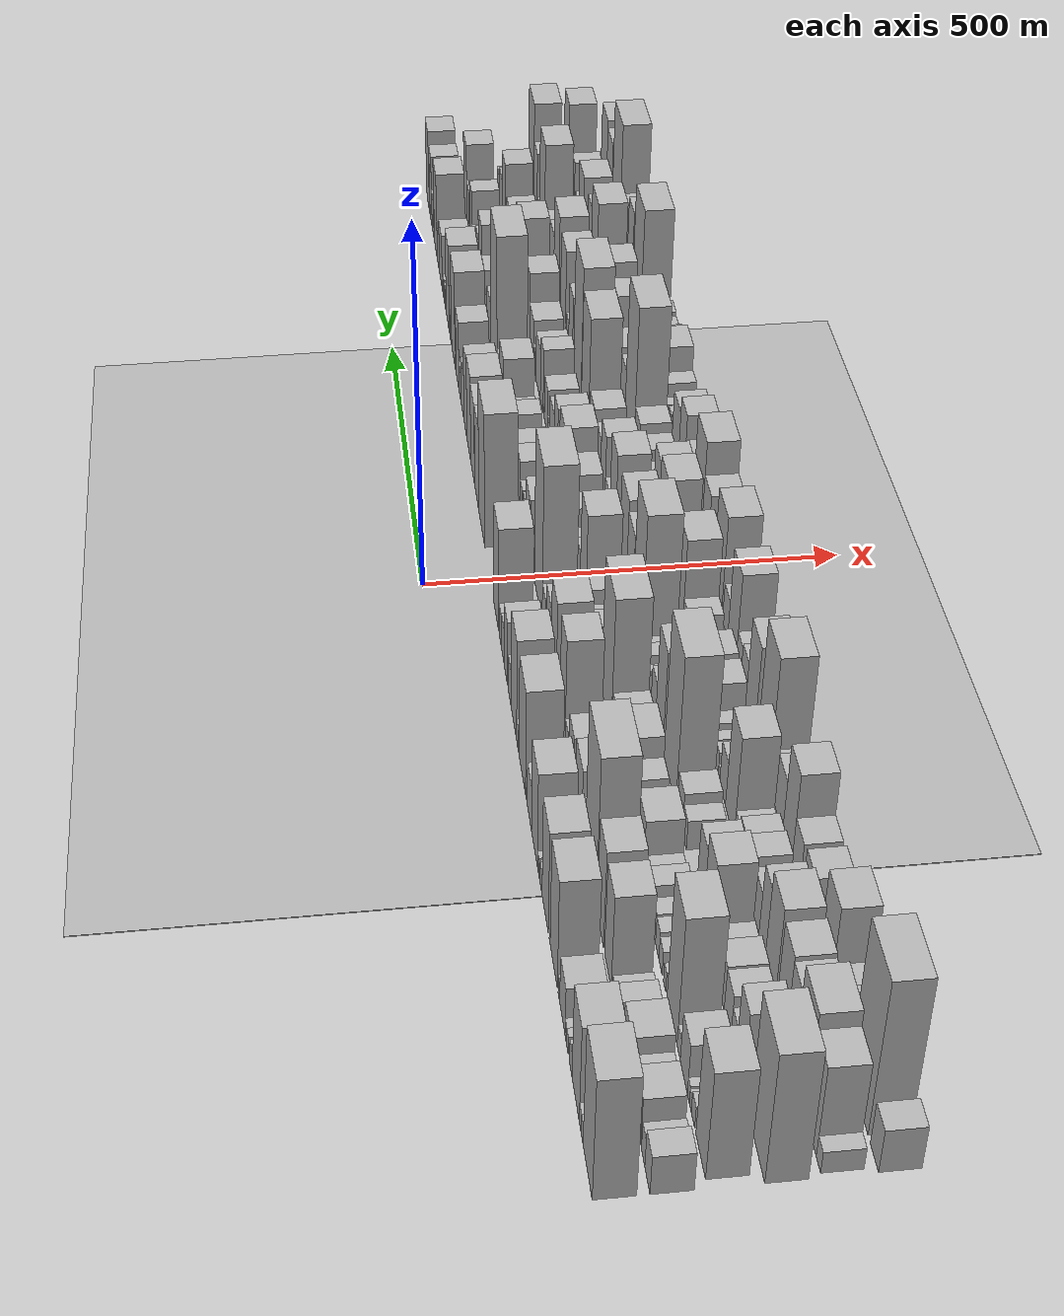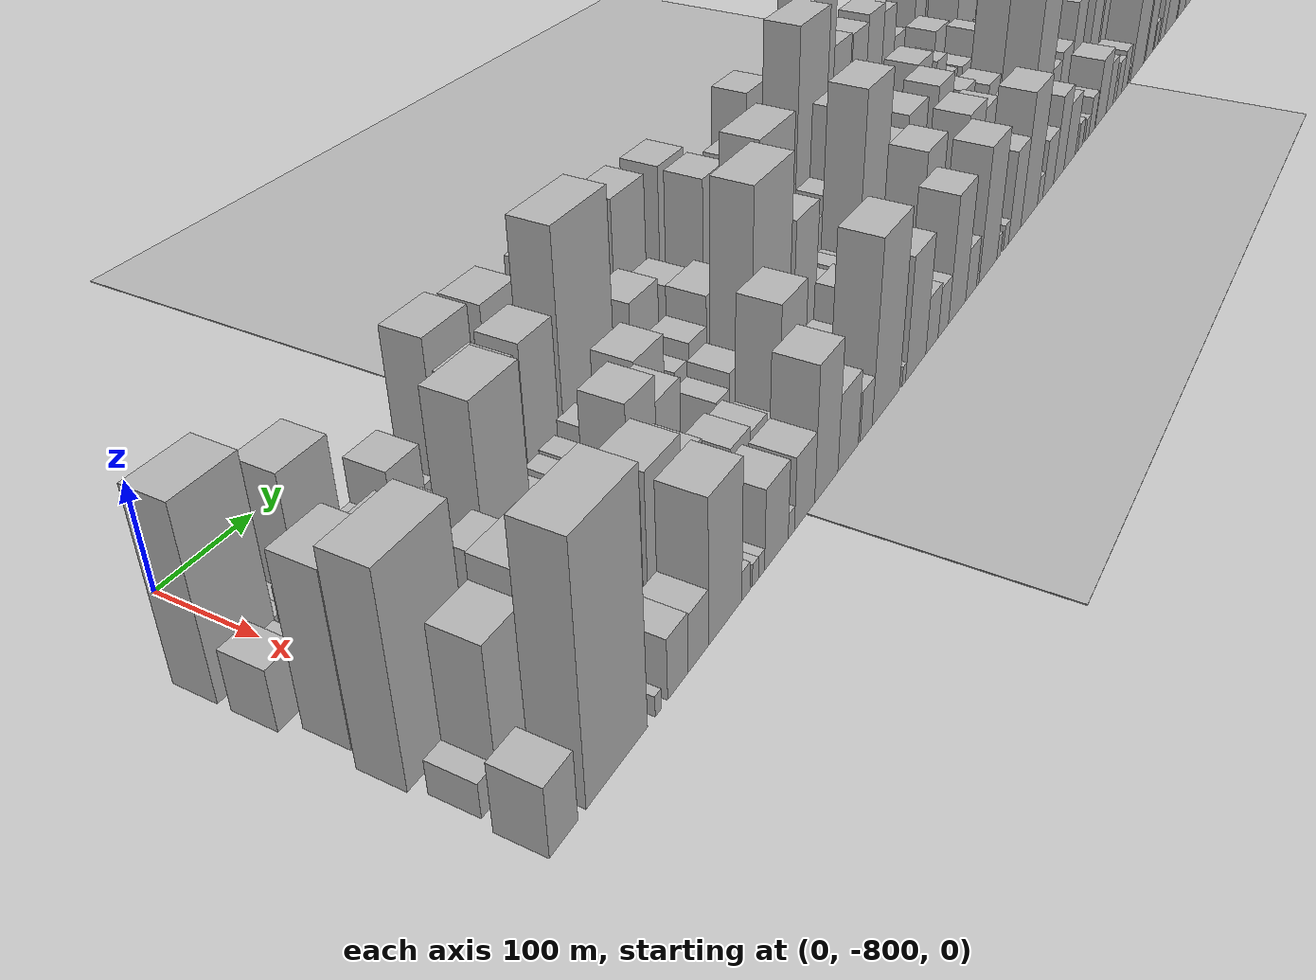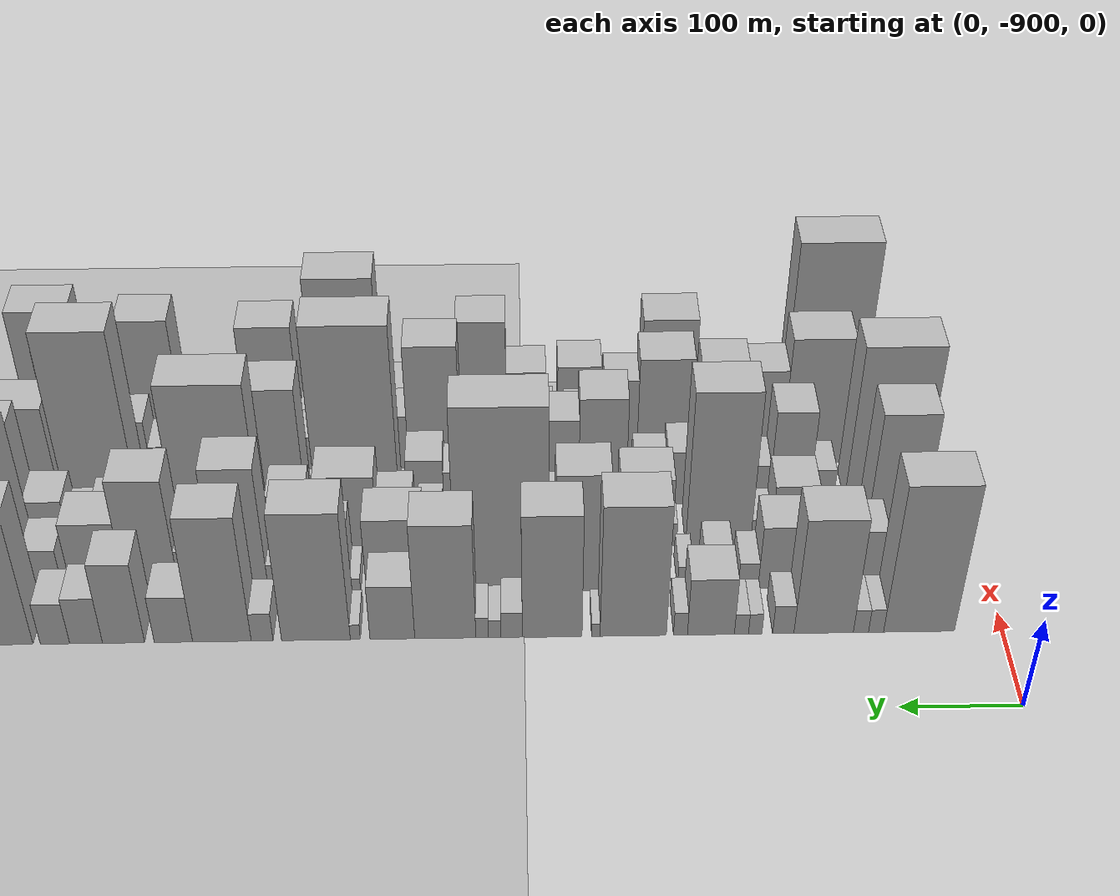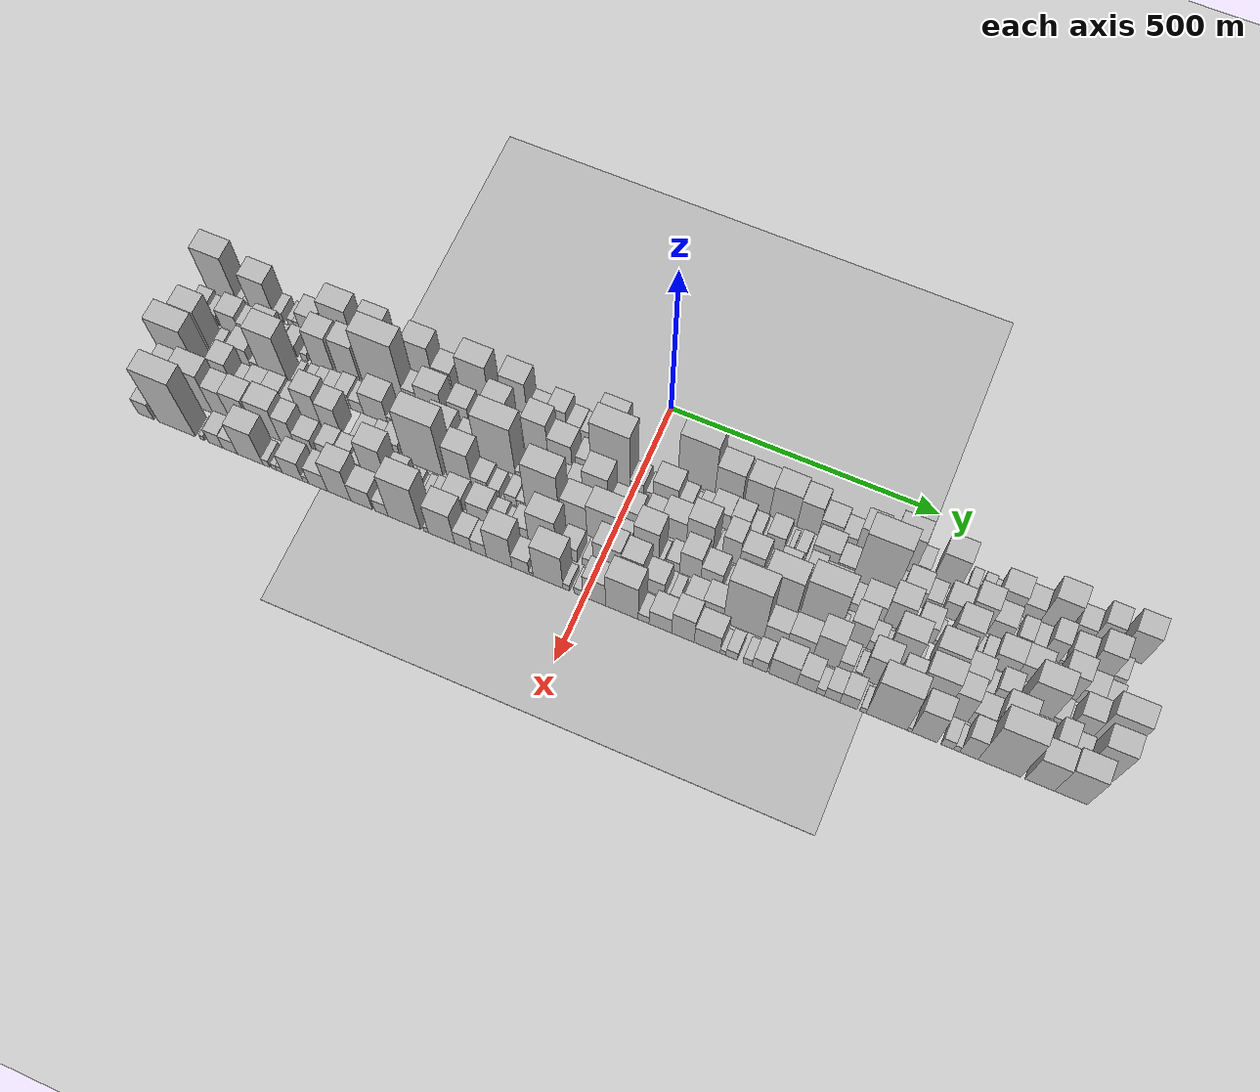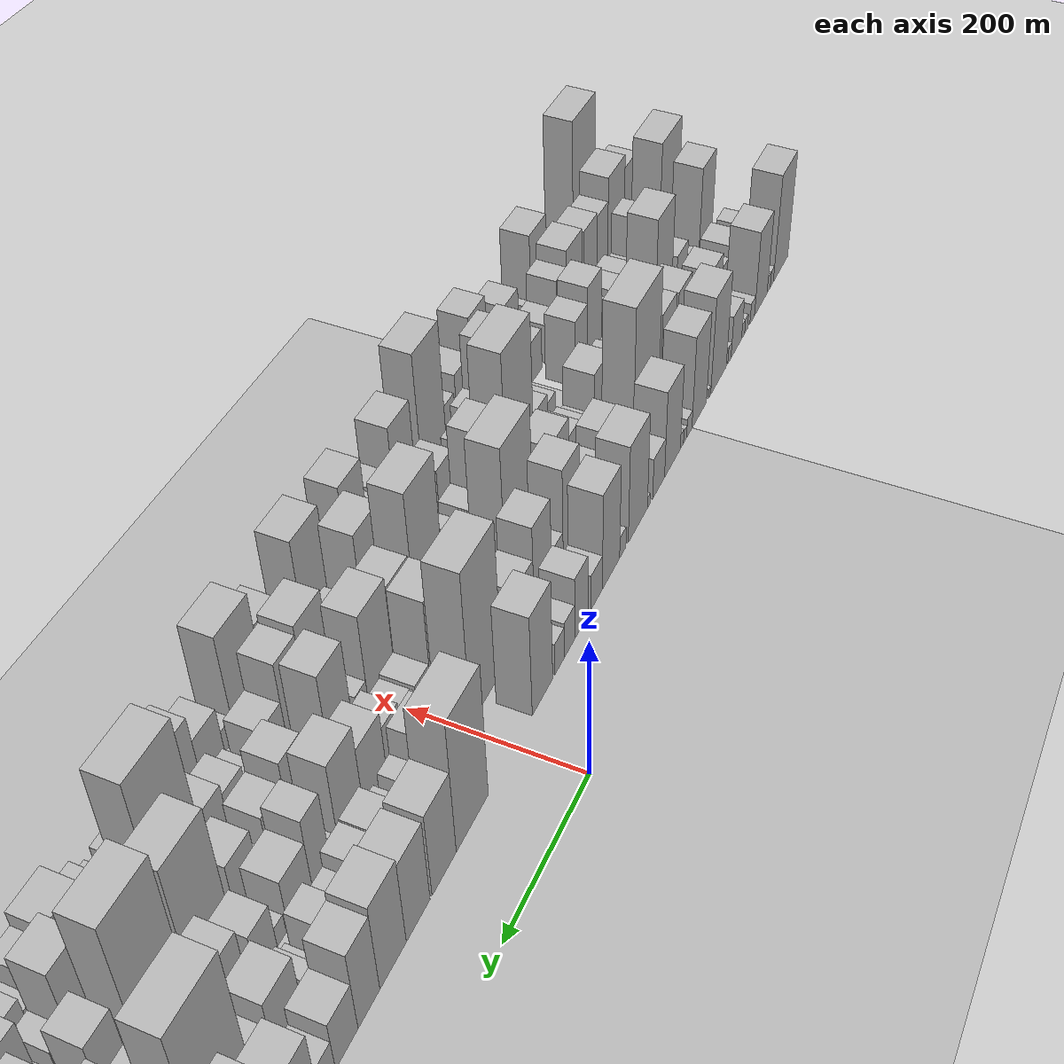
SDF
<?xml version="1.0" encoding="utf-8"?>

<sdf version="1.6">

   <world name="default">

      <gui fullscreen="0">

         <camera name="user_camera">

            <pose>-15 0 4.57585 0 0 0</pose>

            <view_controller>orbit</view_controller>

         </camera>

      </gui>

      <scene>

         <sky>

           <clouds>

             <speed>12</speed>

           </clouds>

         </sky>

         <ambient>0.4 0.4 0.4 1</ambient>

         <background>0.7 0.7 0.7 1</background>

         <shadows>1</shadows>

      </scene>

      <gravity>0 0 -9.8066</gravity>

      <magnetic_field>6e-06 2.3e-05 -4.2e-05</magnetic_field>

      <physics default="0" name="default_physics" type="ode">

         <ode>

            <solver>

               <type>quick</type>

               <iters>10</iters>

               <sor>1.0</sor>

               <use_dynamic_moi_rescaling>0</use_dynamic_moi_rescaling>

            </solver>

            <constraints>

               <cfm>0</cfm>

               <erp>0.2</erp>

               <contact_max_correcting_vel>100</contact_max_correcting_vel>

               <contact_surface_layer>0.001</contact_surface_layer>

            </constraints>

         </ode>

         <max_step_size>0.004</max_step_size>

         <real_time_factor>1</real_time_factor>

         <real_time_update_rate>250</real_time_update_rate>

      </physics>

      <light name="sun" type="directional">

         <cast_shadows>1</cast_shadows>

         <pose>0 0 10 0 0 0</pose>

         <diffuse>0.8 0.8 0.8 1</diffuse>

         <specular>0.2 0.2 0.2 1</specular>

         <attenuation>

            <range>1000</range>

            <constant>0.9</constant>

            <linear>0.01</linear>

            <quadratic>0.001</quadratic>

         </attenuation>

         <direction>-0.5 0.1 -0.9</direction>

      </light>

      <include>

         <name>ground_plane_1</name>

         <uri>model://HANNAS_ground_plane</uri>

         <pose>0 0 0  0 0 0</pose>

      </include>

      <include>

         <name>ground_plane_2</name>

         <uri>model://HANNAS_ground_plane</uri>

         <pose>100 0 0  0 0 0</pose>

      </include>

      <model name="building_1">

         <static>1</static>

         <pose frame="">100.0000 -830.2596 0 0.000000 0.000000 0.000000</pose>

         <link name="link">

            <pose frame="">0 0 84.00 0 0 0</pose>

            <collision name="collision">

               <geometry>

                  <box>

                     <size>40.0000 59.4807 168.0000</size>

                  </box>

               </geometry>

               <max_contacts>10</max_contacts>

               <surface>

                  <contact>

                     <ode/>

                  </contact>

                  <bounce/>

                  <friction>

                     <torsional>

                        <ode/>

                     </torsional>

                     <ode/>

                  </friction>

               </surface>

            </collision>

            <visual name="visual">

               <cast_shadows>0</cast_shadows>

               <geometry>

                  <box>

                     <size>40.0000 59.4807 168.0000</size>

                  </box>

               </geometry>

               <material>

                  <script>

                     <uri>model://HANNAS_wall/materials/scripts</uri>

                     <uri>model://HANNAS_wall/materials/textures</uri>

                     <name>vrc/HANNAS_wall</name>

                  </script>

               </material>

            </visual>

            <self_collide>0</self_collide>

            <enable_wind>0</enable_wind>

            <kinematic>0</kinematic>

         </link>

      </model>

      <model name="building_2">

         <static>1</static>

         <pose frame="">100.0000 -794.2033 0 0.000000 0.000000 0.000000</pose>

         <link name="link">

            <pose frame="">0 0 13.50 0 0 0</pose>

            <collision name="collision">

               <geometry>

                  <box>

                     <size>40.0000 12.6319 27.0000</size>

                  </box>

               </geometry>

               <max_contacts>10</max_contacts>

               <surface>

                  <contact>

                     <ode/>

                  </contact>

                  <bounce/>

                  <friction>

                     <torsional>

                        <ode/>

                     </torsional>

                     <ode/>

                  </friction>

               </surface>

            </collision>

            <visual name="visual">

               <cast_shadows>0</cast_shadows>

               <geometry>

                  <box>

                     <size>40.0000 12.6319 27.0000</size>

                  </box>

               </geometry>

               <material>

                  <script>

                     <uri>model://HANNAS_wall/materials/scripts</uri>

                     <uri>model://HANNAS_wall/materials/textures</uri>

                     <name>vrc/HANNAS_wall</name>

                  </script>

               </material>

            </visual>

            <self_collide>0</self_collide>

            <enable_wind>0</enable_wind>

            <kinematic>0</kinematic>

         </link>

      </model>

      <model name="building_3">

         <static>1</static>

         <pose frame="">100.0000 -781.5189 0 0.000000 0.000000 0.000000</pose>

         <link name="link">

            <pose frame="">0 0 13.50 0 0 0</pose>

            <collision name="collision">

               <geometry>

                  <box>

                     <size>40.0000 12.7370 27.0000</size>

                  </box>

               </geometry>

               <max_contacts>10</max_contacts>

               <surface>

                  <contact>

                     <ode/>

                  </contact>

                  <bounce/>

                  <friction>

                     <torsional>

                        <ode/>

                     </torsional>

                     <ode/>

                  </friction>

               </surface>

            </collision>

            <visual name="visual">

               <cast_shadows>0</cast_shadows>

               <geometry>

                  <box>

                     <size>40.0000 12.7370 27.0000</size>

                  </box>

               </geometry>

               <material>

                  <script>

                     <uri>model://HANNAS_wall/materials/scripts</uri>

                     <uri>model://HANNAS_wall/materials/textures</uri>

                     <name>vrc/HANNAS_wall</name>

                  </script>

               </material>

            </visual>

            <self_collide>0</self_collide>

            <enable_wind>0</enable_wind>

            <kinematic>0</kinematic>

         </link>

      </model>

      <model name="building_4">

         <static>1</static>

         <pose frame="">100.0000 -750.2346 0 0.000000 0.000000 0.000000</pose>

         <link name="link">

            <pose frame="">0 0 66.00 0 0 0</pose>

            <collision name="collision">

               <geometry>

                  <box>

                     <size>40.0000 49.8316 132.0000</size>

                  </box>

               </geometry>

               <max_contacts>10</max_contacts>

               <surface>

                  <contact>

                     <ode/>

                  </contact>

                  <bounce/>

                  <friction>

                     <torsional>

                        <ode/>

                     </torsional>

                     <ode/>

                  </friction>

               </surface>

            </collision>

            <visual name="visual">

               <cast_shadows>0</cast_shadows>

               <geometry>

                  <box>

                     <size>40.0000 49.8316 132.0000</size>

                  </box>

               </geometry>

               <material>

                  <script>

                     <uri>model://HANNAS_wall/materials/scripts</uri>

                     <uri>model://HANNAS_wall/materials/textures</uri>

                     <name>vrc/HANNAS_wall</name>

                  </script>

               </material>

            </visual>

            <self_collide>0</self_collide>

            <enable_wind>0</enable_wind>

            <kinematic>0</kinematic>

         </link>

      </model>

      <model name="building_5">

         <static>1</static>

         <pose frame="">100.0000 -716.4139 0 0.000000 0.000000 0.000000</pose>

         <link name="link">

            <pose frame="">0 0 16.50 0 0 0</pose>

            <collision name="collision">

               <geometry>

                  <box>

                     <size>40.0000 17.8099 33.0000</size>

                  </box>

               </geometry>

               <max_contacts>10</max_contacts>

               <surface>

                  <contact>

                     <ode/>

                  </contact>

                  <bounce/>

                  <friction>

                     <torsional>

                        <ode/>

                     </torsional>

                     <ode/>

                  </friction>

               </surface>

            </collision>

            <visual name="visual">

               <cast_shadows>0</cast_shadows>

               <geometry>

                  <box>

                     <size>40.0000 17.8099 33.0000</size>

                  </box>

               </geometry>

               <material>

                  <script>

                     <uri>model://HANNAS_wall/materials/scripts</uri>

                     <uri>model://HANNAS_wall/materials/textures</uri>

                     <name>vrc/HANNAS_wall</name>

                  </script>

               </material>

            </visual>

            <self_collide>0</self_collide>

            <enable_wind>0</enable_wind>

            <kinematic>0</kinematic>

         </link>

      </model>

      <model name="building_6">

         <static>1</static>

         <pose frame="">100.0000 -692.8799 0 0.000000 0.000000 0.000000</pose>

         <link name="link">

            <pose frame="">0 0 12.00 0 0 0</pose>

            <collision name="collision">

               <geometry>

                  <box>

                     <size>40.0000 11.2581 24.0000</size>

                  </box>

               </geometry>

               <max_contacts>10</max_contacts>

               <surface>

                  <contact>

                     <ode/>

                  </contact>

                  <bounce/>

                  <friction>

                     <torsional>

                        <ode/>

                     </torsional>

                     <ode/>

                  </friction>

               </surface>

            </collision>

            <visual name="visual">

               <cast_shadows>0</cast_shadows>

               <geometry>

                  <box>

                     <size>40.0000 11.2581 24.0000</size>

                  </box>

               </geometry>

               <material>

                  <script>

                     <uri>model://HANNAS_wall/materials/scripts</uri>

                     <uri>model://HANNAS_wall/materials/textures</uri>

                     <name>vrc/HANNAS_wall</name>

                  </script>

               </material>

            </visual>

            <self_collide>0</self_collide>

            <enable_wind>0</enable_wind>

            <kinematic>0</kinematic>

         </link>

      </model>

      <model name="building_7">

         <static>1</static>

         <pose frame="">100.0000 -681.3633 0 0.000000 0.000000 0.000000</pose>

         <link name="link">

            <pose frame="">0 0 12.00 0 0 0</pose>

            <collision name="collision">

               <geometry>

                  <box>

                     <size>40.0000 11.7751 24.0000</size>

                  </box>

               </geometry>

               <max_contacts>10</max_contacts>

               <surface>

                  <contact>

                     <ode/>

                  </contact>

                  <bounce/>

                  <friction>

                     <torsional>

                        <ode/>

                     </torsional>

                     <ode/>

                  </friction>

               </surface>

            </collision>

            <visual name="visual">

               <cast_shadows>0</cast_shadows>

               <geometry>

                  <box>

                     <size>40.0000 11.7751 24.0000</size>

                  </box>

               </geometry>

               <material>

                  <script>

                     <uri>model://HANNAS_wall/materials/scripts</uri>

                     <uri>model://HANNAS_wall/materials/textures</uri>

                     <name>vrc/HANNAS_wall</name>

                  </script>

               </material>

            </visual>

            <self_collide>0</self_collide>

            <enable_wind>0</enable_wind>

            <kinematic>0</kinematic>

         </link>

      </model>

      <model name="building_8">

         <static>1</static>

         <pose frame="">100.0000 -655.8112 0 0.000000 0.000000 0.000000</pose>

         <link name="link">

            <pose frame="">0 0 33.00 0 0 0</pose>

            <collision name="collision">

               <geometry>

                  <box>

                     <size>40.0000 39.3291 66.0000</size>

                  </box>

               </geometry>

               <max_contacts>10</max_contacts>

               <surface>

                  <contact>

                     <ode/>

                  </contact>

                  <bounce/>

                  <friction>

                     <torsional>

                        <ode/>

                     </torsional>

                     <ode/>

                  </friction>

               </surface>

            </collision>

            <visual name="visual">

               <cast_shadows>0</cast_shadows>

               <geometry>

                  <box>

                     <size>40.0000 39.3291 66.0000</size>

                  </box>

               </geometry>

               <material>

                  <script>

                     <uri>model://HANNAS_wall/materials/scripts</uri>

                     <uri>model://HANNAS_wall/materials/textures</uri>

                     <name>vrc/HANNAS_wall</name>

                  </script>

               </material>

            </visual>

            <self_collide>0</self_collide>

            <enable_wind>0</enable_wind>

            <kinematic>0</kinematic>

         </link>

      </model>

      <model name="building_9">

         <static>1</static>

         <pose frame="">100.0000 -630.3494 0 0.000000 0.000000 0.000000</pose>

         <link name="link">

            <pose frame="">0 0 13.50 0 0 0</pose>

            <collision name="collision">

               <geometry>

                  <box>

                     <size>40.0000 11.5944 27.0000</size>

                  </box>

               </geometry>

               <max_contacts>10</max_contacts>

               <surface>

                  <contact>

                     <ode/>

                  </contact>

                  <bounce/>

                  <friction>

                     <torsional>

                        <ode/>

                     </torsional>

                     <ode/>

                  </friction>

               </surface>

            </collision>

            <visual name="visual">

               <cast_shadows>0</cast_shadows>

               <geometry>

                  <box>

                     <size>40.0000 11.5944 27.0000</size>

                  </box>

               </geometry>

               <material>

                  <script>

                     <uri>model://HANNAS_wall/materials/scripts</uri>

                     <uri>model://HANNAS_wall/materials/textures</uri>

                     <name>vrc/HANNAS_wall</name>

                  </script>

               </material>

            </visual>

            <self_collide>0</self_collide>

            <enable_wind>0</enable_wind>

            <kinematic>0</kinematic>

         </link>

      </model>

      <model name="building_10">

         <static>1</static>

         <pose frame="">100.0000 -590.8755 0 0.000000 0.000000 0.000000</pose>

         <link name="link">

            <pose frame="">0 0 75.00 0 0 0</pose>

            <collision name="collision">

               <geometry>

                  <box>

                     <size>40.0000 55.3533 150.0000</size>

                  </box>

               </geometry>

               <max_contacts>10</max_contacts>

               <surface>

                  <contact>

                     <ode/>

                  </contact>

                  <bounce/>

                  <friction>

                     <torsional>

                        <ode/>

                     </torsional>

                     <ode/>

                  </friction>

               </surface>

            </collision>

            <visual name="visual">

               <cast_shadows>0</cast_shadows>

               <geometry>

                  <box>

                     <size>40.0000 55.3533 150.0000</size>

                  </box>

               </geometry>

               <material>

                  <script>

                     <uri>model://HANNAS_wall/materials/scripts</uri>

                     <uri>model://HANNAS_wall/materials/textures</uri>

                     <name>vrc/HANNAS_wall</name>

                  </script>

               </material>

            </visual>

            <self_collide>0</self_collide>

            <enable_wind>0</enable_wind>

            <kinematic>0</kinematic>

         </link>

      </model>

      <model name="building_11">

         <static>1</static>

         <pose frame="">100.0000 -559.6447 0 0.000000 0.000000 0.000000</pose>

         <link name="link">

            <pose frame="">0 0 7.50 0 0 0</pose>

            <collision name="collision">

               <geometry>

                  <box>

                     <size>40.0000 7.1084 15.0000</size>

                  </box>

               </geometry>

               <max_contacts>10</max_contacts>

               <surface>

                  <contact>

                     <ode/>

                  </contact>

                  <bounce/>

                  <friction>

                     <torsional>

                        <ode/>

                     </torsional>

                     <ode/>

                  </friction>

               </surface>

            </collision>

            <visual name="visual">

               <cast_shadows>0</cast_shadows>

               <geometry>

                  <box>

                     <size>40.0000 7.1084 15.0000</size>

                  </box>

               </geometry>

               <material>

                  <script>

                     <uri>model://HANNAS_wall/materials/scripts</uri>

                     <uri>model://HANNAS_wall/materials/textures</uri>

                     <name>vrc/HANNAS_wall</name>

                  </script>

               </material>

            </visual>

            <self_collide>0</self_collide>

            <enable_wind>0</enable_wind>

            <kinematic>0</kinematic>

         </link>

      </model>

      <model name="building_12">

         <static>1</static>

         <pose frame="">100.0000 -523.2259 0 0.000000 0.000000 0.000000</pose>

         <link name="link">

            <pose frame="">0 0 70.50 0 0 0</pose>

            <collision name="collision">

               <geometry>

                  <box>

                     <size>40.0000 49.7294 141.0000</size>

                  </box>

               </geometry>

               <max_contacts>10</max_contacts>

               <surface>

                  <contact>

                     <ode/>

                  </contact>

                  <bounce/>

                  <friction>

                     <torsional>

                        <ode/>

                     </torsional>

                     <ode/>

                  </friction>

               </surface>

            </collision>

            <visual name="visual">

               <cast_shadows>0</cast_shadows>

               <geometry>

                  <box>

                     <size>40.0000 49.7294 141.0000</size>

                  </box>

               </geometry>

               <material>

                  <script>

                     <uri>model://HANNAS_wall/materials/scripts</uri>

                     <uri>model://HANNAS_wall/materials/textures</uri>

                     <name>vrc/HANNAS_wall</name>

                  </script>

               </material>

            </visual>

            <self_collide>0</self_collide>

            <enable_wind>0</enable_wind>

            <kinematic>0</kinematic>

         </link>

      </model>

      <model name="building_13">

         <static>1</static>

         <pose frame="">100.0000 -489.3843 0 0.000000 0.000000 0.000000</pose>

         <link name="link">

            <pose frame="">0 0 15.00 0 0 0</pose>

            <collision name="collision">

               <geometry>

                  <box>

                     <size>40.0000 17.9538 30.0000</size>

                  </box>

               </geometry>

               <max_contacts>10</max_contacts>

               <surface>

                  <contact>

                     <ode/>

                  </contact>

                  <bounce/>

                  <friction>

                     <torsional>

                        <ode/>

                     </torsional>

                     <ode/>

                  </friction>

               </surface>

            </collision>

            <visual name="visual">

               <cast_shadows>0</cast_shadows>

               <geometry>

                  <box>

                     <size>40.0000 17.9538 30.0000</size>

                  </box>

               </geometry>

               <material>

                  <script>

                     <uri>model://HANNAS_wall/materials/scripts</uri>

                     <uri>model://HANNAS_wall/materials/textures</uri>

                     <name>vrc/HANNAS_wall</name>

                  </script>

               </material>

            </visual>

            <self_collide>0</self_collide>

            <enable_wind>0</enable_wind>

            <kinematic>0</kinematic>

         </link>

      </model>

      <model name="building_14">

         <static>1</static>

         <pose frame="">100.0000 -475.2543 0 0.000000 0.000000 0.000000</pose>

         <link name="link">

            <pose frame="">0 0 10.50 0 0 0</pose>

            <collision name="collision">

               <geometry>

                  <box>

                     <size>40.0000 10.3061 21.0000</size>

                  </box>

               </geometry>

               <max_contacts>10</max_contacts>

               <surface>

                  <contact>

                     <ode/>

                  </contact>

                  <bounce/>

                  <friction>

                     <torsional>

                        <ode/>

                     </torsional>

                     <ode/>

                  </friction>

               </surface>

            </collision>

            <visual name="visual">

               <cast_shadows>0</cast_shadows>

               <geometry>

                  <box>

                     <size>40.0000 10.3061 21.0000</size>

                  </box>

               </geometry>

               <material>

                  <script>

                     <uri>model://HANNAS_wall/materials/scripts</uri>

                     <uri>model://HANNAS_wall/materials/textures</uri>

                     <name>vrc/HANNAS_wall</name>

                  </script>

               </material>

            </visual>

            <self_collide>0</self_collide>

            <enable_wind>0</enable_wind>

            <kinematic>0</kinematic>

         </link>

      </model>

      <model name="building_15">

         <static>1</static>

         <pose frame="">100.0000 -464.8104 0 0.000000 0.000000 0.000000</pose>

         <link name="link">

            <pose frame="">0 0 12.00 0 0 0</pose>

            <collision name="collision">

               <geometry>

                  <box>

                     <size>40.0000 10.5816 24.0000</size>

                  </box>

               </geometry>

               <max_contacts>10</max_contacts>

               <surface>

                  <contact>

                     <ode/>

                  </contact>

                  <bounce/>

                  <friction>

                     <torsional>

                        <ode/>

                     </torsional>

                     <ode/>

                  </friction>

               </surface>

            </collision>

            <visual name="visual">

               <cast_shadows>0</cast_shadows>

               <geometry>

                  <box>

                     <size>40.0000 10.5816 24.0000</size>

                  </box>

               </geometry>

               <material>

                  <script>

                     <uri>model://HANNAS_wall/materials/scripts</uri>

                     <uri>model://HANNAS_wall/materials/textures</uri>

                     <name>vrc/HANNAS_wall</name>

                  </script>

               </material>

            </visual>

            <self_collide>0</self_collide>

            <enable_wind>0</enable_wind>

            <kinematic>0</kinematic>

         </link>

      </model>

      <model name="building_16">

         <static>1</static>

         <pose frame="">100.0000 -434.1045 0 0.000000 0.000000 0.000000</pose>

         <link name="link">

            <pose frame="">0 0 66.00 0 0 0</pose>

            <collision name="collision">

               <geometry>

                  <box>

                     <size>40.0000 50.8302 132.0000</size>

                  </box>

               </geometry>

               <max_contacts>10</max_contacts>

               <surface>

                  <contact>

                     <ode/>

                  </contact>

                  <bounce/>

                  <friction>

                     <torsional>

                        <ode/>

                     </torsional>

                     <ode/>

                  </friction>

               </surface>

            </collision>

            <visual name="visual">

               <cast_shadows>0</cast_shadows>

               <geometry>

                  <box>

                     <size>40.0000 50.8302 132.0000</size>

                  </box>

               </geometry>

               <material>

                  <script>

                     <uri>model://HANNAS_wall/materials/scripts</uri>

                     <uri>model://HANNAS_wall/materials/textures</uri>

                     <name>vrc/HANNAS_wall</name>

                  </script>

               </material>

            </visual>

            <self_collide>0</self_collide>

            <enable_wind>0</enable_wind>

            <kinematic>0</kinematic>

         </link>

      </model>

      <model name="building_17">

         <static>1</static>

         <pose frame="">100.0000 -390.0490 0 0.000000 0.000000 0.000000</pose>

         <link name="link">

            <pose frame="">0 0 31.50 0 0 0</pose>

            <collision name="collision">

               <geometry>

                  <box>

                     <size>40.0000 37.2809 63.0000</size>

                  </box>

               </geometry>

               <max_contacts>10</max_contacts>

               <surface>

                  <contact>

                     <ode/>

                  </contact>

                  <bounce/>

                  <friction>

                     <torsional>

                        <ode/>

                     </torsional>

                     <ode/>

                  </friction>

               </surface>

            </collision>

            <visual name="visual">

               <cast_shadows>0</cast_shadows>

               <geometry>

                  <box>

                     <size>40.0000 37.2809 63.0000</size>

                  </box>

               </geometry>

               <material>

                  <script>

                     <uri>model://HANNAS_wall/materials/scripts</uri>

                     <uri>model://HANNAS_wall/materials/textures</uri>

                     <name>vrc/HANNAS_wall</name>

                  </script>

               </material>

            </visual>

            <self_collide>0</self_collide>

            <enable_wind>0</enable_wind>

            <kinematic>0</kinematic>

         </link>

      </model>

      <model name="building_18">

         <static>1</static>

         <pose frame="">100.0000 -359.2565 0 0.000000 0.000000 0.000000</pose>

         <link name="link">

            <pose frame="">0 0 9.00 0 0 0</pose>

            <collision name="collision">

               <geometry>

                  <box>

                     <size>40.0000 8.3040 18.0000</size>

                  </box>

               </geometry>

               <max_contacts>10</max_contacts>

               <surface>

                  <contact>

                     <ode/>

                  </contact>

                  <bounce/>

                  <friction>

                     <torsional>

                        <ode/>

                     </torsional>

                     <ode/>

                  </friction>

               </surface>

            </collision>

            <visual name="visual">

               <cast_shadows>0</cast_shadows>

               <geometry>

                  <box>

                     <size>40.0000 8.3040 18.0000</size>

                  </box>

               </geometry>

               <material>

                  <script>

                     <uri>model://HANNAS_wall/materials/scripts</uri>

                     <uri>model://HANNAS_wall/materials/textures</uri>

                     <name>vrc/HANNAS_wall</name>

                  </script>

               </material>

            </visual>

            <self_collide>0</self_collide>

            <enable_wind>0</enable_wind>

            <kinematic>0</kinematic>

         </link>

      </model>

      <model name="building_19">

         <static>1</static>

         <pose frame="">100.0000 -326.4940 0 0.000000 0.000000 0.000000</pose>

         <link name="link">

            <pose frame="">0 0 73.50 0 0 0</pose>

            <collision name="collision">

               <geometry>

                  <box>

                     <size>40.0000 57.2211 147.0000</size>

                  </box>

               </geometry>

               <max_contacts>10</max_contacts>

               <surface>

                  <contact>

                     <ode/>

                  </contact>

                  <bounce/>

                  <friction>

                     <torsional>

                        <ode/>

                     </torsional>

                     <ode/>

                  </friction>

               </surface>

            </collision>

            <visual name="visual">

               <cast_shadows>0</cast_shadows>

               <geometry>

                  <box>

                     <size>40.0000 57.2211 147.0000</size>

                  </box>

               </geometry>

               <material>

                  <script>

                     <uri>model://HANNAS_wall/materials/scripts</uri>

                     <uri>model://HANNAS_wall/materials/textures</uri>

                     <name>vrc/HANNAS_wall</name>

                  </script>

               </material>

            </visual>

            <self_collide>0</self_collide>

            <enable_wind>0</enable_wind>

            <kinematic>0</kinematic>

         </link>

      </model>

      <model name="building_20">

         <static>1</static>

         <pose frame="">100.0000 -281.8136 0 0.000000 0.000000 0.000000</pose>

         <link name="link">

            <pose frame="">0 0 16.50 0 0 0</pose>

            <collision name="collision">

               <geometry>

                  <box>

                     <size>40.0000 18.1396 33.0000</size>

                  </box>

               </geometry>

               <max_contacts>10</max_contacts>

               <surface>

                  <contact>

                     <ode/>

                  </contact>

                  <bounce/>

                  <friction>

                     <torsional>

                        <ode/>

                     </torsional>

                     <ode/>

                  </friction>

               </surface>

            </collision>

            <visual name="visual">

               <cast_shadows>0</cast_shadows>

               <geometry>

                  <box>

                     <size>40.0000 18.1396 33.0000</size>

                  </box>

               </geometry>

               <material>

                  <script>

                     <uri>model://HANNAS_wall/materials/scripts</uri>

                     <uri>model://HANNAS_wall/materials/textures</uri>

                     <name>vrc/HANNAS_wall</name>

                  </script>

               </material>

            </visual>

            <self_collide>0</self_collide>

            <enable_wind>0</enable_wind>

            <kinematic>0</kinematic>

         </link>

      </model>

      <model name="building_21">

         <static>1</static>

         <pose frame="">100.0000 -248.3978 0 0.000000 0.000000 0.000000</pose>

         <link name="link">

            <pose frame="">0 0 72.00 0 0 0</pose>

            <collision name="collision">

               <geometry>

                  <box>

                     <size>40.0000 48.6920 144.0000</size>

                  </box>

               </geometry>

               <max_contacts>10</max_contacts>

               <surface>

                  <contact>

                     <ode/>

                  </contact>

                  <bounce/>

                  <friction>

                     <torsional>

                        <ode/>

                     </torsional>

                     <ode/>

                  </friction>

               </surface>

            </collision>

            <visual name="visual">

               <cast_shadows>0</cast_shadows>

               <geometry>

                  <box>

                     <size>40.0000 48.6920 144.0000</size>

                  </box>

               </geometry>

               <material>

                  <script>

                     <uri>model://HANNAS_wall/materials/scripts</uri>

                     <uri>model://HANNAS_wall/materials/textures</uri>

                     <name>vrc/HANNAS_wall</name>

                  </script>

               </material>

            </visual>

            <self_collide>0</self_collide>

            <enable_wind>0</enable_wind>

            <kinematic>0</kinematic>

         </link>

      </model>

      <model name="building_22">

         <static>1</static>

         <pose frame="">100.0000 -208.1583 0 0.000000 0.000000 0.000000</pose>

         <link name="link">

            <pose frame="">0 0 27.00 0 0 0</pose>

            <collision name="collision">

               <geometry>

                  <box>

                     <size>40.0000 31.7872 54.0000</size>

                  </box>

               </geometry>

               <max_contacts>10</max_contacts>

               <surface>

                  <contact>

                     <ode/>

                  </contact>

                  <bounce/>

                  <friction>

                     <torsional>

                        <ode/>

                     </torsional>

                     <ode/>

                  </friction>

               </surface>

            </collision>

            <visual name="visual">

               <cast_shadows>0</cast_shadows>

               <geometry>

                  <box>

                     <size>40.0000 31.7872 54.0000</size>

                  </box>

               </geometry>

               <material>

                  <script>

                     <uri>model://HANNAS_wall/materials/scripts</uri>

                     <uri>model://HANNAS_wall/materials/textures</uri>

                     <name>vrc/HANNAS_wall</name>

                  </script>

               </material>

            </visual>

            <self_collide>0</self_collide>

            <enable_wind>0</enable_wind>

            <kinematic>0</kinematic>

         </link>

      </model>

      <model name="building_23">

         <static>1</static>

         <pose frame="">100.0000 -166.8493 0 0.000000 0.000000 0.000000</pose>

         <link name="link">

            <pose frame="">0 0 46.50 0 0 0</pose>

            <collision name="collision">

               <geometry>

                  <box>

                     <size>40.0000 34.8307 93.0000</size>

                  </box>

               </geometry>

               <max_contacts>10</max_contacts>

               <surface>

                  <contact>

                     <ode/>

                  </contact>

                  <bounce/>

                  <friction>

                     <torsional>

                        <ode/>

                     </torsional>

                     <ode/>

                  </friction>

               </surface>

            </collision>

            <visual name="visual">

               <cast_shadows>0</cast_shadows>

               <geometry>

                  <box>

                     <size>40.0000 34.8307 93.0000</size>

                  </box>

               </geometry>

               <material>

                  <script>

                     <uri>model://HANNAS_wall/materials/scripts</uri>

                     <uri>model://HANNAS_wall/materials/textures</uri>

                     <name>vrc/HANNAS_wall</name>

                  </script>

               </material>

            </visual>

            <self_collide>0</self_collide>

            <enable_wind>0</enable_wind>

            <kinematic>0</kinematic>

         </link>

      </model>

      <model name="building_24">

         <static>1</static>

         <pose frame="">100.0000 -135.8265 0 0.000000 0.000000 0.000000</pose>

         <link name="link">

            <pose frame="">0 0 27.00 0 0 0</pose>

            <collision name="collision">

               <geometry>

                  <box>

                     <size>40.0000 27.2150 54.0000</size>

                  </box>

               </geometry>

               <max_contacts>10</max_contacts>

               <surface>

                  <contact>

                     <ode/>

                  </contact>

                  <bounce/>

                  <friction>

                     <torsional>

                        <ode/>

                     </torsional>

                     <ode/>

                  </friction>

               </surface>

            </collision>

            <visual name="visual">

               <cast_shadows>0</cast_shadows>

               <geometry>

                  <box>

                     <size>40.0000 27.2150 54.0000</size>

                  </box>

               </geometry>

               <material>

                  <script>

                     <uri>model://HANNAS_wall/materials/scripts</uri>

                     <uri>model://HANNAS_wall/materials/textures</uri>

                     <name>vrc/HANNAS_wall</name>

                  </script>

               </material>

            </visual>

            <self_collide>0</self_collide>

            <enable_wind>0</enable_wind>

            <kinematic>0</kinematic>

         </link>

      </model>

      <model name="building_25">

         <static>1</static>

         <pose frame="">100.0000 -110.0625 0 0.000000 0.000000 0.000000</pose>

         <link name="link">

            <pose frame="">0 0 24.00 0 0 0</pose>

            <collision name="collision">

               <geometry>

                  <box>

                     <size>40.0000 24.3129 48.0000</size>

                  </box>

               </geometry>

               <max_contacts>10</max_contacts>

               <surface>

                  <contact>

                     <ode/>

                  </contact>

                  <bounce/>

                  <friction>

                     <torsional>

                        <ode/>

                     </torsional>

                     <ode/>

                  </friction>

               </surface>

            </collision>

            <visual name="visual">

               <cast_shadows>0</cast_shadows>

               <geometry>

                  <box>

                     <size>40.0000 24.3129 48.0000</size>

                  </box>

               </geometry>

               <material>

                  <script>

                     <uri>model://HANNAS_wall/materials/scripts</uri>

                     <uri>model://HANNAS_wall/materials/textures</uri>

                     <name>vrc/HANNAS_wall</name>

                  </script>

               </material>

            </visual>

            <self_collide>0</self_collide>

            <enable_wind>0</enable_wind>

            <kinematic>0</kinematic>

         </link>

      </model>

      <model name="building_26">

         <static>1</static>

         <pose frame="">100.0000 -66.6376 0 0.000000 0.000000 0.000000</pose>

         <link name="link">

            <pose frame="">0 0 75.00 0 0 0</pose>

            <collision name="collision">

               <geometry>

                  <box>

                     <size>40.0000 50.5369 150.0000</size>

                  </box>

               </geometry>

               <max_contacts>10</max_contacts>

               <surface>

                  <contact>

                     <ode/>

                  </contact>

                  <bounce/>

                  <friction>

                     <torsional>

                        <ode/>

                     </torsional>

                     <ode/>

                  </friction>

               </surface>

            </collision>

            <visual name="visual">

               <cast_shadows>0</cast_shadows>

               <geometry>

                  <box>

                     <size>40.0000 50.5369 150.0000</size>

                  </box>

               </geometry>

               <material>

                  <script>

                     <uri>model://HANNAS_wall/materials/scripts</uri>

                     <uri>model://HANNAS_wall/materials/textures</uri>

                     <name>vrc/HANNAS_wall</name>

                  </script>

               </material>

            </visual>

            <self_collide>0</self_collide>

            <enable_wind>0</enable_wind>

            <kinematic>0</kinematic>

         </link>

      </model>

      <model name="building_27">

         <static>1</static>

         <pose frame="">100.0000 95.9631 0 0.000000 0.000000 0.000000</pose>

         <link name="link">

            <pose frame="">0 0 99.00 0 0 0</pose>

            <collision name="collision">

               <geometry>

                  <box>

                     <size>40.0000 69.5549 198.0000</size>

                  </box>

               </geometry>

               <max_contacts>10</max_contacts>

               <surface>

                  <contact>

                     <ode/>

                  </contact>

                  <bounce/>

                  <friction>

                     <torsional>

                        <ode/>

                     </torsional>

                     <ode/>

                  </friction>

               </surface>

            </collision>

            <visual name="visual">

               <cast_shadows>0</cast_shadows>

               <geometry>

                  <box>

                     <size>40.0000 69.5549 198.0000</size>

                  </box>

               </geometry>

               <material>

                  <script>

                     <uri>model://HANNAS_wall/materials/scripts</uri>

                     <uri>model://HANNAS_wall/materials/textures</uri>

                     <name>vrc/HANNAS_wall</name>

                  </script>

               </material>

            </visual>

            <self_collide>0</self_collide>

            <enable_wind>0</enable_wind>

            <kinematic>0</kinematic>

         </link>

      </model>

      <model name="building_28">

         <static>1</static>

         <pose frame="">100.0000 155.8747 0 0.000000 0.000000 0.000000</pose>

         <link name="link">

            <pose frame="">0 0 63.00 0 0 0</pose>

            <collision name="collision">

               <geometry>

                  <box>

                     <size>40.0000 50.2684 126.0000</size>

                  </box>

               </geometry>

               <max_contacts>10</max_contacts>

               <surface>

                  <contact>

                     <ode/>

                  </contact>

                  <bounce/>

                  <friction>

                     <torsional>

                        <ode/>

                     </torsional>

                     <ode/>

                  </friction>

               </surface>

            </collision>

            <visual name="visual">

               <cast_shadows>0</cast_shadows>

               <geometry>

                  <box>

                     <size>40.0000 50.2684 126.0000</size>

                  </box>

               </geometry>

               <material>

                  <script>

                     <uri>model://HANNAS_wall/materials/scripts</uri>

                     <uri>model://HANNAS_wall/materials/textures</uri>

                     <name>vrc/HANNAS_wall</name>

                  </script>

               </material>

            </visual>

            <self_collide>0</self_collide>

            <enable_wind>0</enable_wind>

            <kinematic>0</kinematic>

         </link>

      </model>

      <model name="building_29">

         <static>1</static>

         <pose frame="">100.0000 208.4547 0 0.000000 0.000000 0.000000</pose>

         <link name="link">

            <pose frame="">0 0 61.50 0 0 0</pose>

            <collision name="collision">

               <geometry>

                  <box>

                     <size>40.0000 46.8915 123.0000</size>

                  </box>

               </geometry>

               <max_contacts>10</max_contacts>

               <surface>

                  <contact>

                     <ode/>

                  </contact>

                  <bounce/>

                  <friction>

                     <torsional>

                        <ode/>

                     </torsional>

                     <ode/>

                  </friction>

               </surface>

            </collision>

            <visual name="visual">

               <cast_shadows>0</cast_shadows>

               <geometry>

                  <box>

                     <size>40.0000 46.8915 123.0000</size>

                  </box>

               </geometry>

               <material>

                  <script>

                     <uri>model://HANNAS_wall/materials/scripts</uri>

                     <uri>model://HANNAS_wall/materials/textures</uri>

                     <name>vrc/HANNAS_wall</name>

                  </script>

               </material>

            </visual>

            <self_collide>0</self_collide>

            <enable_wind>0</enable_wind>

            <kinematic>0</kinematic>

         </link>

      </model>

      <model name="building_30">

         <static>1</static>

         <pose frame="">100.0000 256.9549 0 0.000000 0.000000 0.000000</pose>

         <link name="link">

            <pose frame="">0 0 66.00 0 0 0</pose>

            <collision name="collision">

               <geometry>

                  <box>

                     <size>40.0000 50.1088 132.0000</size>

                  </box>

               </geometry>

               <max_contacts>10</max_contacts>

               <surface>

                  <contact>

                     <ode/>

                  </contact>

                  <bounce/>

                  <friction>

                     <torsional>

                        <ode/>

                     </torsional>

                     <ode/>

                  </friction>

               </surface>

            </collision>

            <visual name="visual">

               <cast_shadows>0</cast_shadows>

               <geometry>

                  <box>

                     <size>40.0000 50.1088 132.0000</size>

                  </box>

               </geometry>

               <material>

                  <script>

                     <uri>model://HANNAS_wall/materials/scripts</uri>

                     <uri>model://HANNAS_wall/materials/textures</uri>

                     <name>vrc/HANNAS_wall</name>

                  </script>

               </material>

            </visual>

            <self_collide>0</self_collide>

            <enable_wind>0</enable_wind>

            <kinematic>0</kinematic>

         </link>

      </model>

      <model name="building_31">

         <static>1</static>

         <pose frame="">100.0000 301.8490 0 0.000000 0.000000 0.000000</pose>

         <link name="link">

            <pose frame="">0 0 60.00 0 0 0</pose>

            <collision name="collision">

               <geometry>

                  <box>

                     <size>40.0000 39.6795 120.0000</size>

                  </box>

               </geometry>

               <max_contacts>10</max_contacts>

               <surface>

                  <contact>

                     <ode/>

                  </contact>

                  <bounce/>

                  <friction>

                     <torsional>

                        <ode/>

                     </torsional>

                     <ode/>

                  </friction>

               </surface>

            </collision>

            <visual name="visual">

               <cast_shadows>0</cast_shadows>

               <geometry>

                  <box>

                     <size>40.0000 39.6795 120.0000</size>

                  </box>

               </geometry>

               <material>

                  <script>

                     <uri>model://HANNAS_wall/materials/scripts</uri>

                     <uri>model://HANNAS_wall/materials/textures</uri>

                     <name>vrc/HANNAS_wall</name>

                  </script>

               </material>

            </visual>

            <self_collide>0</self_collide>

            <enable_wind>0</enable_wind>

            <kinematic>0</kinematic>

         </link>

      </model>

      <model name="building_32">

         <static>1</static>

         <pose frame="">100.0000 341.5199 0 0.000000 0.000000 0.000000</pose>

         <link name="link">

            <pose frame="">0 0 37.50 0 0 0</pose>

            <collision name="collision">

               <geometry>

                  <box>

                     <size>40.0000 39.6623 75.0000</size>

                  </box>

               </geometry>

               <max_contacts>10</max_contacts>

               <surface>

                  <contact>

                     <ode/>

                  </contact>

                  <bounce/>

                  <friction>

                     <torsional>

                        <ode/>

                     </torsional>

                     <ode/>

                  </friction>

               </surface>

            </collision>

            <visual name="visual">

               <cast_shadows>0</cast_shadows>

               <geometry>

                  <box>

                     <size>40.0000 39.6623 75.0000</size>

                  </box>

               </geometry>

               <material>

                  <script>

                     <uri>model://HANNAS_wall/materials/scripts</uri>

                     <uri>model://HANNAS_wall/materials/textures</uri>

                     <name>vrc/HANNAS_wall</name>

                  </script>

               </material>

            </visual>

            <self_collide>0</self_collide>

            <enable_wind>0</enable_wind>

            <kinematic>0</kinematic>

         </link>

      </model>

      <model name="building_33">

         <static>1</static>

         <pose frame="">100.0000 375.2627 0 0.000000 0.000000 0.000000</pose>

         <link name="link">

            <pose frame="">0 0 24.00 0 0 0</pose>

            <collision name="collision">

               <geometry>

                  <box>

                     <size>40.0000 27.8233 48.0000</size>

                  </box>

               </geometry>

               <max_contacts>10</max_contacts>

               <surface>

                  <contact>

                     <ode/>

                  </contact>

                  <bounce/>

                  <friction>

                     <torsional>

                        <ode/>

                     </torsional>

                     <ode/>

                  </friction>

               </surface>

            </collision>

            <visual name="visual">

               <cast_shadows>0</cast_shadows>

               <geometry>

                  <box>

                     <size>40.0000 27.8233 48.0000</size>

                  </box>

               </geometry>

               <material>

                  <script>

                     <uri>model://HANNAS_wall/materials/scripts</uri>

                     <uri>model://HANNAS_wall/materials/textures</uri>

                     <name>vrc/HANNAS_wall</name>

                  </script>

               </material>

            </visual>

            <self_collide>0</self_collide>

            <enable_wind>0</enable_wind>

            <kinematic>0</kinematic>

         </link>

      </model>

      <model name="building_34">

         <static>1</static>

         <pose frame="">100.0000 409.2734 0 0.000000 0.000000 0.000000</pose>

         <link name="link">

            <pose frame="">0 0 54.00 0 0 0</pose>

            <collision name="collision">

               <geometry>

                  <box>

                     <size>40.0000 40.1979 108.0000</size>

                  </box>

               </geometry>

               <max_contacts>10</max_contacts>

               <surface>

                  <contact>

                     <ode/>

                  </contact>

                  <bounce/>

                  <friction>

                     <torsional>

                        <ode/>

                     </torsional>

                     <ode/>

                  </friction>

               </surface>

            </collision>

            <visual name="visual">

               <cast_shadows>0</cast_shadows>

               <geometry>

                  <box>

                     <size>40.0000 40.1979 108.0000</size>

                  </box>

               </geometry>

               <material>

                  <script>

                     <uri>model://HANNAS_wall/materials/scripts</uri>

                     <uri>model://HANNAS_wall/materials/textures</uri>

                     <name>vrc/HANNAS_wall</name>

                  </script>

               </material>

            </visual>

            <self_collide>0</self_collide>

            <enable_wind>0</enable_wind>

            <kinematic>0</kinematic>

         </link>

      </model>

      <model name="building_35">

         <static>1</static>

         <pose frame="">100.0000 438.1028 0 0.000000 0.000000 0.000000</pose>

         <link name="link">

            <pose frame="">0 0 13.50 0 0 0</pose>

            <collision name="collision">

               <geometry>

                  <box>

                     <size>40.0000 11.4611 27.0000</size>

                  </box>

               </geometry>

               <max_contacts>10</max_contacts>

               <surface>

                  <contact>

                     <ode/>

                  </contact>

                  <bounce/>

                  <friction>

                     <torsional>

                        <ode/>

                     </torsional>

                     <ode/>

                  </friction>

               </surface>

            </collision>

            <visual name="visual">

               <cast_shadows>0</cast_shadows>

               <geometry>

                  <box>

                     <size>40.0000 11.4611 27.0000</size>

                  </box>

               </geometry>

               <material>

                  <script>

                     <uri>model://HANNAS_wall/materials/scripts</uri>

                     <uri>model://HANNAS_wall/materials/textures</uri>

                     <name>vrc/HANNAS_wall</name>

                  </script>

               </material>

            </visual>

            <self_collide>0</self_collide>

            <enable_wind>0</enable_wind>

            <kinematic>0</kinematic>

         </link>

      </model>

      <model name="building_36">

         <static>1</static>

         <pose frame="">100.0000 470.0060 0 0.000000 0.000000 0.000000</pose>

         <link name="link">

            <pose frame="">0 0 75.00 0 0 0</pose>

            <collision name="collision">

               <geometry>

                  <box>

                     <size>40.0000 52.3452 150.0000</size>

                  </box>

               </geometry>

               <max_contacts>10</max_contacts>

               <surface>

                  <contact>

                     <ode/>

                  </contact>

                  <bounce/>

                  <friction>

                     <torsional>

                        <ode/>

                     </torsional>

                     <ode/>

                  </friction>

               </surface>

            </collision>

            <visual name="visual">

               <cast_shadows>0</cast_shadows>

               <geometry>

                  <box>

                     <size>40.0000 52.3452 150.0000</size>

                  </box>

               </geometry>

               <material>

                  <script>

                     <uri>model://HANNAS_wall/materials/scripts</uri>

                     <uri>model://HANNAS_wall/materials/textures</uri>

                     <name>vrc/HANNAS_wall</name>

                  </script>

               </material>

            </visual>

            <self_collide>0</self_collide>

            <enable_wind>0</enable_wind>

            <kinematic>0</kinematic>

         </link>

      </model>

      <model name="building_37">

         <static>1</static>

         <pose frame="">100.0000 507.8916 0 0.000000 0.000000 0.000000</pose>

         <link name="link">

            <pose frame="">0 0 22.50 0 0 0</pose>

            <collision name="collision">

               <geometry>

                  <box>

                     <size>40.0000 23.4261 45.0000</size>

                  </box>

               </geometry>

               <max_contacts>10</max_contacts>

               <surface>

                  <contact>

                     <ode/>

                  </contact>

                  <bounce/>

                  <friction>

                     <torsional>

                        <ode/>

                     </torsional>

                     <ode/>

                  </friction>

               </surface>

            </collision>

            <visual name="visual">

               <cast_shadows>0</cast_shadows>

               <geometry>

                  <box>

                     <size>40.0000 23.4261 45.0000</size>

                  </box>

               </geometry>

               <material>

                  <script>

                     <uri>model://HANNAS_wall/materials/scripts</uri>

                     <uri>model://HANNAS_wall/materials/textures</uri>

                     <name>vrc/HANNAS_wall</name>

                  </script>

               </material>

            </visual>

            <self_collide>0</self_collide>

            <enable_wind>0</enable_wind>

            <kinematic>0</kinematic>

         </link>

      </model>

      <model name="building_38">

         <static>1</static>

         <pose frame="">100.0000 552.1882 0 0.000000 0.000000 0.000000</pose>

         <link name="link">

            <pose frame="">0 0 69.00 0 0 0</pose>

            <collision name="collision">

               <geometry>

                  <box>

                     <size>40.0000 47.1673 138.0000</size>

                  </box>

               </geometry>

               <max_contacts>10</max_contacts>

               <surface>

                  <contact>

                     <ode/>

                  </contact>

                  <bounce/>

                  <friction>

                     <torsional>

                        <ode/>

                     </torsional>

                     <ode/>

                  </friction>

               </surface>

            </collision>

            <visual name="visual">

               <cast_shadows>0</cast_shadows>

               <geometry>

                  <box>

                     <size>40.0000 47.1673 138.0000</size>

                  </box>

               </geometry>

               <material>

                  <script>

                     <uri>model://HANNAS_wall/materials/scripts</uri>

                     <uri>model://HANNAS_wall/materials/textures</uri>

                     <name>vrc/HANNAS_wall</name>

                  </script>

               </material>

            </visual>

            <self_collide>0</self_collide>

            <enable_wind>0</enable_wind>

            <kinematic>0</kinematic>

         </link>

      </model>

      <model name="building_39">

         <static>1</static>

         <pose frame="">100.0000 594.6555 0 0.000000 0.000000 0.000000</pose>

         <link name="link">

            <pose frame="">0 0 16.50 0 0 0</pose>

            <collision name="collision">

               <geometry>

                  <box>

                     <size>40.0000 17.7672 33.0000</size>

                  </box>

               </geometry>

               <max_contacts>10</max_contacts>

               <surface>

                  <contact>

                     <ode/>

                  </contact>

                  <bounce/>

                  <friction>

                     <torsional>

                        <ode/>

                     </torsional>

                     <ode/>

                  </friction>

               </surface>

            </collision>

            <visual name="visual">

               <cast_shadows>0</cast_shadows>

               <geometry>

                  <box>

                     <size>40.0000 17.7672 33.0000</size>

                  </box>

               </geometry>

               <material>

                  <script>

                     <uri>model://HANNAS_wall/materials/scripts</uri>

                     <uri>model://HANNAS_wall/materials/textures</uri>

                     <name>vrc/HANNAS_wall</name>

                  </script>

               </material>

            </visual>

            <self_collide>0</self_collide>

            <enable_wind>0</enable_wind>

            <kinematic>0</kinematic>

         </link>

      </model>

      <model name="building_40">

         <static>1</static>

         <pose frame="">100.0000 618.3071 0 0.000000 0.000000 0.000000</pose>

         <link name="link">

            <pose frame="">0 0 16.50 0 0 0</pose>

            <collision name="collision">

               <geometry>

                  <box>

                     <size>40.0000 19.5360 33.0000</size>

                  </box>

               </geometry>

               <max_contacts>10</max_contacts>

               <surface>

                  <contact>

                     <ode/>

                  </contact>

                  <bounce/>

                  <friction>

                     <torsional>

                        <ode/>

                     </torsional>

                     <ode/>

                  </friction>

               </surface>

            </collision>

            <visual name="visual">

               <cast_shadows>0</cast_shadows>

               <geometry>

                  <box>

                     <size>40.0000 19.5360 33.0000</size>

                  </box>

               </geometry>

               <material>

                  <script>

                     <uri>model://HANNAS_wall/materials/scripts</uri>

                     <uri>model://HANNAS_wall/materials/textures</uri>

                     <name>vrc/HANNAS_wall</name>

                  </script>

               </material>

            </visual>

            <self_collide>0</self_collide>

            <enable_wind>0</enable_wind>

            <kinematic>0</kinematic>

         </link>

      </model>

      <model name="building_41">

         <static>1</static>

         <pose frame="">100.0000 633.0724 0 0.000000 0.000000 0.000000</pose>

         <link name="link">

            <pose frame="">0 0 10.50 0 0 0</pose>

            <collision name="collision">

               <geometry>

                  <box>

                     <size>40.0000 9.9947 21.0000</size>

                  </box>

               </geometry>

               <max_contacts>10</max_contacts>

               <surface>

                  <contact>

                     <ode/>

                  </contact>

                  <bounce/>

                  <friction>

                     <torsional>

                        <ode/>

                     </torsional>

                     <ode/>

                  </friction>

               </surface>

            </collision>

            <visual name="visual">

               <cast_shadows>0</cast_shadows>

               <geometry>

                  <box>

                     <size>40.0000 9.9947 21.0000</size>

                  </box>

               </geometry>

               <material>

                  <script>

                     <uri>model://HANNAS_wall/materials/scripts</uri>

                     <uri>model://HANNAS_wall/materials/textures</uri>

                     <name>vrc/HANNAS_wall</name>

                  </script>

               </material>

            </visual>

            <self_collide>0</self_collide>

            <enable_wind>0</enable_wind>

            <kinematic>0</kinematic>

         </link>

      </model>

      <model name="building_42">

         <static>1</static>

         <pose frame="">100.0000 660.5055 0 0.000000 0.000000 0.000000</pose>

         <link name="link">

            <pose frame="">0 0 43.50 0 0 0</pose>

            <collision name="collision">

               <geometry>

                  <box>

                     <size>40.0000 44.8715 87.0000</size>

                  </box>

               </geometry>

               <max_contacts>10</max_contacts>

               <surface>

                  <contact>

                     <ode/>

                  </contact>

                  <bounce/>

                  <friction>

                     <torsional>

                        <ode/>

                     </torsional>

                     <ode/>

                  </friction>

               </surface>

            </collision>

            <visual name="visual">

               <cast_shadows>0</cast_shadows>

               <geometry>

                  <box>

                     <size>40.0000 44.8715 87.0000</size>

                  </box>

               </geometry>

               <material>

                  <script>

                     <uri>model://HANNAS_wall/materials/scripts</uri>

                     <uri>model://HANNAS_wall/materials/textures</uri>

                     <name>vrc/HANNAS_wall</name>

                  </script>

               </material>

            </visual>

            <self_collide>0</self_collide>

            <enable_wind>0</enable_wind>

            <kinematic>0</kinematic>

         </link>

      </model>

      <model name="building_43">

         <static>1</static>

         <pose frame="">100.0000 700.4479 0 0.000000 0.000000 0.000000</pose>

         <link name="link">

            <pose frame="">0 0 31.50 0 0 0</pose>

            <collision name="collision">

               <geometry>

                  <box>

                     <size>40.0000 35.0133 63.0000</size>

                  </box>

               </geometry>

               <max_contacts>10</max_contacts>

               <surface>

                  <contact>

                     <ode/>

                  </contact>

                  <bounce/>

                  <friction>

                     <torsional>

                        <ode/>

                     </torsional>

                     <ode/>

                  </friction>

               </surface>

            </collision>

            <visual name="visual">

               <cast_shadows>0</cast_shadows>

               <geometry>

                  <box>

                     <size>40.0000 35.0133 63.0000</size>

                  </box>

               </geometry>

               <material>

                  <script>

                     <uri>model://HANNAS_wall/materials/scripts</uri>

                     <uri>model://HANNAS_wall/materials/textures</uri>

                     <name>vrc/HANNAS_wall</name>

                  </script>

               </material>

            </visual>

            <self_collide>0</self_collide>

            <enable_wind>0</enable_wind>

            <kinematic>0</kinematic>

         </link>

      </model>

      <model name="building_44">

         <static>1</static>

         <pose frame="">100.0000 741.8264 0 0.000000 0.000000 0.000000</pose>

         <link name="link">

            <pose frame="">0 0 69.00 0 0 0</pose>

            <collision name="collision">

               <geometry>

                  <box>

                     <size>40.0000 47.7437 138.0000</size>

                  </box>

               </geometry>

               <max_contacts>10</max_contacts>

               <surface>

                  <contact>

                     <ode/>

                  </contact>

                  <bounce/>

                  <friction>

                     <torsional>

                        <ode/>

                     </torsional>

                     <ode/>

                  </friction>

               </surface>

            </collision>

            <visual name="visual">

               <cast_shadows>0</cast_shadows>

               <geometry>

                  <box>

                     <size>40.0000 47.7437 138.0000</size>

                  </box>

               </geometry>

               <material>

                  <script>

                     <uri>model://HANNAS_wall/materials/scripts</uri>

                     <uri>model://HANNAS_wall/materials/textures</uri>

                     <name>vrc/HANNAS_wall</name>

                  </script>

               </material>

            </visual>

            <self_collide>0</self_collide>

            <enable_wind>0</enable_wind>

            <kinematic>0</kinematic>

         </link>

      </model>

      <model name="building_45">

         <static>1</static>

         <pose frame="">100.0000 790.0585 0 0.000000 0.000000 0.000000</pose>

         <link name="link">

            <pose frame="">0 0 31.50 0 0 0</pose>

            <collision name="collision">

               <geometry>

                  <box>

                     <size>40.0000 32.7206 63.0000</size>

                  </box>

               </geometry>

               <max_contacts>10</max_contacts>

               <surface>

                  <contact>

                     <ode/>

                  </contact>

                  <bounce/>

                  <friction>

                     <torsional>

                        <ode/>

                     </torsional>

                     <ode/>

                  </friction>

               </surface>

            </collision>

            <visual name="visual">

               <cast_shadows>0</cast_shadows>

               <geometry>

                  <box>

                     <size>40.0000 32.7206 63.0000</size>

                  </box>

               </geometry>

               <material>

                  <script>

                     <uri>model://HANNAS_wall/materials/scripts</uri>

                     <uri>model://HANNAS_wall/materials/textures</uri>

                     <name>vrc/HANNAS_wall</name>

                  </script>

               </material>

            </visual>

            <self_collide>0</self_collide>

            <enable_wind>0</enable_wind>

            <kinematic>0</kinematic>

         </link>

      </model>

      <model name="building_46">

         <static>1</static>

         <pose frame="">100.0000 824.0037 0 0.000000 0.000000 0.000000</pose>

         <link name="link">

            <pose frame="">0 0 58.50 0 0 0</pose>

            <collision name="collision">

               <geometry>

                  <box>

                     <size>40.0000 35.1697 117.0000</size>

                  </box>

               </geometry>

               <max_contacts>10</max_contacts>

               <surface>

                  <contact>

                     <ode/>

                  </contact>

                  <bounce/>

                  <friction>

                     <torsional>

                        <ode/>

                     </torsional>

                     <ode/>

                  </friction>

               </surface>

            </collision>

            <visual name="visual">

               <cast_shadows>0</cast_shadows>

               <geometry>

                  <box>

                     <size>40.0000 35.1697 117.0000</size>

                  </box>

               </geometry>

               <material>

                  <script>

                     <uri>model://HANNAS_wall/materials/scripts</uri>

                     <uri>model://HANNAS_wall/materials/textures</uri>

                     <name>vrc/HANNAS_wall</name>

                  </script>

               </material>

            </visual>

            <self_collide>0</self_collide>

            <enable_wind>0</enable_wind>

            <kinematic>0</kinematic>

         </link>

      </model>

      <model name="building_47">

         <static>1</static>

         <pose frame="">100.0000 847.3226 0 0.000000 0.000000 0.000000</pose>

         <link name="link">

            <pose frame="">0 0 13.50 0 0 0</pose>

            <collision name="collision">

               <geometry>

                  <box>

                     <size>40.0000 11.4682 27.0000</size>

                  </box>

               </geometry>

               <max_contacts>10</max_contacts>

               <surface>

                  <contact>

                     <ode/>

                  </contact>

                  <bounce/>

                  <friction>

                     <torsional>

                        <ode/>

                     </torsional>

                     <ode/>

                  </friction>

               </surface>

            </collision>

            <visual name="visual">

               <cast_shadows>0</cast_shadows>

               <geometry>

                  <box>

                     <size>40.0000 11.4682 27.0000</size>

                  </box>

               </geometry>

               <material>

                  <script>

                     <uri>model://HANNAS_wall/materials/scripts</uri>

                     <uri>model://HANNAS_wall/materials/textures</uri>

                     <name>vrc/HANNAS_wall</name>

                  </script>

               </material>

            </visual>

            <self_collide>0</self_collide>

            <enable_wind>0</enable_wind>

            <kinematic>0</kinematic>

         </link>

      </model>

      <model name="building_48">

         <static>1</static>

         <pose frame="">100.0000 875.0531 0 0.000000 0.000000 0.000000</pose>

         <link name="link">

            <pose frame="">0 0 66.00 0 0 0</pose>

            <collision name="collision">

               <geometry>

                  <box>

                     <size>40.0000 43.9929 132.0000</size>

                  </box>

               </geometry>

               <max_contacts>10</max_contacts>

               <surface>

                  <contact>

                     <ode/>

                  </contact>

                  <bounce/>

                  <friction>

                     <torsional>

                        <ode/>

                     </torsional>

                     <ode/>

                  </friction>

               </surface>

            </collision>

            <visual name="visual">

               <cast_shadows>0</cast_shadows>

               <geometry>

                  <box>

                     <size>40.0000 43.9929 132.0000</size>

                  </box>

               </geometry>

               <material>

                  <script>

                     <uri>model://HANNAS_wall/materials/scripts</uri>

                     <uri>model://HANNAS_wall/materials/textures</uri>

                     <name>vrc/HANNAS_wall</name>

                  </script>

               </material>

            </visual>

            <self_collide>0</self_collide>

            <enable_wind>0</enable_wind>

            <kinematic>0</kinematic>

         </link>

      </model>

      <model name="building_49">

         <static>1</static>

         <pose frame="">152.0000 -845.4992 0 0.000000 0.000000 0.000000</pose>

         <link name="link">

            <pose frame="">0 0 27.00 0 0 0</pose>

            <collision name="collision">

               <geometry>

                  <box>

                     <size>40.0000 29.0016 54.0000</size>

                  </box>

               </geometry>

               <max_contacts>10</max_contacts>

               <surface>

                  <contact>

                     <ode/>

                  </contact>

                  <bounce/>

                  <friction>

                     <torsional>

                        <ode/>

                     </torsional>

                     <ode/>

                  </friction>

               </surface>

            </collision>

            <visual name="visual">

               <cast_shadows>0</cast_shadows>

               <geometry>

                  <box>

                     <size>40.0000 29.0016 54.0000</size>

                  </box>

               </geometry>

               <material>

                  <script>

                     <uri>model://HANNAS_wall/materials/scripts</uri>

                     <uri>model://HANNAS_wall/materials/textures</uri>

                     <name>vrc/HANNAS_wall</name>

                  </script>

               </material>

            </visual>

            <self_collide>0</self_collide>

            <enable_wind>0</enable_wind>

            <kinematic>0</kinematic>

         </link>

      </model>

      <model name="building_50">

         <static>1</static>

         <pose frame="">152.0000 -821.1471 0 0.000000 0.000000 0.000000</pose>

         <link name="link">

            <pose frame="">0 0 19.50 0 0 0</pose>

            <collision name="collision">

               <geometry>

                  <box>

                     <size>40.0000 19.7026 39.0000</size>

                  </box>

               </geometry>

               <max_contacts>10</max_contacts>

               <surface>

                  <contact>

                     <ode/>

                  </contact>

                  <bounce/>

                  <friction>

                     <torsional>

                        <ode/>

                     </torsional>

                     <ode/>

                  </friction>

               </surface>

            </collision>

            <visual name="visual">

               <cast_shadows>0</cast_shadows>

               <geometry>

                  <box>

                     <size>40.0000 19.7026 39.0000</size>

                  </box>

               </geometry>

               <material>

                  <script>

                     <uri>model://HANNAS_wall/materials/scripts</uri>

                     <uri>model://HANNAS_wall/materials/textures</uri>

                     <name>vrc/HANNAS_wall</name>

                  </script>

               </material>

            </visual>

            <self_collide>0</self_collide>

            <enable_wind>0</enable_wind>

            <kinematic>0</kinematic>

         </link>

      </model>

      <model name="building_51">

         <static>1</static>

         <pose frame="">152.0000 -787.8642 0 0.000000 0.000000 0.000000</pose>

         <link name="link">

            <pose frame="">0 0 33.00 0 0 0</pose>

            <collision name="collision">

               <geometry>

                  <box>

                     <size>40.0000 38.8632 66.0000</size>

                  </box>

               </geometry>

               <max_contacts>10</max_contacts>

               <surface>

                  <contact>

                     <ode/>

                  </contact>

                  <bounce/>

                  <friction>

                     <torsional>

                        <ode/>

                     </torsional>

                     <ode/>

                  </friction>

               </surface>

            </collision>

            <visual name="visual">

               <cast_shadows>0</cast_shadows>

               <geometry>

                  <box>

                     <size>40.0000 38.8632 66.0000</size>

                  </box>

               </geometry>

               <material>

                  <script>

                     <uri>model://HANNAS_wall/materials/scripts</uri>

                     <uri>model://HANNAS_wall/materials/textures</uri>

                     <name>vrc/HANNAS_wall</name>

                  </script>

               </material>

            </visual>

            <self_collide>0</self_collide>

            <enable_wind>0</enable_wind>

            <kinematic>0</kinematic>

         </link>

      </model>

      <model name="building_52">

         <static>1</static>

         <pose frame="">152.0000 -756.1649 0 0.000000 0.000000 0.000000</pose>

         <link name="link">

            <pose frame="">0 0 24.00 0 0 0</pose>

            <collision name="collision">

               <geometry>

                  <box>

                     <size>40.0000 24.5354 48.0000</size>

                  </box>

               </geometry>

               <max_contacts>10</max_contacts>

               <surface>

                  <contact>

                     <ode/>

                  </contact>

                  <bounce/>

                  <friction>

                     <torsional>

                        <ode/>

                     </torsional>

                     <ode/>

                  </friction>

               </surface>

            </collision>

            <visual name="visual">

               <cast_shadows>0</cast_shadows>

               <geometry>

                  <box>

                     <size>40.0000 24.5354 48.0000</size>

                  </box>

               </geometry>

               <material>

                  <script>

                     <uri>model://HANNAS_wall/materials/scripts</uri>

                     <uri>model://HANNAS_wall/materials/textures</uri>

                     <name>vrc/HANNAS_wall</name>

                  </script>

               </material>

            </visual>

            <self_collide>0</self_collide>

            <enable_wind>0</enable_wind>

            <kinematic>0</kinematic>

         </link>

      </model>

      <model name="building_53">

         <static>1</static>

         <pose frame="">152.0000 -722.4164 0 0.000000 0.000000 0.000000</pose>

         <link name="link">

            <pose frame="">0 0 36.00 0 0 0</pose>

            <collision name="collision">

               <geometry>

                  <box>

                     <size>40.0000 42.9616 72.0000</size>

                  </box>

               </geometry>

               <max_contacts>10</max_contacts>

               <surface>

                  <contact>

                     <ode/>

                  </contact>

                  <bounce/>

                  <friction>

                     <torsional>

                        <ode/>

                     </torsional>

                     <ode/>

                  </friction>

               </surface>

            </collision>

            <visual name="visual">

               <cast_shadows>0</cast_shadows>

               <geometry>

                  <box>

                     <size>40.0000 42.9616 72.0000</size>

                  </box>

               </geometry>

               <material>

                  <script>

                     <uri>model://HANNAS_wall/materials/scripts</uri>

                     <uri>model://HANNAS_wall/materials/textures</uri>

                     <name>vrc/HANNAS_wall</name>

                  </script>

               </material>

            </visual>

            <self_collide>0</self_collide>

            <enable_wind>0</enable_wind>

            <kinematic>0</kinematic>

         </link>

      </model>

      <model name="building_54">

         <static>1</static>

         <pose frame="">152.0000 -692.4128 0 0.000000 0.000000 0.000000</pose>

         <link name="link">

            <pose frame="">0 0 15.00 0 0 0</pose>

            <collision name="collision">

               <geometry>

                  <box>

                     <size>40.0000 17.0454 30.0000</size>

                  </box>

               </geometry>

               <max_contacts>10</max_contacts>

               <surface>

                  <contact>

                     <ode/>

                  </contact>

                  <bounce/>

                  <friction>

                     <torsional>

                        <ode/>

                     </torsional>

                     <ode/>

                  </friction>

               </surface>

            </collision>

            <visual name="visual">

               <cast_shadows>0</cast_shadows>

               <geometry>

                  <box>

                     <size>40.0000 17.0454 30.0000</size>

                  </box>

               </geometry>

               <material>

                  <script>

                     <uri>model://HANNAS_wall/materials/scripts</uri>

                     <uri>model://HANNAS_wall/materials/textures</uri>

                     <name>vrc/HANNAS_wall</name>

                  </script>

               </material>

            </visual>

            <self_collide>0</self_collide>

            <enable_wind>0</enable_wind>

            <kinematic>0</kinematic>

         </link>

      </model>

      <model name="building_55">

         <static>1</static>

         <pose frame="">152.0000 -665.6654 0 0.000000 0.000000 0.000000</pose>

         <link name="link">

            <pose frame="">0 0 21.00 0 0 0</pose>

            <collision name="collision">

               <geometry>

                  <box>

                     <size>40.0000 24.4496 42.0000</size>

                  </box>

               </geometry>

               <max_contacts>10</max_contacts>

               <surface>

                  <contact>

                     <ode/>

                  </contact>

                  <bounce/>

                  <friction>

                     <torsional>

                        <ode/>

                     </torsional>

                     <ode/>

                  </friction>

               </surface>

            </collision>

            <visual name="visual">

               <cast_shadows>0</cast_shadows>

               <geometry>

                  <box>

                     <size>40.0000 24.4496 42.0000</size>

                  </box>

               </geometry>

               <material>

                  <script>

                     <uri>model://HANNAS_wall/materials/scripts</uri>

                     <uri>model://HANNAS_wall/materials/textures</uri>

                     <name>vrc/HANNAS_wall</name>

                  </script>

               </material>

            </visual>

            <self_collide>0</self_collide>

            <enable_wind>0</enable_wind>

            <kinematic>0</kinematic>

         </link>

      </model>

      <model name="building_56">

         <static>1</static>

         <pose frame="">152.0000 -638.0579 0 0.000000 0.000000 0.000000</pose>

         <link name="link">

            <pose frame="">0 0 13.50 0 0 0</pose>

            <collision name="collision">

               <geometry>

                  <box>

                     <size>40.0000 12.7653 27.0000</size>

                  </box>

               </geometry>

               <max_contacts>10</max_contacts>

               <surface>

                  <contact>

                     <ode/>

                  </contact>

                  <bounce/>

                  <friction>

                     <torsional>

                        <ode/>

                     </torsional>

                     <ode/>

                  </friction>

               </surface>

            </collision>

            <visual name="visual">

               <cast_shadows>0</cast_shadows>

               <geometry>

                  <box>

                     <size>40.0000 12.7653 27.0000</size>

                  </box>

               </geometry>

               <material>

                  <script>

                     <uri>model://HANNAS_wall/materials/scripts</uri>

                     <uri>model://HANNAS_wall/materials/textures</uri>

                     <name>vrc/HANNAS_wall</name>

                  </script>

               </material>

            </visual>

            <self_collide>0</self_collide>

            <enable_wind>0</enable_wind>

            <kinematic>0</kinematic>

         </link>

      </model>

      <model name="building_57">

         <static>1</static>

         <pose frame="">152.0000 -602.4495 0 0.000000 0.000000 0.000000</pose>

         <link name="link">

            <pose frame="">0 0 64.50 0 0 0</pose>

            <collision name="collision">

               <geometry>

                  <box>

                     <size>40.0000 44.4514 129.0000</size>

                  </box>

               </geometry>

               <max_contacts>10</max_contacts>

               <surface>

                  <contact>

                     <ode/>

                  </contact>

                  <bounce/>

                  <friction>

                     <torsional>

                        <ode/>

                     </torsional>

                     <ode/>

                  </friction>

               </surface>

            </collision>

            <visual name="visual">

               <cast_shadows>0</cast_shadows>

               <geometry>

                  <box>

                     <size>40.0000 44.4514 129.0000</size>

                  </box>

               </geometry>

               <material>

                  <script>

                     <uri>model://HANNAS_wall/materials/scripts</uri>

                     <uri>model://HANNAS_wall/materials/textures</uri>

                     <name>vrc/HANNAS_wall</name>

                  </script>

               </material>

            </visual>

            <self_collide>0</self_collide>

            <enable_wind>0</enable_wind>

            <kinematic>0</kinematic>

         </link>

      </model>

      <model name="building_58">

         <static>1</static>

         <pose frame="">152.0000 -550.4213 0 0.000000 0.000000 0.000000</pose>

         <link name="link">

            <pose frame="">0 0 67.50 0 0 0</pose>

            <collision name="collision">

               <geometry>

                  <box>

                     <size>40.0000 45.6050 135.0000</size>

                  </box>

               </geometry>

               <max_contacts>10</max_contacts>

               <surface>

                  <contact>

                     <ode/>

                  </contact>

                  <bounce/>

                  <friction>

                     <torsional>

                        <ode/>

                     </torsional>

                     <ode/>

                  </friction>

               </surface>

            </collision>

            <visual name="visual">

               <cast_shadows>0</cast_shadows>

               <geometry>

                  <box>

                     <size>40.0000 45.6050 135.0000</size>

                  </box>

               </geometry>

               <material>

                  <script>

                     <uri>model://HANNAS_wall/materials/scripts</uri>

                     <uri>model://HANNAS_wall/materials/textures</uri>

                     <name>vrc/HANNAS_wall</name>

                  </script>

               </material>

            </visual>

            <self_collide>0</self_collide>

            <enable_wind>0</enable_wind>

            <kinematic>0</kinematic>

         </link>

      </model>

      <model name="building_59">

         <static>1</static>

         <pose frame="">152.0000 -481.5683 0 0.000000 0.000000 0.000000</pose>

         <link name="link">

            <pose frame="">0 0 105.00 0 0 0</pose>

            <collision name="collision">

               <geometry>

                  <box>

                     <size>40.0000 80.1011 210.0000</size>

                  </box>

               </geometry>

               <max_contacts>10</max_contacts>

               <surface>

                  <contact>

                     <ode/>

                  </contact>

                  <bounce/>

                  <friction>

                     <torsional>

                        <ode/>

                     </torsional>

                     <ode/>

                  </friction>

               </surface>

            </collision>

            <visual name="visual">

               <cast_shadows>0</cast_shadows>

               <geometry>

                  <box>

                     <size>40.0000 80.1011 210.0000</size>

                  </box>

               </geometry>

               <material>

                  <script>

                     <uri>model://HANNAS_wall/materials/scripts</uri>

                     <uri>model://HANNAS_wall/materials/textures</uri>

                     <name>vrc/HANNAS_wall</name>

                  </script>

               </material>

            </visual>

            <self_collide>0</self_collide>

            <enable_wind>0</enable_wind>

            <kinematic>0</kinematic>

         </link>

      </model>

      <model name="building_60">

         <static>1</static>

         <pose frame="">152.0000 -428.1090 0 0.000000 0.000000 0.000000</pose>

         <link name="link">

            <pose frame="">0 0 25.50 0 0 0</pose>

            <collision name="collision">

               <geometry>

                  <box>

                     <size>40.0000 26.8173 51.0000</size>

                  </box>

               </geometry>

               <max_contacts>10</max_contacts>

               <surface>

                  <contact>

                     <ode/>

                  </contact>

                  <bounce/>

                  <friction>

                     <torsional>

                        <ode/>

                     </torsional>

                     <ode/>

                  </friction>

               </surface>

            </collision>

            <visual name="visual">

               <cast_shadows>0</cast_shadows>

               <geometry>

                  <box>

                     <size>40.0000 26.8173 51.0000</size>

                  </box>

               </geometry>

               <material>

                  <script>

                     <uri>model://HANNAS_wall/materials/scripts</uri>

                     <uri>model://HANNAS_wall/materials/textures</uri>

                     <name>vrc/HANNAS_wall</name>

                  </script>

               </material>

            </visual>

            <self_collide>0</self_collide>

            <enable_wind>0</enable_wind>

            <kinematic>0</kinematic>

         </link>

      </model>

      <model name="building_61">

         <static>1</static>

         <pose frame="">152.0000 -390.2419 0 0.000000 0.000000 0.000000</pose>

         <link name="link">

            <pose frame="">0 0 43.50 0 0 0</pose>

            <collision name="collision">

               <geometry>

                  <box>

                     <size>40.0000 48.9170 87.0000</size>

                  </box>

               </geometry>

               <max_contacts>10</max_contacts>

               <surface>

                  <contact>

                     <ode/>

                  </contact>

                  <bounce/>

                  <friction>

                     <torsional>

                        <ode/>

                     </torsional>

                     <ode/>

                  </friction>

               </surface>

            </collision>

            <visual name="visual">

               <cast_shadows>0</cast_shadows>

               <geometry>

                  <box>

                     <size>40.0000 48.9170 87.0000</size>

                  </box>

               </geometry>

               <material>

                  <script>

                     <uri>model://HANNAS_wall/materials/scripts</uri>

                     <uri>model://HANNAS_wall/materials/textures</uri>

                     <name>vrc/HANNAS_wall</name>

                  </script>

               </material>

            </visual>

            <self_collide>0</self_collide>

            <enable_wind>0</enable_wind>

            <kinematic>0</kinematic>

         </link>

      </model>

      <model name="building_62">

         <static>1</static>

         <pose frame="">152.0000 -356.3260 0 0.000000 0.000000 0.000000</pose>

         <link name="link">

            <pose frame="">0 0 9.00 0 0 0</pose>

            <collision name="collision">

               <geometry>

                  <box>

                     <size>40.0000 8.9146 18.0000</size>

                  </box>

               </geometry>

               <max_contacts>10</max_contacts>

               <surface>

                  <contact>

                     <ode/>

                  </contact>

                  <bounce/>

                  <friction>

                     <torsional>

                        <ode/>

                     </torsional>

                     <ode/>

                  </friction>

               </surface>

            </collision>

            <visual name="visual">

               <cast_shadows>0</cast_shadows>

               <geometry>

                  <box>

                     <size>40.0000 8.9146 18.0000</size>

                  </box>

               </geometry>

               <material>

                  <script>

                     <uri>model://HANNAS_wall/materials/scripts</uri>

                     <uri>model://HANNAS_wall/materials/textures</uri>

                     <name>vrc/HANNAS_wall</name>

                  </script>

               </material>

            </visual>

            <self_collide>0</self_collide>

            <enable_wind>0</enable_wind>

            <kinematic>0</kinematic>

         </link>

      </model>

      <model name="building_63">

         <static>1</static>

         <pose frame="">152.0000 -332.4285 0 0.000000 0.000000 0.000000</pose>

         <link name="link">

            <pose frame="">0 0 36.00 0 0 0</pose>

            <collision name="collision">

               <geometry>

                  <box>

                     <size>40.0000 38.8804 72.0000</size>

                  </box>

               </geometry>

               <max_contacts>10</max_contacts>

               <surface>

                  <contact>

                     <ode/>

                  </contact>

                  <bounce/>

                  <friction>

                     <torsional>

                        <ode/>

                     </torsional>

                     <ode/>

                  </friction>

               </surface>

            </collision>

            <visual name="visual">

               <cast_shadows>0</cast_shadows>

               <geometry>

                  <box>

                     <size>40.0000 38.8804 72.0000</size>

                  </box>

               </geometry>

               <material>

                  <script>

                     <uri>model://HANNAS_wall/materials/scripts</uri>

                     <uri>model://HANNAS_wall/materials/textures</uri>

                     <name>vrc/HANNAS_wall</name>

                  </script>

               </material>

            </visual>

            <self_collide>0</self_collide>

            <enable_wind>0</enable_wind>

            <kinematic>0</kinematic>

         </link>

      </model>

      <model name="building_64">

         <static>1</static>

         <pose frame="">152.0000 -293.2963 0 0.000000 0.000000 0.000000</pose>

         <link name="link">

            <pose frame="">0 0 18.00 0 0 0</pose>

            <collision name="collision">

               <geometry>

                  <box>

                     <size>40.0000 21.3841 36.0000</size>

                  </box>

               </geometry>

               <max_contacts>10</max_contacts>

               <surface>

                  <contact>

                     <ode/>

                  </contact>

                  <bounce/>

                  <friction>

                     <torsional>

                        <ode/>

                     </torsional>

                     <ode/>

                  </friction>

               </surface>

            </collision>

            <visual name="visual">

               <cast_shadows>0</cast_shadows>

               <geometry>

                  <box>

                     <size>40.0000 21.3841 36.0000</size>

                  </box>

               </geometry>

               <material>

                  <script>

                     <uri>model://HANNAS_wall/materials/scripts</uri>

                     <uri>model://HANNAS_wall/materials/textures</uri>

                     <name>vrc/HANNAS_wall</name>

                  </script>

               </material>

            </visual>

            <self_collide>0</self_collide>

            <enable_wind>0</enable_wind>

            <kinematic>0</kinematic>

         </link>

      </model>

      <model name="building_65">

         <static>1</static>

         <pose frame="">152.0000 -260.2634 0 0.000000 0.000000 0.000000</pose>

         <link name="link">

            <pose frame="">0 0 73.50 0 0 0</pose>

            <collision name="collision">

               <geometry>

                  <box>

                     <size>40.0000 44.6818 147.0000</size>

                  </box>

               </geometry>

               <max_contacts>10</max_contacts>

               <surface>

                  <contact>

                     <ode/>

                  </contact>

                  <bounce/>

                  <friction>

                     <torsional>

                        <ode/>

                     </torsional>

                     <ode/>

                  </friction>

               </surface>

            </collision>

            <visual name="visual">

               <cast_shadows>0</cast_shadows>

               <geometry>

                  <box>

                     <size>40.0000 44.6818 147.0000</size>

                  </box>

               </geometry>

               <material>

                  <script>

                     <uri>model://HANNAS_wall/materials/scripts</uri>

                     <uri>model://HANNAS_wall/materials/textures</uri>

                     <name>vrc/HANNAS_wall</name>

                  </script>

               </material>

            </visual>

            <self_collide>0</self_collide>

            <enable_wind>0</enable_wind>

            <kinematic>0</kinematic>

         </link>

      </model>

      <model name="building_66">

         <static>1</static>

         <pose frame="">152.0000 -222.4888 0 0.000000 0.000000 0.000000</pose>

         <link name="link">

            <pose frame="">0 0 27.00 0 0 0</pose>

            <collision name="collision">

               <geometry>

                  <box>

                     <size>40.0000 30.8674 54.0000</size>

                  </box>

               </geometry>

               <max_contacts>10</max_contacts>

               <surface>

                  <contact>

                     <ode/>

                  </contact>

                  <bounce/>

                  <friction>

                     <torsional>

                        <ode/>

                     </torsional>

                     <ode/>

                  </friction>

               </surface>

            </collision>

            <visual name="visual">

               <cast_shadows>0</cast_shadows>

               <geometry>

                  <box>

                     <size>40.0000 30.8674 54.0000</size>

                  </box>

               </geometry>

               <material>

                  <script>

                     <uri>model://HANNAS_wall/materials/scripts</uri>

                     <uri>model://HANNAS_wall/materials/textures</uri>

                     <name>vrc/HANNAS_wall</name>

                  </script>

               </material>

            </visual>

            <self_collide>0</self_collide>

            <enable_wind>0</enable_wind>

            <kinematic>0</kinematic>

         </link>

      </model>

      <model name="building_67">

         <static>1</static>

         <pose frame="">152.0000 -184.3008 0 0.000000 0.000000 0.000000</pose>

         <link name="link">

            <pose frame="">0 0 67.50 0 0 0</pose>

            <collision name="collision">

               <geometry>

                  <box>

                     <size>40.0000 45.5087 135.0000</size>

                  </box>

               </geometry>

               <max_contacts>10</max_contacts>

               <surface>

                  <contact>

                     <ode/>

                  </contact>

                  <bounce/>

                  <friction>

                     <torsional>

                        <ode/>

                     </torsional>

                     <ode/>

                  </friction>

               </surface>

            </collision>

            <visual name="visual">

               <cast_shadows>0</cast_shadows>

               <geometry>

                  <box>

                     <size>40.0000 45.5087 135.0000</size>

                  </box>

               </geometry>

               <material>

                  <script>

                     <uri>model://HANNAS_wall/materials/scripts</uri>

                     <uri>model://HANNAS_wall/materials/textures</uri>

                     <name>vrc/HANNAS_wall</name>

                  </script>

               </material>

            </visual>

            <self_collide>0</self_collide>

            <enable_wind>0</enable_wind>

            <kinematic>0</kinematic>

         </link>

      </model>

      <model name="building_68">

         <static>1</static>

         <pose frame="">152.0000 -138.7405 0 0.000000 0.000000 0.000000</pose>

         <link name="link">

            <pose frame="">0 0 43.50 0 0 0</pose>

            <collision name="collision">

               <geometry>

                  <box>

                     <size>40.0000 45.6117 87.0000</size>

                  </box>

               </geometry>

               <max_contacts>10</max_contacts>

               <surface>

                  <contact>

                     <ode/>

                  </contact>

                  <bounce/>

                  <friction>

                     <torsional>

                        <ode/>

                     </torsional>

                     <ode/>

                  </friction>

               </surface>

            </collision>

            <visual name="visual">

               <cast_shadows>0</cast_shadows>

               <geometry>

                  <box>

                     <size>40.0000 45.6117 87.0000</size>

                  </box>

               </geometry>

               <material>

                  <script>

                     <uri>model://HANNAS_wall/materials/scripts</uri>

                     <uri>model://HANNAS_wall/materials/textures</uri>

                     <name>vrc/HANNAS_wall</name>

                  </script>

               </material>

            </visual>

            <self_collide>0</self_collide>

            <enable_wind>0</enable_wind>

            <kinematic>0</kinematic>

         </link>

      </model>

      <model name="building_69">

         <static>1</static>

         <pose frame="">152.0000 -94.4507 0 0.000000 0.000000 0.000000</pose>

         <link name="link">

            <pose frame="">0 0 28.50 0 0 0</pose>

            <collision name="collision">

               <geometry>

                  <box>

                     <size>40.0000 28.9679 57.0000</size>

                  </box>

               </geometry>

               <max_contacts>10</max_contacts>

               <surface>

                  <contact>

                     <ode/>

                  </contact>

                  <bounce/>

                  <friction>

                     <torsional>

                        <ode/>

                     </torsional>

                     <ode/>

                  </friction>

               </surface>

            </collision>

            <visual name="visual">

               <cast_shadows>0</cast_shadows>

               <geometry>

                  <box>

                     <size>40.0000 28.9679 57.0000</size>

                  </box>

               </geometry>

               <material>

                  <script>

                     <uri>model://HANNAS_wall/materials/scripts</uri>

                     <uri>model://HANNAS_wall/materials/textures</uri>

                     <name>vrc/HANNAS_wall</name>

                  </script>

               </material>

            </visual>

            <self_collide>0</self_collide>

            <enable_wind>0</enable_wind>

            <kinematic>0</kinematic>

         </link>

      </model>

      <model name="building_70">

         <static>1</static>

         <pose frame="">152.0000 -43.6034 0 0.000000 0.000000 0.000000</pose>

         <link name="link">

            <pose frame="">0 0 112.50 0 0 0</pose>

            <collision name="collision">

               <geometry>

                  <box>

                     <size>40.0000 72.7267 225.0000</size>

                  </box>

               </geometry>

               <max_contacts>10</max_contacts>

               <surface>

                  <contact>

                     <ode/>

                  </contact>

                  <bounce/>

                  <friction>

                     <torsional>

                        <ode/>

                     </torsional>

                     <ode/>

                  </friction>

               </surface>

            </collision>

            <visual name="visual">

               <cast_shadows>0</cast_shadows>

               <geometry>

                  <box>

                     <size>40.0000 72.7267 225.0000</size>

                  </box>

               </geometry>

               <material>

                  <script>

                     <uri>model://HANNAS_wall/materials/scripts</uri>

                     <uri>model://HANNAS_wall/materials/textures</uri>

                     <name>vrc/HANNAS_wall</name>

                  </script>

               </material>

            </visual>

            <self_collide>0</self_collide>

            <enable_wind>0</enable_wind>

            <kinematic>0</kinematic>

         </link>

      </model>

      <model name="building_71">

         <static>1</static>

         <pose frame="">152.0000 6.1775 0 0.000000 0.000000 0.000000</pose>

         <link name="link">

            <pose frame="">0 0 24.00 0 0 0</pose>

            <collision name="collision">

               <geometry>

                  <box>

                     <size>40.0000 26.8352 48.0000</size>

                  </box>

               </geometry>

               <max_contacts>10</max_contacts>

               <surface>

                  <contact>

                     <ode/>

                  </contact>

                  <bounce/>

                  <friction>

                     <torsional>

                        <ode/>

                     </torsional>

                     <ode/>

                  </friction>

               </surface>

            </collision>

            <visual name="visual">

               <cast_shadows>0</cast_shadows>

               <geometry>

                  <box>

                     <size>40.0000 26.8352 48.0000</size>

                  </box>

               </geometry>

               <material>

                  <script>

                     <uri>model://HANNAS_wall/materials/scripts</uri>

                     <uri>model://HANNAS_wall/materials/textures</uri>

                     <name>vrc/HANNAS_wall</name>

                  </script>

               </material>

            </visual>

            <self_collide>0</self_collide>

            <enable_wind>0</enable_wind>

            <kinematic>0</kinematic>

         </link>

      </model>

      <model name="building_72">

         <static>1</static>

         <pose frame="">152.0000 29.9495 0 0.000000 0.000000 0.000000</pose>

         <link name="link">

            <pose frame="">0 0 13.50 0 0 0</pose>

            <collision name="collision">

               <geometry>

                  <box>

                     <size>40.0000 12.7089 27.0000</size>

                  </box>

               </geometry>

               <max_contacts>10</max_contacts>

               <surface>

                  <contact>

                     <ode/>

                  </contact>

                  <bounce/>

                  <friction>

                     <torsional>

                        <ode/>

                     </torsional>

                     <ode/>

                  </friction>

               </surface>

            </collision>

            <visual name="visual">

               <cast_shadows>0</cast_shadows>

               <geometry>

                  <box>

                     <size>40.0000 12.7089 27.0000</size>

                  </box>

               </geometry>

               <material>

                  <script>

                     <uri>model://HANNAS_wall/materials/scripts</uri>

                     <uri>model://HANNAS_wall/materials/textures</uri>

                     <name>vrc/HANNAS_wall</name>

                  </script>

               </material>

            </visual>

            <self_collide>0</self_collide>

            <enable_wind>0</enable_wind>

            <kinematic>0</kinematic>

         </link>

      </model>

      <model name="building_73">

         <static>1</static>

         <pose frame="">152.0000 59.8912 0 0.000000 0.000000 0.000000</pose>

         <link name="link">

            <pose frame="">0 0 43.50 0 0 0</pose>

            <collision name="collision">

               <geometry>

                  <box>

                     <size>40.0000 47.1745 87.0000</size>

                  </box>

               </geometry>

               <max_contacts>10</max_contacts>

               <surface>

                  <contact>

                     <ode/>

                  </contact>

                  <bounce/>

                  <friction>

                     <torsional>

                        <ode/>

                     </torsional>

                     <ode/>

                  </friction>

               </surface>

            </collision>

            <visual name="visual">

               <cast_shadows>0</cast_shadows>

               <geometry>

                  <box>

                     <size>40.0000 47.1745 87.0000</size>

                  </box>

               </geometry>

               <material>

                  <script>

                     <uri>model://HANNAS_wall/materials/scripts</uri>

                     <uri>model://HANNAS_wall/materials/textures</uri>

                     <name>vrc/HANNAS_wall</name>

                  </script>

               </material>

            </visual>

            <self_collide>0</self_collide>

            <enable_wind>0</enable_wind>

            <kinematic>0</kinematic>

         </link>

      </model>

      <model name="building_74">

         <static>1</static>

         <pose frame="">152.0000 95.9949 0 0.000000 0.000000 0.000000</pose>

         <link name="link">

            <pose frame="">0 0 22.50 0 0 0</pose>

            <collision name="collision">

               <geometry>

                  <box>

                     <size>40.0000 25.0328 45.0000</size>

                  </box>

               </geometry>

               <max_contacts>10</max_contacts>

               <surface>

                  <contact>

                     <ode/>

                  </contact>

                  <bounce/>

                  <friction>

                     <torsional>

                        <ode/>

                     </torsional>

                     <ode/>

                  </friction>

               </surface>

            </collision>

            <visual name="visual">

               <cast_shadows>0</cast_shadows>

               <geometry>

                  <box>

                     <size>40.0000 25.0328 45.0000</size>

                  </box>

               </geometry>

               <material>

                  <script>

                     <uri>model://HANNAS_wall/materials/scripts</uri>

                     <uri>model://HANNAS_wall/materials/textures</uri>

                     <name>vrc/HANNAS_wall</name>

                  </script>

               </material>

            </visual>

            <self_collide>0</self_collide>

            <enable_wind>0</enable_wind>

            <kinematic>0</kinematic>

         </link>

      </model>

      <model name="building_75">

         <static>1</static>

         <pose frame="">152.0000 112.9898 0 0.000000 0.000000 0.000000</pose>

         <link name="link">

            <pose frame="">0 0 10.50 0 0 0</pose>

            <collision name="collision">

               <geometry>

                  <box>

                     <size>40.0000 8.9571 21.0000</size>

                  </box>

               </geometry>

               <max_contacts>10</max_contacts>

               <surface>

                  <contact>

                     <ode/>

                  </contact>

                  <bounce/>

                  <friction>

                     <torsional>

                        <ode/>

                     </torsional>

                     <ode/>

                  </friction>

               </surface>

            </collision>

            <visual name="visual">

               <cast_shadows>0</cast_shadows>

               <geometry>

                  <box>

                     <size>40.0000 8.9571 21.0000</size>

                  </box>

               </geometry>

               <material>

                  <script>

                     <uri>model://HANNAS_wall/materials/scripts</uri>

                     <uri>model://HANNAS_wall/materials/textures</uri>

                     <name>vrc/HANNAS_wall</name>

                  </script>

               </material>

            </visual>

            <self_collide>0</self_collide>

            <enable_wind>0</enable_wind>

            <kinematic>0</kinematic>

         </link>

      </model>

      <model name="building_76">

         <static>1</static>

         <pose frame="">152.0000 128.7199 0 0.000000 0.000000 0.000000</pose>

         <link name="link">

            <pose frame="">0 0 19.50 0 0 0</pose>

            <collision name="collision">

               <geometry>

                  <box>

                     <size>40.0000 22.5031 39.0000</size>

                  </box>

               </geometry>

               <max_contacts>10</max_contacts>

               <surface>

                  <contact>

                     <ode/>

                  </contact>

                  <bounce/>

                  <friction>

                     <torsional>

                        <ode/>

                     </torsional>

                     <ode/>

                  </friction>

               </surface>

            </collision>

            <visual name="visual">

               <cast_shadows>0</cast_shadows>

               <geometry>

                  <box>

                     <size>40.0000 22.5031 39.0000</size>

                  </box>

               </geometry>

               <material>

                  <script>

                     <uri>model://HANNAS_wall/materials/scripts</uri>

                     <uri>model://HANNAS_wall/materials/textures</uri>

                     <name>vrc/HANNAS_wall</name>

                  </script>

               </material>

            </visual>

            <self_collide>0</self_collide>

            <enable_wind>0</enable_wind>

            <kinematic>0</kinematic>

         </link>

      </model>

      <model name="building_77">

         <static>1</static>

         <pose frame="">152.0000 159.2453 0 0.000000 0.000000 0.000000</pose>

         <link name="link">

            <pose frame="">0 0 33.00 0 0 0</pose>

            <collision name="collision">

               <geometry>

                  <box>

                     <size>40.0000 38.5477 66.0000</size>

                  </box>

               </geometry>

               <max_contacts>10</max_contacts>

               <surface>

                  <contact>

                     <ode/>

                  </contact>

                  <bounce/>

                  <friction>

                     <torsional>

                        <ode/>

                     </torsional>

                     <ode/>

                  </friction>

               </surface>

            </collision>

            <visual name="visual">

               <cast_shadows>0</cast_shadows>

               <geometry>

                  <box>

                     <size>40.0000 38.5477 66.0000</size>

                  </box>

               </geometry>

               <material>

                  <script>

                     <uri>model://HANNAS_wall/materials/scripts</uri>

                     <uri>model://HANNAS_wall/materials/textures</uri>

                     <name>vrc/HANNAS_wall</name>

                  </script>

               </material>

            </visual>

            <self_collide>0</self_collide>

            <enable_wind>0</enable_wind>

            <kinematic>0</kinematic>

         </link>

      </model>

      <model name="building_78">

         <static>1</static>

         <pose frame="">152.0000 195.8026 0 0.000000 0.000000 0.000000</pose>

         <link name="link">

            <pose frame="">0 0 31.50 0 0 0</pose>

            <collision name="collision">

               <geometry>

                  <box>

                     <size>40.0000 34.5670 63.0000</size>

                  </box>

               </geometry>

               <max_contacts>10</max_contacts>

               <surface>

                  <contact>

                     <ode/>

                  </contact>

                  <bounce/>

                  <friction>

                     <torsional>

                        <ode/>

                     </torsional>

                     <ode/>

                  </friction>

               </surface>

            </collision>

            <visual name="visual">

               <cast_shadows>0</cast_shadows>

               <geometry>

                  <box>

                     <size>40.0000 34.5670 63.0000</size>

                  </box>

               </geometry>

               <material>

                  <script>

                     <uri>model://HANNAS_wall/materials/scripts</uri>

                     <uri>model://HANNAS_wall/materials/textures</uri>

                     <name>vrc/HANNAS_wall</name>

                  </script>

               </material>

            </visual>

            <self_collide>0</self_collide>

            <enable_wind>0</enable_wind>

            <kinematic>0</kinematic>

         </link>

      </model>

      <model name="building_79">

         <static>1</static>

         <pose frame="">152.0000 224.5980 0 0.000000 0.000000 0.000000</pose>

         <link name="link">

            <pose frame="">0 0 19.50 0 0 0</pose>

            <collision name="collision">

               <geometry>

                  <box>

                     <size>40.0000 23.0237 39.0000</size>

                  </box>

               </geometry>

               <max_contacts>10</max_contacts>

               <surface>

                  <contact>

                     <ode/>

                  </contact>

                  <bounce/>

                  <friction>

                     <torsional>

                        <ode/>

                     </torsional>

                     <ode/>

                  </friction>

               </surface>

            </collision>

            <visual name="visual">

               <cast_shadows>0</cast_shadows>

               <geometry>

                  <box>

                     <size>40.0000 23.0237 39.0000</size>

                  </box>

               </geometry>

               <material>

                  <script>

                     <uri>model://HANNAS_wall/materials/scripts</uri>

                     <uri>model://HANNAS_wall/materials/textures</uri>

                     <name>vrc/HANNAS_wall</name>

                  </script>

               </material>

            </visual>

            <self_collide>0</self_collide>

            <enable_wind>0</enable_wind>

            <kinematic>0</kinematic>

         </link>

      </model>

      <model name="building_80">

         <static>1</static>

         <pose frame="">152.0000 261.7956 0 0.000000 0.000000 0.000000</pose>

         <link name="link">

            <pose frame="">0 0 30.00 0 0 0</pose>

            <collision name="collision">

               <geometry>

                  <box>

                     <size>40.0000 33.3714 60.0000</size>

                  </box>

               </geometry>

               <max_contacts>10</max_contacts>

               <surface>

                  <contact>

                     <ode/>

                  </contact>

                  <bounce/>

                  <friction>

                     <torsional>

                        <ode/>

                     </torsional>

                     <ode/>

                  </friction>

               </surface>

            </collision>

            <visual name="visual">

               <cast_shadows>0</cast_shadows>

               <geometry>

                  <box>

                     <size>40.0000 33.3714 60.0000</size>

                  </box>

               </geometry>

               <material>

                  <script>

                     <uri>model://HANNAS_wall/materials/scripts</uri>

                     <uri>model://HANNAS_wall/materials/textures</uri>

                     <name>vrc/HANNAS_wall</name>

                  </script>

               </material>

            </visual>

            <self_collide>0</self_collide>

            <enable_wind>0</enable_wind>

            <kinematic>0</kinematic>

         </link>

      </model>

      <model name="building_81">

         <static>1</static>

         <pose frame="">152.0000 289.0990 0 0.000000 0.000000 0.000000</pose>

         <link name="link">

            <pose frame="">0 0 10.50 0 0 0</pose>

            <collision name="collision">

               <geometry>

                  <box>

                     <size>40.0000 9.2353 21.0000</size>

                  </box>

               </geometry>

               <max_contacts>10</max_contacts>

               <surface>

                  <contact>

                     <ode/>

                  </contact>

                  <bounce/>

                  <friction>

                     <torsional>

                        <ode/>

                     </torsional>

                     <ode/>

                  </friction>

               </surface>

            </collision>

            <visual name="visual">

               <cast_shadows>0</cast_shadows>

               <geometry>

                  <box>

                     <size>40.0000 9.2353 21.0000</size>

                  </box>

               </geometry>

               <material>

                  <script>

                     <uri>model://HANNAS_wall/materials/scripts</uri>

                     <uri>model://HANNAS_wall/materials/textures</uri>

                     <name>vrc/HANNAS_wall</name>

                  </script>

               </material>

            </visual>

            <self_collide>0</self_collide>

            <enable_wind>0</enable_wind>

            <kinematic>0</kinematic>

         </link>

      </model>

      <model name="building_82">

         <static>1</static>

         <pose frame="">152.0000 307.6373 0 0.000000 0.000000 0.000000</pose>

         <link name="link">

            <pose frame="">0 0 18.00 0 0 0</pose>

            <collision name="collision">

               <geometry>

                  <box>

                     <size>40.0000 19.8414 36.0000</size>

                  </box>

               </geometry>

               <max_contacts>10</max_contacts>

               <surface>

                  <contact>

                     <ode/>

                  </contact>

                  <bounce/>

                  <friction>

                     <torsional>

                        <ode/>

                     </torsional>

                     <ode/>

                  </friction>

               </surface>

            </collision>

            <visual name="visual">

               <cast_shadows>0</cast_shadows>

               <geometry>

                  <box>

                     <size>40.0000 19.8414 36.0000</size>

                  </box>

               </geometry>

               <material>

                  <script>

                     <uri>model://HANNAS_wall/materials/scripts</uri>

                     <uri>model://HANNAS_wall/materials/textures</uri>

                     <name>vrc/HANNAS_wall</name>

                  </script>

               </material>

            </visual>

            <self_collide>0</self_collide>

            <enable_wind>0</enable_wind>

            <kinematic>0</kinematic>

         </link>

      </model>

      <model name="building_83">

         <static>1</static>

         <pose frame="">152.0000 349.2257 0 0.000000 0.000000 0.000000</pose>

         <link name="link">

            <pose frame="">0 0 45.00 0 0 0</pose>

            <collision name="collision">

               <geometry>

                  <box>

                     <size>40.0000 47.3353 90.0000</size>

                  </box>

               </geometry>

               <max_contacts>10</max_contacts>

               <surface>

                  <contact>

                     <ode/>

                  </contact>

                  <bounce/>

                  <friction>

                     <torsional>

                        <ode/>

                     </torsional>

                     <ode/>

                  </friction>

               </surface>

            </collision>

            <visual name="visual">

               <cast_shadows>0</cast_shadows>

               <geometry>

                  <box>

                     <size>40.0000 47.3353 90.0000</size>

                  </box>

               </geometry>

               <material>

                  <script>

                     <uri>model://HANNAS_wall/materials/scripts</uri>

                     <uri>model://HANNAS_wall/materials/textures</uri>

                     <name>vrc/HANNAS_wall</name>

                  </script>

               </material>

            </visual>

            <self_collide>0</self_collide>

            <enable_wind>0</enable_wind>

            <kinematic>0</kinematic>

         </link>

      </model>

      <model name="building_84">

         <static>1</static>

         <pose frame="">152.0000 388.0478 0 0.000000 0.000000 0.000000</pose>

         <link name="link">

            <pose frame="">0 0 27.00 0 0 0</pose>

            <collision name="collision">

               <geometry>

                  <box>

                     <size>40.0000 30.3090 54.0000</size>

                  </box>

               </geometry>

               <max_contacts>10</max_contacts>

               <surface>

                  <contact>

                     <ode/>

                  </contact>

                  <bounce/>

                  <friction>

                     <torsional>

                        <ode/>

                     </torsional>

                     <ode/>

                  </friction>

               </surface>

            </collision>

            <visual name="visual">

               <cast_shadows>0</cast_shadows>

               <geometry>

                  <box>

                     <size>40.0000 30.3090 54.0000</size>

                  </box>

               </geometry>

               <material>

                  <script>

                     <uri>model://HANNAS_wall/materials/scripts</uri>

                     <uri>model://HANNAS_wall/materials/textures</uri>

                     <name>vrc/HANNAS_wall</name>

                  </script>

               </material>

            </visual>

            <self_collide>0</self_collide>

            <enable_wind>0</enable_wind>

            <kinematic>0</kinematic>

         </link>

      </model>

      <model name="building_85">

         <static>1</static>

         <pose frame="">152.0000 441.4528 0 0.000000 0.000000 0.000000</pose>

         <link name="link">

            <pose frame="">0 0 112.50 0 0 0</pose>

            <collision name="collision">

               <geometry>

                  <box>

                     <size>40.0000 76.5010 225.0000</size>

                  </box>

               </geometry>

               <max_contacts>10</max_contacts>

               <surface>

                  <contact>

                     <ode/>

                  </contact>

                  <bounce/>

                  <friction>

                     <torsional>

                        <ode/>

                     </torsional>

                     <ode/>

                  </friction>

               </surface>

            </collision>

            <visual name="visual">

               <cast_shadows>0</cast_shadows>

               <geometry>

                  <box>

                     <size>40.0000 76.5010 225.0000</size>

                  </box>

               </geometry>

               <material>

                  <script>

                     <uri>model://HANNAS_wall/materials/scripts</uri>

                     <uri>model://HANNAS_wall/materials/textures</uri>

                     <name>vrc/HANNAS_wall</name>

                  </script>

               </material>

            </visual>

            <self_collide>0</self_collide>

            <enable_wind>0</enable_wind>

            <kinematic>0</kinematic>

         </link>

      </model>

      <model name="building_86">

         <static>1</static>

         <pose frame="">152.0000 508.6793 0 0.000000 0.000000 0.000000</pose>

         <link name="link">

            <pose frame="">0 0 36.00 0 0 0</pose>

            <collision name="collision">

               <geometry>

                  <box>

                     <size>40.0000 41.9520 72.0000</size>

                  </box>

               </geometry>

               <max_contacts>10</max_contacts>

               <surface>

                  <contact>

                     <ode/>

                  </contact>

                  <bounce/>

                  <friction>

                     <torsional>

                        <ode/>

                     </torsional>

                     <ode/>

                  </friction>

               </surface>

            </collision>

            <visual name="visual">

               <cast_shadows>0</cast_shadows>

               <geometry>

                  <box>

                     <size>40.0000 41.9520 72.0000</size>

                  </box>

               </geometry>

               <material>

                  <script>

                     <uri>model://HANNAS_wall/materials/scripts</uri>

                     <uri>model://HANNAS_wall/materials/textures</uri>

                     <name>vrc/HANNAS_wall</name>

                  </script>

               </material>

            </visual>

            <self_collide>0</self_collide>

            <enable_wind>0</enable_wind>

            <kinematic>0</kinematic>

         </link>

      </model>

      <model name="building_87">

         <static>1</static>

         <pose frame="">152.0000 543.0569 0 0.000000 0.000000 0.000000</pose>

         <link name="link">

            <pose frame="">0 0 25.50 0 0 0</pose>

            <collision name="collision">

               <geometry>

                  <box>

                     <size>40.0000 26.8033 51.0000</size>

                  </box>

               </geometry>

               <max_contacts>10</max_contacts>

               <surface>

                  <contact>

                     <ode/>

                  </contact>

                  <bounce/>

                  <friction>

                     <torsional>

                        <ode/>

                     </torsional>

                     <ode/>

                  </friction>

               </surface>

            </collision>

            <visual name="visual">

               <cast_shadows>0</cast_shadows>

               <geometry>

                  <box>

                     <size>40.0000 26.8033 51.0000</size>

                  </box>

               </geometry>

               <material>

                  <script>

                     <uri>model://HANNAS_wall/materials/scripts</uri>

                     <uri>model://HANNAS_wall/materials/textures</uri>

                     <name>vrc/HANNAS_wall</name>

                  </script>

               </material>

            </visual>

            <self_collide>0</self_collide>

            <enable_wind>0</enable_wind>

            <kinematic>0</kinematic>

         </link>

      </model>

      <model name="building_88">

         <static>1</static>

         <pose frame="">152.0000 581.7255 0 0.000000 0.000000 0.000000</pose>

         <link name="link">

            <pose frame="">0 0 37.50 0 0 0</pose>

            <collision name="collision">

               <geometry>

                  <box>

                     <size>40.0000 40.5340 75.0000</size>

                  </box>

               </geometry>

               <max_contacts>10</max_contacts>

               <surface>

                  <contact>

                     <ode/>

                  </contact>

                  <bounce/>

                  <friction>

                     <torsional>

                        <ode/>

                     </torsional>

                     <ode/>

                  </friction>

               </surface>

            </collision>

            <visual name="visual">

               <cast_shadows>0</cast_shadows>

               <geometry>

                  <box>

                     <size>40.0000 40.5340 75.0000</size>

                  </box>

               </geometry>

               <material>

                  <script>

                     <uri>model://HANNAS_wall/materials/scripts</uri>

                     <uri>model://HANNAS_wall/materials/textures</uri>

                     <name>vrc/HANNAS_wall</name>

                  </script>

               </material>

            </visual>

            <self_collide>0</self_collide>

            <enable_wind>0</enable_wind>

            <kinematic>0</kinematic>

         </link>

      </model>

      <model name="building_89">

         <static>1</static>

         <pose frame="">152.0000 622.5779 0 0.000000 0.000000 0.000000</pose>

         <link name="link">

            <pose frame="">0 0 61.50 0 0 0</pose>

            <collision name="collision">

               <geometry>

                  <box>

                     <size>40.0000 41.1708 123.0000</size>

                  </box>

               </geometry>

               <max_contacts>10</max_contacts>

               <surface>

                  <contact>

                     <ode/>

                  </contact>

                  <bounce/>

                  <friction>

                     <torsional>

                        <ode/>

                     </torsional>

                     <ode/>

                  </friction>

               </surface>

            </collision>

            <visual name="visual">

               <cast_shadows>0</cast_shadows>

               <geometry>

                  <box>

                     <size>40.0000 41.1708 123.0000</size>

                  </box>

               </geometry>

               <material>

                  <script>

                     <uri>model://HANNAS_wall/materials/scripts</uri>

                     <uri>model://HANNAS_wall/materials/textures</uri>

                     <name>vrc/HANNAS_wall</name>

                  </script>

               </material>

            </visual>

            <self_collide>0</self_collide>

            <enable_wind>0</enable_wind>

            <kinematic>0</kinematic>

         </link>

      </model>

      <model name="building_90">

         <static>1</static>

         <pose frame="">152.0000 662.4234 0 0.000000 0.000000 0.000000</pose>

         <link name="link">

            <pose frame="">0 0 37.50 0 0 0</pose>

            <collision name="collision">

               <geometry>

                  <box>

                     <size>40.0000 38.5201 75.0000</size>

                  </box>

               </geometry>

               <max_contacts>10</max_contacts>

               <surface>

                  <contact>

                     <ode/>

                  </contact>

                  <bounce/>

                  <friction>

                     <torsional>

                        <ode/>

                     </torsional>

                     <ode/>

                  </friction>

               </surface>

            </collision>

            <visual name="visual">

               <cast_shadows>0</cast_shadows>

               <geometry>

                  <box>

                     <size>40.0000 38.5201 75.0000</size>

                  </box>

               </geometry>

               <material>

                  <script>

                     <uri>model://HANNAS_wall/materials/scripts</uri>

                     <uri>model://HANNAS_wall/materials/textures</uri>

                     <name>vrc/HANNAS_wall</name>

                  </script>

               </material>

            </visual>

            <self_collide>0</self_collide>

            <enable_wind>0</enable_wind>

            <kinematic>0</kinematic>

         </link>

      </model>

      <model name="building_91">

         <static>1</static>

         <pose frame="">152.0000 703.5241 0 0.000000 0.000000 0.000000</pose>

         <link name="link">

            <pose frame="">0 0 24.00 0 0 0</pose>

            <collision name="collision">

               <geometry>

                  <box>

                     <size>40.0000 25.6815 48.0000</size>

                  </box>

               </geometry>

               <max_contacts>10</max_contacts>

               <surface>

                  <contact>

                     <ode/>

                  </contact>

                  <bounce/>

                  <friction>

                     <torsional>

                        <ode/>

                     </torsional>

                     <ode/>

                  </friction>

               </surface>

            </collision>

            <visual name="visual">

               <cast_shadows>0</cast_shadows>

               <geometry>

                  <box>

                     <size>40.0000 25.6815 48.0000</size>

                  </box>

               </geometry>

               <material>

                  <script>

                     <uri>model://HANNAS_wall/materials/scripts</uri>

                     <uri>model://HANNAS_wall/materials/textures</uri>

                     <name>vrc/HANNAS_wall</name>

                  </script>

               </material>

            </visual>

            <self_collide>0</self_collide>

            <enable_wind>0</enable_wind>

            <kinematic>0</kinematic>

         </link>

      </model>

      <model name="building_92">

         <static>1</static>

         <pose frame="">152.0000 727.7522 0 0.000000 0.000000 0.000000</pose>

         <link name="link">

            <pose frame="">0 0 21.00 0 0 0</pose>

            <collision name="collision">

               <geometry>

                  <box>

                     <size>40.0000 22.7747 42.0000</size>

                  </box>

               </geometry>

               <max_contacts>10</max_contacts>

               <surface>

                  <contact>

                     <ode/>

                  </contact>

                  <bounce/>

                  <friction>

                     <torsional>

                        <ode/>

                     </torsional>

                     <ode/>

                  </friction>

               </surface>

            </collision>

            <visual name="visual">

               <cast_shadows>0</cast_shadows>

               <geometry>

                  <box>

                     <size>40.0000 22.7747 42.0000</size>

                  </box>

               </geometry>

               <material>

                  <script>

                     <uri>model://HANNAS_wall/materials/scripts</uri>

                     <uri>model://HANNAS_wall/materials/textures</uri>

                     <name>vrc/HANNAS_wall</name>

                  </script>

               </material>

            </visual>

            <self_collide>0</self_collide>

            <enable_wind>0</enable_wind>

            <kinematic>0</kinematic>

         </link>

      </model>

      <model name="building_93">

         <static>1</static>

         <pose frame="">152.0000 754.4738 0 0.000000 0.000000 0.000000</pose>

         <link name="link">

            <pose frame="">0 0 48.00 0 0 0</pose>

            <collision name="collision">

               <geometry>

                  <box>

                     <size>40.0000 30.6684 96.0000</size>

                  </box>

               </geometry>

               <max_contacts>10</max_contacts>

               <surface>

                  <contact>

                     <ode/>

                  </contact>

                  <bounce/>

                  <friction>

                     <torsional>

                        <ode/>

                     </torsional>

                     <ode/>

                  </friction>

               </surface>

            </collision>

            <visual name="visual">

               <cast_shadows>0</cast_shadows>

               <geometry>

                  <box>

                     <size>40.0000 30.6684 96.0000</size>

                  </box>

               </geometry>

               <material>

                  <script>

                     <uri>model://HANNAS_wall/materials/scripts</uri>

                     <uri>model://HANNAS_wall/materials/textures</uri>

                     <name>vrc/HANNAS_wall</name>

                  </script>

               </material>

            </visual>

            <self_collide>0</self_collide>

            <enable_wind>0</enable_wind>

            <kinematic>0</kinematic>

         </link>

      </model>

      <model name="building_94">

         <static>1</static>

         <pose frame="">152.0000 773.4286 0 0.000000 0.000000 0.000000</pose>

         <link name="link">

            <pose frame="">0 0 7.50 0 0 0</pose>

            <collision name="collision">

               <geometry>

                  <box>

                     <size>40.0000 7.2412 15.0000</size>

                  </box>

               </geometry>

               <max_contacts>10</max_contacts>

               <surface>

                  <contact>

                     <ode/>

                  </contact>

                  <bounce/>

                  <friction>

                     <torsional>

                        <ode/>

                     </torsional>

                     <ode/>

                  </friction>

               </surface>

            </collision>

            <visual name="visual">

               <cast_shadows>0</cast_shadows>

               <geometry>

                  <box>

                     <size>40.0000 7.2412 15.0000</size>

                  </box>

               </geometry>

               <material>

                  <script>

                     <uri>model://HANNAS_wall/materials/scripts</uri>

                     <uri>model://HANNAS_wall/materials/textures</uri>

                     <name>vrc/HANNAS_wall</name>

                  </script>

               </material>

            </visual>

            <self_collide>0</self_collide>

            <enable_wind>0</enable_wind>

            <kinematic>0</kinematic>

         </link>

      </model>

      <model name="building_95">

         <static>1</static>

         <pose frame="">152.0000 795.3363 0 0.000000 0.000000 0.000000</pose>

         <link name="link">

            <pose frame="">0 0 36.00 0 0 0</pose>

            <collision name="collision">

               <geometry>

                  <box>

                     <size>40.0000 36.5742 72.0000</size>

                  </box>

               </geometry>

               <max_contacts>10</max_contacts>

               <surface>

                  <contact>

                     <ode/>

                  </contact>

                  <bounce/>

                  <friction>

                     <torsional>

                        <ode/>

                     </torsional>

                     <ode/>

                  </friction>

               </surface>

            </collision>

            <visual name="visual">

               <cast_shadows>0</cast_shadows>

               <geometry>

                  <box>

                     <size>40.0000 36.5742 72.0000</size>

                  </box>

               </geometry>

               <material>

                  <script>

                     <uri>model://HANNAS_wall/materials/scripts</uri>

                     <uri>model://HANNAS_wall/materials/textures</uri>

                     <name>vrc/HANNAS_wall</name>

                  </script>

               </material>

            </visual>

            <self_collide>0</self_collide>

            <enable_wind>0</enable_wind>

            <kinematic>0</kinematic>

         </link>

      </model>

      <model name="building_96">

         <static>1</static>

         <pose frame="">152.0000 834.3439 0 0.000000 0.000000 0.000000</pose>

         <link name="link">

            <pose frame="">0 0 64.50 0 0 0</pose>

            <collision name="collision">

               <geometry>

                  <box>

                     <size>40.0000 41.4409 129.0000</size>

                  </box>

               </geometry>

               <max_contacts>10</max_contacts>

               <surface>

                  <contact>

                     <ode/>

                  </contact>

                  <bounce/>

                  <friction>

                     <torsional>

                        <ode/>

                     </torsional>

                     <ode/>

                  </friction>

               </surface>

            </collision>

            <visual name="visual">

               <cast_shadows>0</cast_shadows>

               <geometry>

                  <box>

                     <size>40.0000 41.4409 129.0000</size>

                  </box>

               </geometry>

               <material>

                  <script>

                     <uri>model://HANNAS_wall/materials/scripts</uri>

                     <uri>model://HANNAS_wall/materials/textures</uri>

                     <name>vrc/HANNAS_wall</name>

                  </script>

               </material>

            </visual>

            <self_collide>0</self_collide>

            <enable_wind>0</enable_wind>

            <kinematic>0</kinematic>

         </link>

      </model>

      <model name="building_97">

         <static>1</static>

         <pose frame="">152.0000 866.7013 0 0.000000 0.000000 0.000000</pose>

         <link name="link">

            <pose frame="">0 0 21.00 0 0 0</pose>

            <collision name="collision">

               <geometry>

                  <box>

                     <size>40.0000 23.2739 42.0000</size>

                  </box>

               </geometry>

               <max_contacts>10</max_contacts>

               <surface>

                  <contact>

                     <ode/>

                  </contact>

                  <bounce/>

                  <friction>

                     <torsional>

                        <ode/>

                     </torsional>

                     <ode/>

                  </friction>

               </surface>

            </collision>

            <visual name="visual">

               <cast_shadows>0</cast_shadows>

               <geometry>

                  <box>

                     <size>40.0000 23.2739 42.0000</size>

                  </box>

               </geometry>

               <material>

                  <script>

                     <uri>model://HANNAS_wall/materials/scripts</uri>

                     <uri>model://HANNAS_wall/materials/textures</uri>

                     <name>vrc/HANNAS_wall</name>

                  </script>

               </material>

            </visual>

            <self_collide>0</self_collide>

            <enable_wind>0</enable_wind>

            <kinematic>0</kinematic>

         </link>

      </model>

      <model name="building_98">

         <static>1</static>

         <pose frame="">204.0000 -825.3828 0 0.000000 0.000000 0.000000</pose>

         <link name="link">

            <pose frame="">0 0 75.00 0 0 0</pose>

            <collision name="collision">

               <geometry>

                  <box>

                     <size>40.0000 49.2344 150.0000</size>

                  </box>

               </geometry>

               <max_contacts>10</max_contacts>

               <surface>

                  <contact>

                     <ode/>

                  </contact>

                  <bounce/>

                  <friction>

                     <torsional>

                        <ode/>

                     </torsional>

                     <ode/>

                  </friction>

               </surface>

            </collision>

            <visual name="visual">

               <cast_shadows>0</cast_shadows>

               <geometry>

                  <box>

                     <size>40.0000 49.2344 150.0000</size>

                  </box>

               </geometry>

               <material>

                  <script>

                     <uri>model://HANNAS_wall/materials/scripts</uri>

                     <uri>model://HANNAS_wall/materials/textures</uri>

                     <name>vrc/HANNAS_wall</name>

                  </script>

               </material>

            </visual>

            <self_collide>0</self_collide>

            <enable_wind>0</enable_wind>

            <kinematic>0</kinematic>

         </link>

      </model>

      <model name="building_99">

         <static>1</static>

         <pose frame="">204.0000 -785.7720 0 0.000000 0.000000 0.000000</pose>

         <link name="link">

            <pose frame="">0 0 15.00 0 0 0</pose>

            <collision name="collision">

               <geometry>

                  <box>

                     <size>40.0000 17.9871 30.0000</size>

                  </box>

               </geometry>

               <max_contacts>10</max_contacts>

               <surface>

                  <contact>

                     <ode/>

                  </contact>

                  <bounce/>

                  <friction>

                     <torsional>

                        <ode/>

                     </torsional>

                     <ode/>

                  </friction>

               </surface>

            </collision>

            <visual name="visual">

               <cast_shadows>0</cast_shadows>

               <geometry>

                  <box>

                     <size>40.0000 17.9871 30.0000</size>

                  </box>

               </geometry>

               <material>

                  <script>

                     <uri>model://HANNAS_wall/materials/scripts</uri>

                     <uri>model://HANNAS_wall/materials/textures</uri>

                     <name>vrc/HANNAS_wall</name>

                  </script>

               </material>

            </visual>

            <self_collide>0</self_collide>

            <enable_wind>0</enable_wind>

            <kinematic>0</kinematic>

         </link>

      </model>

      <model name="building_100">

         <static>1</static>

         <pose frame="">204.0000 -771.7465 0 0.000000 0.000000 0.000000</pose>

         <link name="link">

            <pose frame="">0 0 10.50 0 0 0</pose>

            <collision name="collision">

               <geometry>

                  <box>

                     <size>40.0000 10.0638 21.0000</size>

                  </box>

               </geometry>

               <max_contacts>10</max_contacts>

               <surface>

                  <contact>

                     <ode/>

                  </contact>

                  <bounce/>

                  <friction>

                     <torsional>

                        <ode/>

                     </torsional>

                     <ode/>

                  </friction>

               </surface>

            </collision>

            <visual name="visual">

               <cast_shadows>0</cast_shadows>

               <geometry>

                  <box>

                     <size>40.0000 10.0638 21.0000</size>

                  </box>

               </geometry>

               <material>

                  <script>

                     <uri>model://HANNAS_wall/materials/scripts</uri>

                     <uri>model://HANNAS_wall/materials/textures</uri>

                     <name>vrc/HANNAS_wall</name>

                  </script>

               </material>

            </visual>

            <self_collide>0</self_collide>

            <enable_wind>0</enable_wind>

            <kinematic>0</kinematic>

         </link>

      </model>

      <model name="building_101">

         <static>1</static>

         <pose frame="">204.0000 -761.3765 0 0.000000 0.000000 0.000000</pose>

         <link name="link">

            <pose frame="">0 0 12.00 0 0 0</pose>

            <collision name="collision">

               <geometry>

                  <box>

                     <size>40.0000 10.6762 24.0000</size>

                  </box>

               </geometry>

               <max_contacts>10</max_contacts>

               <surface>

                  <contact>

                     <ode/>

                  </contact>

                  <bounce/>

                  <friction>

                     <torsional>

                        <ode/>

                     </torsional>

                     <ode/>

                  </friction>

               </surface>

            </collision>

            <visual name="visual">

               <cast_shadows>0</cast_shadows>

               <geometry>

                  <box>

                     <size>40.0000 10.6762 24.0000</size>

                  </box>

               </geometry>

               <material>

                  <script>

                     <uri>model://HANNAS_wall/materials/scripts</uri>

                     <uri>model://HANNAS_wall/materials/textures</uri>

                     <name>vrc/HANNAS_wall</name>

                  </script>

               </material>

            </visual>

            <self_collide>0</self_collide>

            <enable_wind>0</enable_wind>

            <kinematic>0</kinematic>

         </link>

      </model>

      <model name="building_102">

         <static>1</static>

         <pose frame="">204.0000 -736.7942 0 0.000000 0.000000 0.000000</pose>

         <link name="link">

            <pose frame="">0 0 34.50 0 0 0</pose>

            <collision name="collision">

               <geometry>

                  <box>

                     <size>40.0000 38.4886 69.0000</size>

                  </box>

               </geometry>

               <max_contacts>10</max_contacts>

               <surface>

                  <contact>

                     <ode/>

                  </contact>

                  <bounce/>

                  <friction>

                     <torsional>

                        <ode/>

                     </torsional>

                     <ode/>

                  </friction>

               </surface>

            </collision>

            <visual name="visual">

               <cast_shadows>0</cast_shadows>

               <geometry>

                  <box>

                     <size>40.0000 38.4886 69.0000</size>

                  </box>

               </geometry>

               <material>

                  <script>

                     <uri>model://HANNAS_wall/materials/scripts</uri>

                     <uri>model://HANNAS_wall/materials/textures</uri>

                     <name>vrc/HANNAS_wall</name>

                  </script>

               </material>

            </visual>

            <self_collide>0</self_collide>

            <enable_wind>0</enable_wind>

            <kinematic>0</kinematic>

         </link>

      </model>

      <model name="building_103">

         <static>1</static>

         <pose frame="">204.0000 -708.7043 0 0.000000 0.000000 0.000000</pose>

         <link name="link">

            <pose frame="">0 0 15.00 0 0 0</pose>

            <collision name="collision">

               <geometry>

                  <box>

                     <size>40.0000 17.6912 30.0000</size>

                  </box>

               </geometry>

               <max_contacts>10</max_contacts>

               <surface>

                  <contact>

                     <ode/>

                  </contact>

                  <bounce/>

                  <friction>

                     <torsional>

                        <ode/>

                     </torsional>

                     <ode/>

                  </friction>

               </surface>

            </collision>

            <visual name="visual">

               <cast_shadows>0</cast_shadows>

               <geometry>

                  <box>

                     <size>40.0000 17.6912 30.0000</size>

                  </box>

               </geometry>

               <material>

                  <script>

                     <uri>model://HANNAS_wall/materials/scripts</uri>

                     <uri>model://HANNAS_wall/materials/textures</uri>

                     <name>vrc/HANNAS_wall</name>

                  </script>

               </material>

            </visual>

            <self_collide>0</self_collide>

            <enable_wind>0</enable_wind>

            <kinematic>0</kinematic>

         </link>

      </model>

      <model name="building_104">

         <static>1</static>

         <pose frame="">204.0000 -671.3596 0 0.000000 0.000000 0.000000</pose>

         <link name="link">

            <pose frame="">0 0 88.50 0 0 0</pose>

            <collision name="collision">

               <geometry>

                  <box>

                     <size>40.0000 56.9981 177.0000</size>

                  </box>

               </geometry>

               <max_contacts>10</max_contacts>

               <surface>

                  <contact>

                     <ode/>

                  </contact>

                  <bounce/>

                  <friction>

                     <torsional>

                        <ode/>

                     </torsional>

                     <ode/>

                  </friction>

               </surface>

            </collision>

            <visual name="visual">

               <cast_shadows>0</cast_shadows>

               <geometry>

                  <box>

                     <size>40.0000 56.9981 177.0000</size>

                  </box>

               </geometry>

               <material>

                  <script>

                     <uri>model://HANNAS_wall/materials/scripts</uri>

                     <uri>model://HANNAS_wall/materials/textures</uri>

                     <name>vrc/HANNAS_wall</name>

                  </script>

               </material>

            </visual>

            <self_collide>0</self_collide>

            <enable_wind>0</enable_wind>

            <kinematic>0</kinematic>

         </link>

      </model>

      <model name="building_105">

         <static>1</static>

         <pose frame="">204.0000 -628.3633 0 0.000000 0.000000 0.000000</pose>

         <link name="link">

            <pose frame="">0 0 13.50 0 0 0</pose>

            <collision name="collision">

               <geometry>

                  <box>

                     <size>40.0000 12.9946 27.0000</size>

                  </box>

               </geometry>

               <max_contacts>10</max_contacts>

               <surface>

                  <contact>

                     <ode/>

                  </contact>

                  <bounce/>

                  <friction>

                     <torsional>

                        <ode/>

                     </torsional>

                     <ode/>

                  </friction>

               </surface>

            </collision>

            <visual name="visual">

               <cast_shadows>0</cast_shadows>

               <geometry>

                  <box>

                     <size>40.0000 12.9946 27.0000</size>

                  </box>

               </geometry>

               <material>

                  <script>

                     <uri>model://HANNAS_wall/materials/scripts</uri>

                     <uri>model://HANNAS_wall/materials/textures</uri>

                     <name>vrc/HANNAS_wall</name>

                  </script>

               </material>

            </visual>

            <self_collide>0</self_collide>

            <enable_wind>0</enable_wind>

            <kinematic>0</kinematic>

         </link>

      </model>

      <model name="building_106">

         <static>1</static>

         <pose frame="">204.0000 -604.0566 0 0.000000 0.000000 0.000000</pose>

         <link name="link">

            <pose frame="">0 0 16.50 0 0 0</pose>

            <collision name="collision">

               <geometry>

                  <box>

                     <size>40.0000 19.6187 33.0000</size>

                  </box>

               </geometry>

               <max_contacts>10</max_contacts>

               <surface>

                  <contact>

                     <ode/>

                  </contact>

                  <bounce/>

                  <friction>

                     <torsional>

                        <ode/>

                     </torsional>

                     <ode/>

                  </friction>

               </surface>

            </collision>

            <visual name="visual">

               <cast_shadows>0</cast_shadows>

               <geometry>

                  <box>

                     <size>40.0000 19.6187 33.0000</size>

                  </box>

               </geometry>

               <material>

                  <script>

                     <uri>model://HANNAS_wall/materials/scripts</uri>

                     <uri>model://HANNAS_wall/materials/textures</uri>

                     <name>vrc/HANNAS_wall</name>

                  </script>

               </material>

            </visual>

            <self_collide>0</self_collide>

            <enable_wind>0</enable_wind>

            <kinematic>0</kinematic>

         </link>

      </model>

      <model name="building_107">

         <static>1</static>

         <pose frame="">204.0000 -584.0220 0 0.000000 0.000000 0.000000</pose>

         <link name="link">

            <pose frame="">0 0 19.50 0 0 0</pose>

            <collision name="collision">

               <geometry>

                  <box>

                     <size>40.0000 20.4504 39.0000</size>

                  </box>

               </geometry>

               <max_contacts>10</max_contacts>

               <surface>

                  <contact>

                     <ode/>

                  </contact>

                  <bounce/>

                  <friction>

                     <torsional>

                        <ode/>

                     </torsional>

                     <ode/>

                  </friction>

               </surface>

            </collision>

            <visual name="visual">

               <cast_shadows>0</cast_shadows>

               <geometry>

                  <box>

                     <size>40.0000 20.4504 39.0000</size>

                  </box>

               </geometry>

               <material>

                  <script>

                     <uri>model://HANNAS_wall/materials/scripts</uri>

                     <uri>model://HANNAS_wall/materials/textures</uri>

                     <name>vrc/HANNAS_wall</name>

                  </script>

               </material>

            </visual>

            <self_collide>0</self_collide>

            <enable_wind>0</enable_wind>

            <kinematic>0</kinematic>

         </link>

      </model>

      <model name="building_108">

         <static>1</static>

         <pose frame="">204.0000 -562.5828 0 0.000000 0.000000 0.000000</pose>

         <link name="link">

            <pose frame="">0 0 21.00 0 0 0</pose>

            <collision name="collision">

               <geometry>

                  <box>

                     <size>40.0000 22.4280 42.0000</size>

                  </box>

               </geometry>

               <max_contacts>10</max_contacts>

               <surface>

                  <contact>

                     <ode/>

                  </contact>

                  <bounce/>

                  <friction>

                     <torsional>

                        <ode/>

                     </torsional>

                     <ode/>

                  </friction>

               </surface>

            </collision>

            <visual name="visual">

               <cast_shadows>0</cast_shadows>

               <geometry>

                  <box>

                     <size>40.0000 22.4280 42.0000</size>

                  </box>

               </geometry>

               <material>

                  <script>

                     <uri>model://HANNAS_wall/materials/scripts</uri>

                     <uri>model://HANNAS_wall/materials/textures</uri>

                     <name>vrc/HANNAS_wall</name>

                  </script>

               </material>

            </visual>

            <self_collide>0</self_collide>

            <enable_wind>0</enable_wind>

            <kinematic>0</kinematic>

         </link>

      </model>

      <model name="building_109">

         <static>1</static>

         <pose frame="">204.0000 -533.7376 0 0.000000 0.000000 0.000000</pose>

         <link name="link">

            <pose frame="">0 0 27.00 0 0 0</pose>

            <collision name="collision">

               <geometry>

                  <box>

                     <size>40.0000 27.2625 54.0000</size>

                  </box>

               </geometry>

               <max_contacts>10</max_contacts>

               <surface>

                  <contact>

                     <ode/>

                  </contact>

                  <bounce/>

                  <friction>

                     <torsional>

                        <ode/>

                     </torsional>

                     <ode/>

                  </friction>

               </surface>

            </collision>

            <visual name="visual">

               <cast_shadows>0</cast_shadows>

               <geometry>

                  <box>

                     <size>40.0000 27.2625 54.0000</size>

                  </box>

               </geometry>

               <material>

                  <script>

                     <uri>model://HANNAS_wall/materials/scripts</uri>

                     <uri>model://HANNAS_wall/materials/textures</uri>

                     <name>vrc/HANNAS_wall</name>

                  </script>

               </material>

            </visual>

            <self_collide>0</self_collide>

            <enable_wind>0</enable_wind>

            <kinematic>0</kinematic>

         </link>

      </model>

      <model name="building_110">

         <static>1</static>

         <pose frame="">204.0000 -507.5255 0 0.000000 0.000000 0.000000</pose>

         <link name="link">

            <pose frame="">0 0 21.00 0 0 0</pose>

            <collision name="collision">

               <geometry>

                  <box>

                     <size>40.0000 25.1618 42.0000</size>

                  </box>

               </geometry>

               <max_contacts>10</max_contacts>

               <surface>

                  <contact>

                     <ode/>

                  </contact>

                  <bounce/>

                  <friction>

                     <torsional>

                        <ode/>

                     </torsional>

                     <ode/>

                  </friction>

               </surface>

            </collision>

            <visual name="visual">

               <cast_shadows>0</cast_shadows>

               <geometry>

                  <box>

                     <size>40.0000 25.1618 42.0000</size>

                  </box>

               </geometry>

               <material>

                  <script>

                     <uri>model://HANNAS_wall/materials/scripts</uri>

                     <uri>model://HANNAS_wall/materials/textures</uri>

                     <name>vrc/HANNAS_wall</name>

                  </script>

               </material>

            </visual>

            <self_collide>0</self_collide>

            <enable_wind>0</enable_wind>

            <kinematic>0</kinematic>

         </link>

      </model>

      <model name="building_111">

         <static>1</static>

         <pose frame="">204.0000 -471.1986 0 0.000000 0.000000 0.000000</pose>

         <link name="link">

            <pose frame="">0 0 45.00 0 0 0</pose>

            <collision name="collision">

               <geometry>

                  <box>

                     <size>40.0000 47.4920 90.0000</size>

                  </box>

               </geometry>

               <max_contacts>10</max_contacts>

               <surface>

                  <contact>

                     <ode/>

                  </contact>

                  <bounce/>

                  <friction>

                     <torsional>

                        <ode/>

                     </torsional>

                     <ode/>

                  </friction>

               </surface>

            </collision>

            <visual name="visual">

               <cast_shadows>0</cast_shadows>

               <geometry>

                  <box>

                     <size>40.0000 47.4920 90.0000</size>

                  </box>

               </geometry>

               <material>

                  <script>

                     <uri>model://HANNAS_wall/materials/scripts</uri>

                     <uri>model://HANNAS_wall/materials/textures</uri>

                     <name>vrc/HANNAS_wall</name>

                  </script>

               </material>

            </visual>

            <self_collide>0</self_collide>

            <enable_wind>0</enable_wind>

            <kinematic>0</kinematic>

         </link>

      </model>

      <model name="building_112">

         <static>1</static>

         <pose frame="">204.0000 -438.7991 0 0.000000 0.000000 0.000000</pose>

         <link name="link">

            <pose frame="">0 0 15.00 0 0 0</pose>

            <collision name="collision">

               <geometry>

                  <box>

                     <size>40.0000 17.3068 30.0000</size>

                  </box>

               </geometry>

               <max_contacts>10</max_contacts>

               <surface>

                  <contact>

                     <ode/>

                  </contact>

                  <bounce/>

                  <friction>

                     <torsional>

                        <ode/>

                     </torsional>

                     <ode/>

                  </friction>

               </surface>

            </collision>

            <visual name="visual">

               <cast_shadows>0</cast_shadows>

               <geometry>

                  <box>

                     <size>40.0000 17.3068 30.0000</size>

                  </box>

               </geometry>

               <material>

                  <script>

                     <uri>model://HANNAS_wall/materials/scripts</uri>

                     <uri>model://HANNAS_wall/materials/textures</uri>

                     <name>vrc/HANNAS_wall</name>

                  </script>

               </material>

            </visual>

            <self_collide>0</self_collide>

            <enable_wind>0</enable_wind>

            <kinematic>0</kinematic>

         </link>

      </model>

      <model name="building_113">

         <static>1</static>

         <pose frame="">204.0000 -419.4457 0 0.000000 0.000000 0.000000</pose>

         <link name="link">

            <pose frame="">0 0 21.00 0 0 0</pose>

            <collision name="collision">

               <geometry>

                  <box>

                     <size>40.0000 21.4001 42.0000</size>

                  </box>

               </geometry>

               <max_contacts>10</max_contacts>

               <surface>

                  <contact>

                     <ode/>

                  </contact>

                  <bounce/>

                  <friction>

                     <torsional>

                        <ode/>

                     </torsional>

                     <ode/>

                  </friction>

               </surface>

            </collision>

            <visual name="visual">

               <cast_shadows>0</cast_shadows>

               <geometry>

                  <box>

                     <size>40.0000 21.4001 42.0000</size>

                  </box>

               </geometry>

               <material>

                  <script>

                     <uri>model://HANNAS_wall/materials/scripts</uri>

                     <uri>model://HANNAS_wall/materials/textures</uri>

                     <name>vrc/HANNAS_wall</name>

                  </script>

               </material>

            </visual>

            <self_collide>0</self_collide>

            <enable_wind>0</enable_wind>

            <kinematic>0</kinematic>

         </link>

      </model>

      <model name="building_114">

         <static>1</static>

         <pose frame="">204.0000 -388.9459 0 0.000000 0.000000 0.000000</pose>

         <link name="link">

            <pose frame="">0 0 28.50 0 0 0</pose>

            <collision name="collision">

               <geometry>

                  <box>

                     <size>40.0000 31.5996 57.0000</size>

                  </box>

               </geometry>

               <max_contacts>10</max_contacts>

               <surface>

                  <contact>

                     <ode/>

                  </contact>

                  <bounce/>

                  <friction>

                     <torsional>

                        <ode/>

                     </torsional>

                     <ode/>

                  </friction>

               </surface>

            </collision>

            <visual name="visual">

               <cast_shadows>0</cast_shadows>

               <geometry>

                  <box>

                     <size>40.0000 31.5996 57.0000</size>

                  </box>

               </geometry>

               <material>

                  <script>

                     <uri>model://HANNAS_wall/materials/scripts</uri>

                     <uri>model://HANNAS_wall/materials/textures</uri>

                     <name>vrc/HANNAS_wall</name>

                  </script>

               </material>

            </visual>

            <self_collide>0</self_collide>

            <enable_wind>0</enable_wind>

            <kinematic>0</kinematic>

         </link>

      </model>

      <model name="building_115">

         <static>1</static>

         <pose frame="">204.0000 -347.1856 0 0.000000 0.000000 0.000000</pose>

         <link name="link">

            <pose frame="">0 0 43.50 0 0 0</pose>

            <collision name="collision">

               <geometry>

                  <box>

                     <size>40.0000 51.9211 87.0000</size>

                  </box>

               </geometry>

               <max_contacts>10</max_contacts>

               <surface>

                  <contact>

                     <ode/>

                  </contact>

                  <bounce/>

                  <friction>

                     <torsional>

                        <ode/>

                     </torsional>

                     <ode/>

                  </friction>

               </surface>

            </collision>

            <visual name="visual">

               <cast_shadows>0</cast_shadows>

               <geometry>

                  <box>

                     <size>40.0000 51.9211 87.0000</size>

                  </box>

               </geometry>

               <material>

                  <script>

                     <uri>model://HANNAS_wall/materials/scripts</uri>

                     <uri>model://HANNAS_wall/materials/textures</uri>

                     <name>vrc/HANNAS_wall</name>

                  </script>

               </material>

            </visual>

            <self_collide>0</self_collide>

            <enable_wind>0</enable_wind>

            <kinematic>0</kinematic>

         </link>

      </model>

      <model name="building_116">

         <static>1</static>

         <pose frame="">204.0000 -296.3285 0 0.000000 0.000000 0.000000</pose>

         <link name="link">

            <pose frame="">0 0 33.00 0 0 0</pose>

            <collision name="collision">

               <geometry>

                  <box>

                     <size>40.0000 33.7931 66.0000</size>

                  </box>

               </geometry>

               <max_contacts>10</max_contacts>

               <surface>

                  <contact>

                     <ode/>

                  </contact>

                  <bounce/>

                  <friction>

                     <torsional>

                        <ode/>

                     </torsional>

                     <ode/>

                  </friction>

               </surface>

            </collision>

            <visual name="visual">

               <cast_shadows>0</cast_shadows>

               <geometry>

                  <box>

                     <size>40.0000 33.7931 66.0000</size>

                  </box>

               </geometry>

               <material>

                  <script>

                     <uri>model://HANNAS_wall/materials/scripts</uri>

                     <uri>model://HANNAS_wall/materials/textures</uri>

                     <name>vrc/HANNAS_wall</name>

                  </script>

               </material>

            </visual>

            <self_collide>0</self_collide>

            <enable_wind>0</enable_wind>

            <kinematic>0</kinematic>

         </link>

      </model>

      <model name="building_117">

         <static>1</static>

         <pose frame="">204.0000 -236.9912 0 0.000000 0.000000 0.000000</pose>

         <link name="link">

            <pose frame="">0 0 96.00 0 0 0</pose>

            <collision name="collision">

               <geometry>

                  <box>

                     <size>40.0000 72.8815 192.0000</size>

                  </box>

               </geometry>

               <max_contacts>10</max_contacts>

               <surface>

                  <contact>

                     <ode/>

                  </contact>

                  <bounce/>

                  <friction>

                     <torsional>

                        <ode/>

                     </torsional>

                     <ode/>

                  </friction>

               </surface>

            </collision>

            <visual name="visual">

               <cast_shadows>0</cast_shadows>

               <geometry>

                  <box>

                     <size>40.0000 72.8815 192.0000</size>

                  </box>

               </geometry>

               <material>

                  <script>

                     <uri>model://HANNAS_wall/materials/scripts</uri>

                     <uri>model://HANNAS_wall/materials/textures</uri>

                     <name>vrc/HANNAS_wall</name>

                  </script>

               </material>

            </visual>

            <self_collide>0</self_collide>

            <enable_wind>0</enable_wind>

            <kinematic>0</kinematic>

         </link>

      </model>

      <model name="building_118">

         <static>1</static>

         <pose frame="">204.0000 -195.4101 0 0.000000 0.000000 0.000000</pose>

         <link name="link">

            <pose frame="">0 0 10.50 0 0 0</pose>

            <collision name="collision">

               <geometry>

                  <box>

                     <size>40.0000 10.2807 21.0000</size>

                  </box>

               </geometry>

               <max_contacts>10</max_contacts>

               <surface>

                  <contact>

                     <ode/>

                  </contact>

                  <bounce/>

                  <friction>

                     <torsional>

                        <ode/>

                     </torsional>

                     <ode/>

                  </friction>

               </surface>

            </collision>

            <visual name="visual">

               <cast_shadows>0</cast_shadows>

               <geometry>

                  <box>

                     <size>40.0000 10.2807 21.0000</size>

                  </box>

               </geometry>

               <material>

                  <script>

                     <uri>model://HANNAS_wall/materials/scripts</uri>

                     <uri>model://HANNAS_wall/materials/textures</uri>

                     <name>vrc/HANNAS_wall</name>

                  </script>

               </material>

            </visual>

            <self_collide>0</self_collide>

            <enable_wind>0</enable_wind>

            <kinematic>0</kinematic>

         </link>

      </model>

      <model name="building_119">

         <static>1</static>

         <pose frame="">204.0000 -171.6462 0 0.000000 0.000000 0.000000</pose>

         <link name="link">

            <pose frame="">0 0 18.00 0 0 0</pose>

            <collision name="collision">

               <geometry>

                  <box>

                     <size>40.0000 21.2470 36.0000</size>

                  </box>

               </geometry>

               <max_contacts>10</max_contacts>

               <surface>

                  <contact>

                     <ode/>

                  </contact>

                  <bounce/>

                  <friction>

                     <torsional>

                        <ode/>

                     </torsional>

                     <ode/>

                  </friction>

               </surface>

            </collision>

            <visual name="visual">

               <cast_shadows>0</cast_shadows>

               <geometry>

                  <box>

                     <size>40.0000 21.2470 36.0000</size>

                  </box>

               </geometry>

               <material>

                  <script>

                     <uri>model://HANNAS_wall/materials/scripts</uri>

                     <uri>model://HANNAS_wall/materials/textures</uri>

                     <name>vrc/HANNAS_wall</name>

                  </script>

               </material>

            </visual>

            <self_collide>0</self_collide>

            <enable_wind>0</enable_wind>

            <kinematic>0</kinematic>

         </link>

      </model>

      <model name="building_120">

         <static>1</static>

         <pose frame="">204.0000 -142.9327 0 0.000000 0.000000 0.000000</pose>

         <link name="link">

            <pose frame="">0 0 27.00 0 0 0</pose>

            <collision name="collision">

               <geometry>

                  <box>

                     <size>40.0000 30.1801 54.0000</size>

                  </box>

               </geometry>

               <max_contacts>10</max_contacts>

               <surface>

                  <contact>

                     <ode/>

                  </contact>

                  <bounce/>

                  <friction>

                     <torsional>

                        <ode/>

                     </torsional>

                     <ode/>

                  </friction>

               </surface>

            </collision>

            <visual name="visual">

               <cast_shadows>0</cast_shadows>

               <geometry>

                  <box>

                     <size>40.0000 30.1801 54.0000</size>

                  </box>

               </geometry>

               <material>

                  <script>

                     <uri>model://HANNAS_wall/materials/scripts</uri>

                     <uri>model://HANNAS_wall/materials/textures</uri>

                     <name>vrc/HANNAS_wall</name>

                  </script>

               </material>

            </visual>

            <self_collide>0</self_collide>

            <enable_wind>0</enable_wind>

            <kinematic>0</kinematic>

         </link>

      </model>

      <model name="building_121">

         <static>1</static>

         <pose frame="">204.0000 -116.5714 0 0.000000 0.000000 0.000000</pose>

         <link name="link">

            <pose frame="">0 0 21.00 0 0 0</pose>

            <collision name="collision">

               <geometry>

                  <box>

                     <size>40.0000 22.5425 42.0000</size>

                  </box>

               </geometry>

               <max_contacts>10</max_contacts>

               <surface>

                  <contact>

                     <ode/>

                  </contact>

                  <bounce/>

                  <friction>

                     <torsional>

                        <ode/>

                     </torsional>

                     <ode/>

                  </friction>

               </surface>

            </collision>

            <visual name="visual">

               <cast_shadows>0</cast_shadows>

               <geometry>

                  <box>

                     <size>40.0000 22.5425 42.0000</size>

                  </box>

               </geometry>

               <material>

                  <script>

                     <uri>model://HANNAS_wall/materials/scripts</uri>

                     <uri>model://HANNAS_wall/materials/textures</uri>

                     <name>vrc/HANNAS_wall</name>

                  </script>

               </material>

            </visual>

            <self_collide>0</self_collide>

            <enable_wind>0</enable_wind>

            <kinematic>0</kinematic>

         </link>

      </model>

      <model name="building_122">

         <static>1</static>

         <pose frame="">204.0000 -88.5897 0 0.000000 0.000000 0.000000</pose>

         <link name="link">

            <pose frame="">0 0 31.50 0 0 0</pose>

            <collision name="collision">

               <geometry>

                  <box>

                     <size>40.0000 33.4210 63.0000</size>

                  </box>

               </geometry>

               <max_contacts>10</max_contacts>

               <surface>

                  <contact>

                     <ode/>

                  </contact>

                  <bounce/>

                  <friction>

                     <torsional>

                        <ode/>

                     </torsional>

                     <ode/>

                  </friction>

               </surface>

            </collision>

            <visual name="visual">

               <cast_shadows>0</cast_shadows>

               <geometry>

                  <box>

                     <size>40.0000 33.4210 63.0000</size>

                  </box>

               </geometry>

               <material>

                  <script>

                     <uri>model://HANNAS_wall/materials/scripts</uri>

                     <uri>model://HANNAS_wall/materials/textures</uri>

                     <name>vrc/HANNAS_wall</name>

                  </script>

               </material>

            </visual>

            <self_collide>0</self_collide>

            <enable_wind>0</enable_wind>

            <kinematic>0</kinematic>

         </link>

      </model>

      <model name="building_123">

         <static>1</static>

         <pose frame="">204.0000 -47.9838 0 0.000000 0.000000 0.000000</pose>

         <link name="link">

            <pose frame="">0 0 72.00 0 0 0</pose>

            <collision name="collision">

               <geometry>

                  <box>

                     <size>40.0000 47.7908 144.0000</size>

                  </box>

               </geometry>

               <max_contacts>10</max_contacts>

               <surface>

                  <contact>

                     <ode/>

                  </contact>

                  <bounce/>

                  <friction>

                     <torsional>

                        <ode/>

                     </torsional>

                     <ode/>

                  </friction>

               </surface>

            </collision>

            <visual name="visual">

               <cast_shadows>0</cast_shadows>

               <geometry>

                  <box>

                     <size>40.0000 47.7908 144.0000</size>

                  </box>

               </geometry>

               <material>

                  <script>

                     <uri>model://HANNAS_wall/materials/scripts</uri>

                     <uri>model://HANNAS_wall/materials/textures</uri>

                     <name>vrc/HANNAS_wall</name>

                  </script>

               </material>

            </visual>

            <self_collide>0</self_collide>

            <enable_wind>0</enable_wind>

            <kinematic>0</kinematic>

         </link>

      </model>

      <model name="building_124">

         <static>1</static>

         <pose frame="">204.0000 -8.7911 0 0.000000 0.000000 0.000000</pose>

         <link name="link">

            <pose frame="">0 0 25.50 0 0 0</pose>

            <collision name="collision">

               <geometry>

                  <box>

                     <size>40.0000 30.5945 51.0000</size>

                  </box>

               </geometry>

               <max_contacts>10</max_contacts>

               <surface>

                  <contact>

                     <ode/>

                  </contact>

                  <bounce/>

                  <friction>

                     <torsional>

                        <ode/>

                     </torsional>

                     <ode/>

                  </friction>

               </surface>

            </collision>

            <visual name="visual">

               <cast_shadows>0</cast_shadows>

               <geometry>

                  <box>

                     <size>40.0000 30.5945 51.0000</size>

                  </box>

               </geometry>

               <material>

                  <script>

                     <uri>model://HANNAS_wall/materials/scripts</uri>

                     <uri>model://HANNAS_wall/materials/textures</uri>

                     <name>vrc/HANNAS_wall</name>

                  </script>

               </material>

            </visual>

            <self_collide>0</self_collide>

            <enable_wind>0</enable_wind>

            <kinematic>0</kinematic>

         </link>

      </model>

      <model name="building_125">

         <static>1</static>

         <pose frame="">204.0000 19.5991 0 0.000000 0.000000 0.000000</pose>

         <link name="link">

            <pose frame="">0 0 22.50 0 0 0</pose>

            <collision name="collision">

               <geometry>

                  <box>

                     <size>40.0000 26.1859 45.0000</size>

                  </box>

               </geometry>

               <max_contacts>10</max_contacts>

               <surface>

                  <contact>

                     <ode/>

                  </contact>

                  <bounce/>

                  <friction>

                     <torsional>

                        <ode/>

                     </torsional>

                     <ode/>

                  </friction>

               </surface>

            </collision>

            <visual name="visual">

               <cast_shadows>0</cast_shadows>

               <geometry>

                  <box>

                     <size>40.0000 26.1859 45.0000</size>

                  </box>

               </geometry>

               <material>

                  <script>

                     <uri>model://HANNAS_wall/materials/scripts</uri>

                     <uri>model://HANNAS_wall/materials/textures</uri>

                     <name>vrc/HANNAS_wall</name>

                  </script>

               </material>

            </visual>

            <self_collide>0</self_collide>

            <enable_wind>0</enable_wind>

            <kinematic>0</kinematic>

         </link>

      </model>

      <model name="building_126">

         <static>1</static>

         <pose frame="">204.0000 57.2526 0 0.000000 0.000000 0.000000</pose>

         <link name="link">

            <pose frame="">0 0 33.00 0 0 0</pose>

            <collision name="collision">

               <geometry>

                  <box>

                     <size>40.0000 33.1210 66.0000</size>

                  </box>

               </geometry>

               <max_contacts>10</max_contacts>

               <surface>

                  <contact>

                     <ode/>

                  </contact>

                  <bounce/>

                  <friction>

                     <torsional>

                        <ode/>

                     </torsional>

                     <ode/>

                  </friction>

               </surface>

            </collision>

            <visual name="visual">

               <cast_shadows>0</cast_shadows>

               <geometry>

                  <box>

                     <size>40.0000 33.1210 66.0000</size>

                  </box>

               </geometry>

               <material>

                  <script>

                     <uri>model://HANNAS_wall/materials/scripts</uri>

                     <uri>model://HANNAS_wall/materials/textures</uri>

                     <name>vrc/HANNAS_wall</name>

                  </script>

               </material>

            </visual>

            <self_collide>0</self_collide>

            <enable_wind>0</enable_wind>

            <kinematic>0</kinematic>

         </link>

      </model>

      <model name="building_127">

         <static>1</static>

         <pose frame="">204.0000 97.2306 0 0.000000 0.000000 0.000000</pose>

         <link name="link">

            <pose frame="">0 0 45.00 0 0 0</pose>

            <collision name="collision">

               <geometry>

                  <box>

                     <size>40.0000 46.8351 90.0000</size>

                  </box>

               </geometry>

               <max_contacts>10</max_contacts>

               <surface>

                  <contact>

                     <ode/>

                  </contact>

                  <bounce/>

                  <friction>

                     <torsional>

                        <ode/>

                     </torsional>

                     <ode/>

                  </friction>

               </surface>

            </collision>

            <visual name="visual">

               <cast_shadows>0</cast_shadows>

               <geometry>

                  <box>

                     <size>40.0000 46.8351 90.0000</size>

                  </box>

               </geometry>

               <material>

                  <script>

                     <uri>model://HANNAS_wall/materials/scripts</uri>

                     <uri>model://HANNAS_wall/materials/textures</uri>

                     <name>vrc/HANNAS_wall</name>

                  </script>

               </material>

            </visual>

            <self_collide>0</self_collide>

            <enable_wind>0</enable_wind>

            <kinematic>0</kinematic>

         </link>

      </model>

      <model name="building_128">

         <static>1</static>

         <pose frame="">204.0000 144.5070 0 0.000000 0.000000 0.000000</pose>

         <link name="link">

            <pose frame="">0 0 63.00 0 0 0</pose>

            <collision name="collision">

               <geometry>

                  <box>

                     <size>40.0000 47.7177 126.0000</size>

                  </box>

               </geometry>

               <max_contacts>10</max_contacts>

               <surface>

                  <contact>

                     <ode/>

                  </contact>

                  <bounce/>

                  <friction>

                     <torsional>

                        <ode/>

                     </torsional>

                     <ode/>

                  </friction>

               </surface>

            </collision>

            <visual name="visual">

               <cast_shadows>0</cast_shadows>

               <geometry>

                  <box>

                     <size>40.0000 47.7177 126.0000</size>

                  </box>

               </geometry>

               <material>

                  <script>

                     <uri>model://HANNAS_wall/materials/scripts</uri>

                     <uri>model://HANNAS_wall/materials/textures</uri>

                     <name>vrc/HANNAS_wall</name>

                  </script>

               </material>

            </visual>

            <self_collide>0</self_collide>

            <enable_wind>0</enable_wind>

            <kinematic>0</kinematic>

         </link>

      </model>

      <model name="building_129">

         <static>1</static>

         <pose frame="">204.0000 178.7596 0 0.000000 0.000000 0.000000</pose>

         <link name="link">

            <pose frame="">0 0 13.50 0 0 0</pose>

            <collision name="collision">

               <geometry>

                  <box>

                     <size>40.0000 12.7875 27.0000</size>

                  </box>

               </geometry>

               <max_contacts>10</max_contacts>

               <surface>

                  <contact>

                     <ode/>

                  </contact>

                  <bounce/>

                  <friction>

                     <torsional>

                        <ode/>

                     </torsional>

                     <ode/>

                  </friction>

               </surface>

            </collision>

            <visual name="visual">

               <cast_shadows>0</cast_shadows>

               <geometry>

                  <box>

                     <size>40.0000 12.7875 27.0000</size>

                  </box>

               </geometry>

               <material>

                  <script>

                     <uri>model://HANNAS_wall/materials/scripts</uri>

                     <uri>model://HANNAS_wall/materials/textures</uri>

                     <name>vrc/HANNAS_wall</name>

                  </script>

               </material>

            </visual>

            <self_collide>0</self_collide>

            <enable_wind>0</enable_wind>

            <kinematic>0</kinematic>

         </link>

      </model>

      <model name="building_130">

         <static>1</static>

         <pose frame="">204.0000 201.4827 0 0.000000 0.000000 0.000000</pose>

         <link name="link">

            <pose frame="">0 0 54.00 0 0 0</pose>

            <collision name="collision">

               <geometry>

                  <box>

                     <size>40.0000 32.6587 108.0000</size>

                  </box>

               </geometry>

               <max_contacts>10</max_contacts>

               <surface>

                  <contact>

                     <ode/>

                  </contact>

                  <bounce/>

                  <friction>

                     <torsional>

                        <ode/>

                     </torsional>

                     <ode/>

                  </friction>

               </surface>

            </collision>

            <visual name="visual">

               <cast_shadows>0</cast_shadows>

               <geometry>

                  <box>

                     <size>40.0000 32.6587 108.0000</size>

                  </box>

               </geometry>

               <material>

                  <script>

                     <uri>model://HANNAS_wall/materials/scripts</uri>

                     <uri>model://HANNAS_wall/materials/textures</uri>

                     <name>vrc/HANNAS_wall</name>

                  </script>

               </material>

            </visual>

            <self_collide>0</self_collide>

            <enable_wind>0</enable_wind>

            <kinematic>0</kinematic>

         </link>

      </model>

      <model name="building_131">

         <static>1</static>

         <pose frame="">204.0000 239.6755 0 0.000000 0.000000 0.000000</pose>

         <link name="link">

            <pose frame="">0 0 37.50 0 0 0</pose>

            <collision name="collision">

               <geometry>

                  <box>

                     <size>40.0000 43.7267 75.0000</size>

                  </box>

               </geometry>

               <max_contacts>10</max_contacts>

               <surface>

                  <contact>

                     <ode/>

                  </contact>

                  <bounce/>

                  <friction>

                     <torsional>

                        <ode/>

                     </torsional>

                     <ode/>

                  </friction>

               </surface>

            </collision>

            <visual name="visual">

               <cast_shadows>0</cast_shadows>

               <geometry>

                  <box>

                     <size>40.0000 43.7267 75.0000</size>

                  </box>

               </geometry>

               <material>

                  <script>

                     <uri>model://HANNAS_wall/materials/scripts</uri>

                     <uri>model://HANNAS_wall/materials/textures</uri>

                     <name>vrc/HANNAS_wall</name>

                  </script>

               </material>

            </visual>

            <self_collide>0</self_collide>

            <enable_wind>0</enable_wind>

            <kinematic>0</kinematic>

         </link>

      </model>

      <model name="building_132">

         <static>1</static>

         <pose frame="">204.0000 273.3717 0 0.000000 0.000000 0.000000</pose>

         <link name="link">

            <pose frame="">0 0 15.00 0 0 0</pose>

            <collision name="collision">

               <geometry>

                  <box>

                     <size>40.0000 15.6657 30.0000</size>

                  </box>

               </geometry>

               <max_contacts>10</max_contacts>

               <surface>

                  <contact>

                     <ode/>

                  </contact>

                  <bounce/>

                  <friction>

                     <torsional>

                        <ode/>

                     </torsional>

                     <ode/>

                  </friction>

               </surface>

            </collision>

            <visual name="visual">

               <cast_shadows>0</cast_shadows>

               <geometry>

                  <box>

                     <size>40.0000 15.6657 30.0000</size>

                  </box>

               </geometry>

               <material>

                  <script>

                     <uri>model://HANNAS_wall/materials/scripts</uri>

                     <uri>model://HANNAS_wall/materials/textures</uri>

                     <name>vrc/HANNAS_wall</name>

                  </script>

               </material>

            </visual>

            <self_collide>0</self_collide>

            <enable_wind>0</enable_wind>

            <kinematic>0</kinematic>

         </link>

      </model>

      <model name="building_133">

         <static>1</static>

         <pose frame="">204.0000 298.4647 0 0.000000 0.000000 0.000000</pose>

         <link name="link">

            <pose frame="">0 0 34.50 0 0 0</pose>

            <collision name="collision">

               <geometry>

                  <box>

                     <size>40.0000 34.5203 69.0000</size>

                  </box>

               </geometry>

               <max_contacts>10</max_contacts>

               <surface>

                  <contact>

                     <ode/>

                  </contact>

                  <bounce/>

                  <friction>

                     <torsional>

                        <ode/>

                     </torsional>

                     <ode/>

                  </friction>

               </surface>

            </collision>

            <visual name="visual">

               <cast_shadows>0</cast_shadows>

               <geometry>

                  <box>

                     <size>40.0000 34.5203 69.0000</size>

                  </box>

               </geometry>

               <material>

                  <script>

                     <uri>model://HANNAS_wall/materials/scripts</uri>

                     <uri>model://HANNAS_wall/materials/textures</uri>

                     <name>vrc/HANNAS_wall</name>

                  </script>

               </material>

            </visual>

            <self_collide>0</self_collide>

            <enable_wind>0</enable_wind>

            <kinematic>0</kinematic>

         </link>

      </model>

      <model name="building_134">

         <static>1</static>

         <pose frame="">204.0000 319.7799 0 0.000000 0.000000 0.000000</pose>

         <link name="link">

            <pose frame="">0 0 9.00 0 0 0</pose>

            <collision name="collision">

               <geometry>

                  <box>

                     <size>40.0000 8.1100 18.0000</size>

                  </box>

               </geometry>

               <max_contacts>10</max_contacts>

               <surface>

                  <contact>

                     <ode/>

                  </contact>

                  <bounce/>

                  <friction>

                     <torsional>

                        <ode/>

                     </torsional>

                     <ode/>

                  </friction>

               </surface>

            </collision>

            <visual name="visual">

               <cast_shadows>0</cast_shadows>

               <geometry>

                  <box>

                     <size>40.0000 8.1100 18.0000</size>

                  </box>

               </geometry>

               <material>

                  <script>

                     <uri>model://HANNAS_wall/materials/scripts</uri>

                     <uri>model://HANNAS_wall/materials/textures</uri>

                     <name>vrc/HANNAS_wall</name>

                  </script>

               </material>

            </visual>

            <self_collide>0</self_collide>

            <enable_wind>0</enable_wind>

            <kinematic>0</kinematic>

         </link>

      </model>

      <model name="building_135">

         <static>1</static>

         <pose frame="">204.0000 342.7902 0 0.000000 0.000000 0.000000</pose>

         <link name="link">

            <pose frame="">0 0 49.50 0 0 0</pose>

            <collision name="collision">

               <geometry>

                  <box>

                     <size>40.0000 29.9105 99.0000</size>

                  </box>

               </geometry>

               <max_contacts>10</max_contacts>

               <surface>

                  <contact>

                     <ode/>

                  </contact>

                  <bounce/>

                  <friction>

                     <torsional>

                        <ode/>

                     </torsional>

                     <ode/>

                  </friction>

               </surface>

            </collision>

            <visual name="visual">

               <cast_shadows>0</cast_shadows>

               <geometry>

                  <box>

                     <size>40.0000 29.9105 99.0000</size>

                  </box>

               </geometry>

               <material>

                  <script>

                     <uri>model://HANNAS_wall/materials/scripts</uri>

                     <uri>model://HANNAS_wall/materials/textures</uri>

                     <name>vrc/HANNAS_wall</name>

                  </script>

               </material>

            </visual>

            <self_collide>0</self_collide>

            <enable_wind>0</enable_wind>

            <kinematic>0</kinematic>

         </link>

      </model>

      <model name="building_136">

         <static>1</static>

         <pose frame="">204.0000 380.8406 0 0.000000 0.000000 0.000000</pose>

         <link name="link">

            <pose frame="">0 0 39.00 0 0 0</pose>

            <collision name="collision">

               <geometry>

                  <box>

                     <size>40.0000 46.1903 78.0000</size>

                  </box>

               </geometry>

               <max_contacts>10</max_contacts>

               <surface>

                  <contact>

                     <ode/>

                  </contact>

                  <bounce/>

                  <friction>

                     <torsional>

                        <ode/>

                     </torsional>

                     <ode/>

                  </friction>

               </surface>

            </collision>

            <visual name="visual">

               <cast_shadows>0</cast_shadows>

               <geometry>

                  <box>

                     <size>40.0000 46.1903 78.0000</size>

                  </box>

               </geometry>

               <material>

                  <script>

                     <uri>model://HANNAS_wall/materials/scripts</uri>

                     <uri>model://HANNAS_wall/materials/textures</uri>

                     <name>vrc/HANNAS_wall</name>

                  </script>

               </material>

            </visual>

            <self_collide>0</self_collide>

            <enable_wind>0</enable_wind>

            <kinematic>0</kinematic>

         </link>

      </model>

      <model name="building_137">

         <static>1</static>

         <pose frame="">204.0000 422.7419 0 0.000000 0.000000 0.000000</pose>

         <link name="link">

            <pose frame="">0 0 19.50 0 0 0</pose>

            <collision name="collision">

               <geometry>

                  <box>

                     <size>40.0000 19.6123 39.0000</size>

                  </box>

               </geometry>

               <max_contacts>10</max_contacts>

               <surface>

                  <contact>

                     <ode/>

                  </contact>

                  <bounce/>

                  <friction>

                     <torsional>

                        <ode/>

                     </torsional>

                     <ode/>

                  </friction>

               </surface>

            </collision>

            <visual name="visual">

               <cast_shadows>0</cast_shadows>

               <geometry>

                  <box>

                     <size>40.0000 19.6123 39.0000</size>

                  </box>

               </geometry>

               <material>

                  <script>

                     <uri>model://HANNAS_wall/materials/scripts</uri>

                     <uri>model://HANNAS_wall/materials/textures</uri>

                     <name>vrc/HANNAS_wall</name>

                  </script>

               </material>

            </visual>

            <self_collide>0</self_collide>

            <enable_wind>0</enable_wind>

            <kinematic>0</kinematic>

         </link>

      </model>

      <model name="building_138">

         <static>1</static>

         <pose frame="">204.0000 454.8895 0 0.000000 0.000000 0.000000</pose>

         <link name="link">

            <pose frame="">0 0 37.50 0 0 0</pose>

            <collision name="collision">

               <geometry>

                  <box>

                     <size>40.0000 44.6828 75.0000</size>

                  </box>

               </geometry>

               <max_contacts>10</max_contacts>

               <surface>

                  <contact>

                     <ode/>

                  </contact>

                  <bounce/>

                  <friction>

                     <torsional>

                        <ode/>

                     </torsional>

                     <ode/>

                  </friction>

               </surface>

            </collision>

            <visual name="visual">

               <cast_shadows>0</cast_shadows>

               <geometry>

                  <box>

                     <size>40.0000 44.6828 75.0000</size>

                  </box>

               </geometry>

               <material>

                  <script>

                     <uri>model://HANNAS_wall/materials/scripts</uri>

                     <uri>model://HANNAS_wall/materials/textures</uri>

                     <name>vrc/HANNAS_wall</name>

                  </script>

               </material>

            </visual>

            <self_collide>0</self_collide>

            <enable_wind>0</enable_wind>

            <kinematic>0</kinematic>

         </link>

      </model>

      <model name="building_139">

         <static>1</static>

         <pose frame="">204.0000 499.5380 0 0.000000 0.000000 0.000000</pose>

         <link name="link">

            <pose frame="">0 0 60.00 0 0 0</pose>

            <collision name="collision">

               <geometry>

                  <box>

                     <size>40.0000 44.6142 120.0000</size>

                  </box>

               </geometry>

               <max_contacts>10</max_contacts>

               <surface>

                  <contact>

                     <ode/>

                  </contact>

                  <bounce/>

                  <friction>

                     <torsional>

                        <ode/>

                     </torsional>

                     <ode/>

                  </friction>

               </surface>

            </collision>

            <visual name="visual">

               <cast_shadows>0</cast_shadows>

               <geometry>

                  <box>

                     <size>40.0000 44.6142 120.0000</size>

                  </box>

               </geometry>

               <material>

                  <script>

                     <uri>model://HANNAS_wall/materials/scripts</uri>

                     <uri>model://HANNAS_wall/materials/textures</uri>

                     <name>vrc/HANNAS_wall</name>

                  </script>

               </material>

            </visual>

            <self_collide>0</self_collide>

            <enable_wind>0</enable_wind>

            <kinematic>0</kinematic>

         </link>

      </model>

      <model name="building_140">

         <static>1</static>

         <pose frame="">204.0000 548.4280 0 0.000000 0.000000 0.000000</pose>

         <link name="link">

            <pose frame="">0 0 36.00 0 0 0</pose>

            <collision name="collision">

               <geometry>

                  <box>

                     <size>40.0000 37.1659 72.0000</size>

                  </box>

               </geometry>

               <max_contacts>10</max_contacts>

               <surface>

                  <contact>

                     <ode/>

                  </contact>

                  <bounce/>

                  <friction>

                     <torsional>

                        <ode/>

                     </torsional>

                     <ode/>

                  </friction>

               </surface>

            </collision>

            <visual name="visual">

               <cast_shadows>0</cast_shadows>

               <geometry>

                  <box>

                     <size>40.0000 37.1659 72.0000</size>

                  </box>

               </geometry>

               <material>

                  <script>

                     <uri>model://HANNAS_wall/materials/scripts</uri>

                     <uri>model://HANNAS_wall/materials/textures</uri>

                     <name>vrc/HANNAS_wall</name>

                  </script>

               </material>

            </visual>

            <self_collide>0</self_collide>

            <enable_wind>0</enable_wind>

            <kinematic>0</kinematic>

         </link>

      </model>

      <model name="building_141">

         <static>1</static>

         <pose frame="">204.0000 571.7912 0 0.000000 0.000000 0.000000</pose>

         <link name="link">

            <pose frame="">0 0 10.50 0 0 0</pose>

            <collision name="collision">

               <geometry>

                  <box>

                     <size>40.0000 9.5604 21.0000</size>

                  </box>

               </geometry>

               <max_contacts>10</max_contacts>

               <surface>

                  <contact>

                     <ode/>

                  </contact>

                  <bounce/>

                  <friction>

                     <torsional>

                        <ode/>

                     </torsional>

                     <ode/>

                  </friction>

               </surface>

            </collision>

            <visual name="visual">

               <cast_shadows>0</cast_shadows>

               <geometry>

                  <box>

                     <size>40.0000 9.5604 21.0000</size>

                  </box>

               </geometry>

               <material>

                  <script>

                     <uri>model://HANNAS_wall/materials/scripts</uri>

                     <uri>model://HANNAS_wall/materials/textures</uri>

                     <name>vrc/HANNAS_wall</name>

                  </script>

               </material>

            </visual>

            <self_collide>0</self_collide>

            <enable_wind>0</enable_wind>

            <kinematic>0</kinematic>

         </link>

      </model>

      <model name="building_142">

         <static>1</static>

         <pose frame="">204.0000 609.7211 0 0.000000 0.000000 0.000000</pose>

         <link name="link">

            <pose frame="">0 0 69.00 0 0 0</pose>

            <collision name="collision">

               <geometry>

                  <box>

                     <size>40.0000 46.2994 138.0000</size>

                  </box>

               </geometry>

               <max_contacts>10</max_contacts>

               <surface>

                  <contact>

                     <ode/>

                  </contact>

                  <bounce/>

                  <friction>

                     <torsional>

                        <ode/>

                     </torsional>

                     <ode/>

                  </friction>

               </surface>

            </collision>

            <visual name="visual">

               <cast_shadows>0</cast_shadows>

               <geometry>

                  <box>

                     <size>40.0000 46.2994 138.0000</size>

                  </box>

               </geometry>

               <material>

                  <script>

                     <uri>model://HANNAS_wall/materials/scripts</uri>

                     <uri>model://HANNAS_wall/materials/textures</uri>

                     <name>vrc/HANNAS_wall</name>

                  </script>

               </material>

            </visual>

            <self_collide>0</self_collide>

            <enable_wind>0</enable_wind>

            <kinematic>0</kinematic>

         </link>

      </model>

      <model name="building_143">

         <static>1</static>

         <pose frame="">204.0000 641.4831 0 0.000000 0.000000 0.000000</pose>

         <link name="link">

            <pose frame="">0 0 10.50 0 0 0</pose>

            <collision name="collision">

               <geometry>

                  <box>

                     <size>40.0000 9.2246 21.0000</size>

                  </box>

               </geometry>

               <max_contacts>10</max_contacts>

               <surface>

                  <contact>

                     <ode/>

                  </contact>

                  <bounce/>

                  <friction>

                     <torsional>

                        <ode/>

                     </torsional>

                     <ode/>

                  </friction>

               </surface>

            </collision>

            <visual name="visual">

               <cast_shadows>0</cast_shadows>

               <geometry>

                  <box>

                     <size>40.0000 9.2246 21.0000</size>

                  </box>

               </geometry>

               <material>

                  <script>

                     <uri>model://HANNAS_wall/materials/scripts</uri>

                     <uri>model://HANNAS_wall/materials/textures</uri>

                     <name>vrc/HANNAS_wall</name>

                  </script>

               </material>

            </visual>

            <self_collide>0</self_collide>

            <enable_wind>0</enable_wind>

            <kinematic>0</kinematic>

         </link>

      </model>

      <model name="building_144">

         <static>1</static>

         <pose frame="">204.0000 656.4562 0 0.000000 0.000000 0.000000</pose>

         <link name="link">

            <pose frame="">0 0 18.00 0 0 0</pose>

            <collision name="collision">

               <geometry>

                  <box>

                     <size>40.0000 20.7214 36.0000</size>

                  </box>

               </geometry>

               <max_contacts>10</max_contacts>

               <surface>

                  <contact>

                     <ode/>

                  </contact>

                  <bounce/>

                  <friction>

                     <torsional>

                        <ode/>

                     </torsional>

                     <ode/>

                  </friction>

               </surface>

            </collision>

            <visual name="visual">

               <cast_shadows>0</cast_shadows>

               <geometry>

                  <box>

                     <size>40.0000 20.7214 36.0000</size>

                  </box>

               </geometry>

               <material>

                  <script>

                     <uri>model://HANNAS_wall/materials/scripts</uri>

                     <uri>model://HANNAS_wall/materials/textures</uri>

                     <name>vrc/HANNAS_wall</name>

                  </script>

               </material>

            </visual>

            <self_collide>0</self_collide>

            <enable_wind>0</enable_wind>

            <kinematic>0</kinematic>

         </link>

      </model>

      <model name="building_145">

         <static>1</static>

         <pose frame="">204.0000 689.1216 0 0.000000 0.000000 0.000000</pose>

         <link name="link">

            <pose frame="">0 0 37.50 0 0 0</pose>

            <collision name="collision">

               <geometry>

                  <box>

                     <size>40.0000 44.6094 75.0000</size>

                  </box>

               </geometry>

               <max_contacts>10</max_contacts>

               <surface>

                  <contact>

                     <ode/>

                  </contact>

                  <bounce/>

                  <friction>

                     <torsional>

                        <ode/>

                     </torsional>

                     <ode/>

                  </friction>

               </surface>

            </collision>

            <visual name="visual">

               <cast_shadows>0</cast_shadows>

               <geometry>

                  <box>

                     <size>40.0000 44.6094 75.0000</size>

                  </box>

               </geometry>

               <material>

                  <script>

                     <uri>model://HANNAS_wall/materials/scripts</uri>

                     <uri>model://HANNAS_wall/materials/textures</uri>

                     <name>vrc/HANNAS_wall</name>

                  </script>

               </material>

            </visual>

            <self_collide>0</self_collide>

            <enable_wind>0</enable_wind>

            <kinematic>0</kinematic>

         </link>

      </model>

      <model name="building_146">

         <static>1</static>

         <pose frame="">204.0000 733.4616 0 0.000000 0.000000 0.000000</pose>

         <link name="link">

            <pose frame="">0 0 37.50 0 0 0</pose>

            <collision name="collision">

               <geometry>

                  <box>

                     <size>40.0000 44.0707 75.0000</size>

                  </box>

               </geometry>

               <max_contacts>10</max_contacts>

               <surface>

                  <contact>

                     <ode/>

                  </contact>

                  <bounce/>

                  <friction>

                     <torsional>

                        <ode/>

                     </torsional>

                     <ode/>

                  </friction>

               </surface>

            </collision>

            <visual name="visual">

               <cast_shadows>0</cast_shadows>

               <geometry>

                  <box>

                     <size>40.0000 44.0707 75.0000</size>

                  </box>

               </geometry>

               <material>

                  <script>

                     <uri>model://HANNAS_wall/materials/scripts</uri>

                     <uri>model://HANNAS_wall/materials/textures</uri>

                     <name>vrc/HANNAS_wall</name>

                  </script>

               </material>

            </visual>

            <self_collide>0</self_collide>

            <enable_wind>0</enable_wind>

            <kinematic>0</kinematic>

         </link>

      </model>

      <model name="building_147">

         <static>1</static>

         <pose frame="">204.0000 763.9253 0 0.000000 0.000000 0.000000</pose>

         <link name="link">

            <pose frame="">0 0 16.50 0 0 0</pose>

            <collision name="collision">

               <geometry>

                  <box>

                     <size>40.0000 16.8568 33.0000</size>

                  </box>

               </geometry>

               <max_contacts>10</max_contacts>

               <surface>

                  <contact>

                     <ode/>

                  </contact>

                  <bounce/>

                  <friction>

                     <torsional>

                        <ode/>

                     </torsional>

                     <ode/>

                  </friction>

               </surface>

            </collision>

            <visual name="visual">

               <cast_shadows>0</cast_shadows>

               <geometry>

                  <box>

                     <size>40.0000 16.8568 33.0000</size>

                  </box>

               </geometry>

               <material>

                  <script>

                     <uri>model://HANNAS_wall/materials/scripts</uri>

                     <uri>model://HANNAS_wall/materials/textures</uri>

                     <name>vrc/HANNAS_wall</name>

                  </script>

               </material>

            </visual>

            <self_collide>0</self_collide>

            <enable_wind>0</enable_wind>

            <kinematic>0</kinematic>

         </link>

      </model>

      <model name="building_148">

         <static>1</static>

         <pose frame="">204.0000 793.7273 0 0.000000 0.000000 0.000000</pose>

         <link name="link">

            <pose frame="">0 0 58.50 0 0 0</pose>

            <collision name="collision">

               <geometry>

                  <box>

                     <size>40.0000 42.7472 117.0000</size>

                  </box>

               </geometry>

               <max_contacts>10</max_contacts>

               <surface>

                  <contact>

                     <ode/>

                  </contact>

                  <bounce/>

                  <friction>

                     <torsional>

                        <ode/>

                     </torsional>

                     <ode/>

                  </friction>

               </surface>

            </collision>

            <visual name="visual">

               <cast_shadows>0</cast_shadows>

               <geometry>

                  <box>

                     <size>40.0000 42.7472 117.0000</size>

                  </box>

               </geometry>

               <material>

                  <script>

                     <uri>model://HANNAS_wall/materials/scripts</uri>

                     <uri>model://HANNAS_wall/materials/textures</uri>

                     <name>vrc/HANNAS_wall</name>

                  </script>

               </material>

            </visual>

            <self_collide>0</self_collide>

            <enable_wind>0</enable_wind>

            <kinematic>0</kinematic>

         </link>

      </model>

      <model name="building_149">

         <static>1</static>

         <pose frame="">204.0000 833.0762 0 0.000000 0.000000 0.000000</pose>

         <link name="link">

            <pose frame="">0 0 34.50 0 0 0</pose>

            <collision name="collision">

               <geometry>

                  <box>

                     <size>40.0000 35.9505 69.0000</size>

                  </box>

               </geometry>

               <max_contacts>10</max_contacts>

               <surface>

                  <contact>

                     <ode/>

                  </contact>

                  <bounce/>

                  <friction>

                     <torsional>

                        <ode/>

                     </torsional>

                     <ode/>

                  </friction>

               </surface>

            </collision>

            <visual name="visual">

               <cast_shadows>0</cast_shadows>

               <geometry>

                  <box>

                     <size>40.0000 35.9505 69.0000</size>

                  </box>

               </geometry>

               <material>

                  <script>

                     <uri>model://HANNAS_wall/materials/scripts</uri>

                     <uri>model://HANNAS_wall/materials/textures</uri>

                     <name>vrc/HANNAS_wall</name>

                  </script>

               </material>

            </visual>

            <self_collide>0</self_collide>

            <enable_wind>0</enable_wind>

            <kinematic>0</kinematic>

         </link>

      </model>

      <model name="building_150">

         <static>1</static>

         <pose frame="">204.0000 865.1803 0 0.000000 0.000000 0.000000</pose>

         <link name="link">

            <pose frame="">0 0 27.00 0 0 0</pose>

            <collision name="collision">

               <geometry>

                  <box>

                     <size>40.0000 28.2576 54.0000</size>

                  </box>

               </geometry>

               <max_contacts>10</max_contacts>

               <surface>

                  <contact>

                     <ode/>

                  </contact>

                  <bounce/>

                  <friction>

                     <torsional>

                        <ode/>

                     </torsional>

                     <ode/>

                  </friction>

               </surface>

            </collision>

            <visual name="visual">

               <cast_shadows>0</cast_shadows>

               <geometry>

                  <box>

                     <size>40.0000 28.2576 54.0000</size>

                  </box>

               </geometry>

               <material>

                  <script>

                     <uri>model://HANNAS_wall/materials/scripts</uri>

                     <uri>model://HANNAS_wall/materials/textures</uri>

                     <name>vrc/HANNAS_wall</name>

                  </script>

               </material>

            </visual>

            <self_collide>0</self_collide>

            <enable_wind>0</enable_wind>

            <kinematic>0</kinematic>

         </link>

      </model>

      <model name="building_151">

         <static>1</static>

         <pose frame="">256.0000 -825.1765 0 0.000000 0.000000 0.000000</pose>

         <link name="link">

            <pose frame="">0 0 90.00 0 0 0</pose>

            <collision name="collision">

               <geometry>

                  <box>

                     <size>40.0000 69.6471 180.0000</size>

                  </box>

               </geometry>

               <max_contacts>10</max_contacts>

               <surface>

                  <contact>

                     <ode/>

                  </contact>

                  <bounce/>

                  <friction>

                     <torsional>

                        <ode/>

                     </torsional>

                     <ode/>

                  </friction>

               </surface>

            </collision>

            <visual name="visual">

               <cast_shadows>0</cast_shadows>

               <geometry>

                  <box>

                     <size>40.0000 69.6471 180.0000</size>

                  </box>

               </geometry>

               <material>

                  <script>

                     <uri>model://HANNAS_wall/materials/scripts</uri>

                     <uri>model://HANNAS_wall/materials/textures</uri>

                     <name>vrc/HANNAS_wall</name>

                  </script>

               </material>

            </visual>

            <self_collide>0</self_collide>

            <enable_wind>0</enable_wind>

            <kinematic>0</kinematic>

         </link>

      </model>

      <model name="building_152">

         <static>1</static>

         <pose frame="">256.0000 -769.2010 0 0.000000 0.000000 0.000000</pose>

         <link name="link">

            <pose frame="">0 0 19.50 0 0 0</pose>

            <collision name="collision">

               <geometry>

                  <box>

                     <size>40.0000 22.3039 39.0000</size>

                  </box>

               </geometry>

               <max_contacts>10</max_contacts>

               <surface>

                  <contact>

                     <ode/>

                  </contact>

                  <bounce/>

                  <friction>

                     <torsional>

                        <ode/>

                     </torsional>

                     <ode/>

                  </friction>

               </surface>

            </collision>

            <visual name="visual">

               <cast_shadows>0</cast_shadows>

               <geometry>

                  <box>

                     <size>40.0000 22.3039 39.0000</size>

                  </box>

               </geometry>

               <material>

                  <script>

                     <uri>model://HANNAS_wall/materials/scripts</uri>

                     <uri>model://HANNAS_wall/materials/textures</uri>

                     <name>vrc/HANNAS_wall</name>

                  </script>

               </material>

            </visual>

            <self_collide>0</self_collide>

            <enable_wind>0</enable_wind>

            <kinematic>0</kinematic>

         </link>

      </model>

      <model name="building_153">

         <static>1</static>

         <pose frame="">256.0000 -739.8321 0 0.000000 0.000000 0.000000</pose>

         <link name="link">

            <pose frame="">0 0 54.00 0 0 0</pose>

            <collision name="collision">

               <geometry>

                  <box>

                     <size>40.0000 36.4339 108.0000</size>

                  </box>

               </geometry>

               <max_contacts>10</max_contacts>

               <surface>

                  <contact>

                     <ode/>

                  </contact>

                  <bounce/>

                  <friction>

                     <torsional>

                        <ode/>

                     </torsional>

                     <ode/>

                  </friction>

               </surface>

            </collision>

            <visual name="visual">

               <cast_shadows>0</cast_shadows>

               <geometry>

                  <box>

                     <size>40.0000 36.4339 108.0000</size>

                  </box>

               </geometry>

               <material>

                  <script>

                     <uri>model://HANNAS_wall/materials/scripts</uri>

                     <uri>model://HANNAS_wall/materials/textures</uri>

                     <name>vrc/HANNAS_wall</name>

                  </script>

               </material>

            </visual>

            <self_collide>0</self_collide>

            <enable_wind>0</enable_wind>

            <kinematic>0</kinematic>

         </link>

      </model>

      <model name="building_154">

         <static>1</static>

         <pose frame="">256.0000 -709.5006 0 0.000000 0.000000 0.000000</pose>

         <link name="link">

            <pose frame="">0 0 22.50 0 0 0</pose>

            <collision name="collision">

               <geometry>

                  <box>

                     <size>40.0000 24.2291 45.0000</size>

                  </box>

               </geometry>

               <max_contacts>10</max_contacts>

               <surface>

                  <contact>

                     <ode/>

                  </contact>

                  <bounce/>

                  <friction>

                     <torsional>

                        <ode/>

                     </torsional>

                     <ode/>

                  </friction>

               </surface>

            </collision>

            <visual name="visual">

               <cast_shadows>0</cast_shadows>

               <geometry>

                  <box>

                     <size>40.0000 24.2291 45.0000</size>

                  </box>

               </geometry>

               <material>

                  <script>

                     <uri>model://HANNAS_wall/materials/scripts</uri>

                     <uri>model://HANNAS_wall/materials/textures</uri>

                     <name>vrc/HANNAS_wall</name>

                  </script>

               </material>

            </visual>

            <self_collide>0</self_collide>

            <enable_wind>0</enable_wind>

            <kinematic>0</kinematic>

         </link>

      </model>

      <model name="building_155">

         <static>1</static>

         <pose frame="">256.0000 -680.6691 0 0.000000 0.000000 0.000000</pose>

         <link name="link">

            <pose frame="">0 0 30.00 0 0 0</pose>

            <collision name="collision">

               <geometry>

                  <box>

                     <size>40.0000 33.4339 60.0000</size>

                  </box>

               </geometry>

               <max_contacts>10</max_contacts>

               <surface>

                  <contact>

                     <ode/>

                  </contact>

                  <bounce/>

                  <friction>

                     <torsional>

                        <ode/>

                     </torsional>

                     <ode/>

                  </friction>

               </surface>

            </collision>

            <visual name="visual">

               <cast_shadows>0</cast_shadows>

               <geometry>

                  <box>

                     <size>40.0000 33.4339 60.0000</size>

                  </box>

               </geometry>

               <material>

                  <script>

                     <uri>model://HANNAS_wall/materials/scripts</uri>

                     <uri>model://HANNAS_wall/materials/textures</uri>

                     <name>vrc/HANNAS_wall</name>

                  </script>

               </material>

            </visual>

            <self_collide>0</self_collide>

            <enable_wind>0</enable_wind>

            <kinematic>0</kinematic>

         </link>

      </model>

      <model name="building_156">

         <static>1</static>

         <pose frame="">256.0000 -646.5462 0 0.000000 0.000000 0.000000</pose>

         <link name="link">

            <pose frame="">0 0 31.50 0 0 0</pose>

            <collision name="collision">

               <geometry>

                  <box>

                     <size>40.0000 34.8120 63.0000</size>

                  </box>

               </geometry>

               <max_contacts>10</max_contacts>

               <surface>

                  <contact>

                     <ode/>

                  </contact>

                  <bounce/>

                  <friction>

                     <torsional>

                        <ode/>

                     </torsional>

                     <ode/>

                  </friction>

               </surface>

            </collision>

            <visual name="visual">

               <cast_shadows>0</cast_shadows>

               <geometry>

                  <box>

                     <size>40.0000 34.8120 63.0000</size>

                  </box>

               </geometry>

               <material>

                  <script>

                     <uri>model://HANNAS_wall/materials/scripts</uri>

                     <uri>model://HANNAS_wall/materials/textures</uri>

                     <name>vrc/HANNAS_wall</name>

                  </script>

               </material>

            </visual>

            <self_collide>0</self_collide>

            <enable_wind>0</enable_wind>

            <kinematic>0</kinematic>

         </link>

      </model>

      <model name="building_157">

         <static>1</static>

         <pose frame="">256.0000 -614.4843 0 0.000000 0.000000 0.000000</pose>

         <link name="link">

            <pose frame="">0 0 25.50 0 0 0</pose>

            <collision name="collision">

               <geometry>

                  <box>

                     <size>40.0000 29.3117 51.0000</size>

                  </box>

               </geometry>

               <max_contacts>10</max_contacts>

               <surface>

                  <contact>

                     <ode/>

                  </contact>

                  <bounce/>

                  <friction>

                     <torsional>

                        <ode/>

                     </torsional>

                     <ode/>

                  </friction>

               </surface>

            </collision>

            <visual name="visual">

               <cast_shadows>0</cast_shadows>

               <geometry>

                  <box>

                     <size>40.0000 29.3117 51.0000</size>

                  </box>

               </geometry>

               <material>

                  <script>

                     <uri>model://HANNAS_wall/materials/scripts</uri>

                     <uri>model://HANNAS_wall/materials/textures</uri>

                     <name>vrc/HANNAS_wall</name>

                  </script>

               </material>

            </visual>

            <self_collide>0</self_collide>

            <enable_wind>0</enable_wind>

            <kinematic>0</kinematic>

         </link>

      </model>

      <model name="building_158">

         <static>1</static>

         <pose frame="">256.0000 -571.6481 0 0.000000 0.000000 0.000000</pose>

         <link name="link">

            <pose frame="">0 0 63.00 0 0 0</pose>

            <collision name="collision">

               <geometry>

                  <box>

                     <size>40.0000 42.3609 126.0000</size>

                  </box>

               </geometry>

               <max_contacts>10</max_contacts>

               <surface>

                  <contact>

                     <ode/>

                  </contact>

                  <bounce/>

                  <friction>

                     <torsional>

                        <ode/>

                     </torsional>

                     <ode/>

                  </friction>

               </surface>

            </collision>

            <visual name="visual">

               <cast_shadows>0</cast_shadows>

               <geometry>

                  <box>

                     <size>40.0000 42.3609 126.0000</size>

                  </box>

               </geometry>

               <material>

                  <script>

                     <uri>model://HANNAS_wall/materials/scripts</uri>

                     <uri>model://HANNAS_wall/materials/textures</uri>

                     <name>vrc/HANNAS_wall</name>

                  </script>

               </material>

            </visual>

            <self_collide>0</self_collide>

            <enable_wind>0</enable_wind>

            <kinematic>0</kinematic>

         </link>

      </model>

      <model name="building_159">

         <static>1</static>

         <pose frame="">256.0000 -531.5993 0 0.000000 0.000000 0.000000</pose>

         <link name="link">

            <pose frame="">0 0 51.00 0 0 0</pose>

            <collision name="collision">

               <geometry>

                  <box>

                     <size>40.0000 37.7366 102.0000</size>

                  </box>

               </geometry>

               <max_contacts>10</max_contacts>

               <surface>

                  <contact>

                     <ode/>

                  </contact>

                  <bounce/>

                  <friction>

                     <torsional>

                        <ode/>

                     </torsional>

                     <ode/>

                  </friction>

               </surface>

            </collision>

            <visual name="visual">

               <cast_shadows>0</cast_shadows>

               <geometry>

                  <box>

                     <size>40.0000 37.7366 102.0000</size>

                  </box>

               </geometry>

               <material>

                  <script>

                     <uri>model://HANNAS_wall/materials/scripts</uri>

                     <uri>model://HANNAS_wall/materials/textures</uri>

                     <name>vrc/HANNAS_wall</name>

                  </script>

               </material>

            </visual>

            <self_collide>0</self_collide>

            <enable_wind>0</enable_wind>

            <kinematic>0</kinematic>

         </link>

      </model>

      <model name="building_160">

         <static>1</static>

         <pose frame="">256.0000 -441.6354 0 0.000000 0.000000 0.000000</pose>

         <link name="link">

            <pose frame="">0 0 21.00 0 0 0</pose>

            <collision name="collision">

               <geometry>

                  <box>

                     <size>40.0000 24.0637 42.0000</size>

                  </box>

               </geometry>

               <max_contacts>10</max_contacts>

               <surface>

                  <contact>

                     <ode/>

                  </contact>

                  <bounce/>

                  <friction>

                     <torsional>

                        <ode/>

                     </torsional>

                     <ode/>

                  </friction>

               </surface>

            </collision>

            <visual name="visual">

               <cast_shadows>0</cast_shadows>

               <geometry>

                  <box>

                     <size>40.0000 24.0637 42.0000</size>

                  </box>

               </geometry>

               <material>

                  <script>

                     <uri>model://HANNAS_wall/materials/scripts</uri>

                     <uri>model://HANNAS_wall/materials/textures</uri>

                     <name>vrc/HANNAS_wall</name>

                  </script>

               </material>

            </visual>

            <self_collide>0</self_collide>

            <enable_wind>0</enable_wind>

            <kinematic>0</kinematic>

         </link>

      </model>

      <model name="building_161">

         <static>1</static>

         <pose frame="">256.0000 -413.1277 0 0.000000 0.000000 0.000000</pose>

         <link name="link">

            <pose frame="">0 0 28.50 0 0 0</pose>

            <collision name="collision">

               <geometry>

                  <box>

                     <size>40.0000 32.9516 57.0000</size>

                  </box>

               </geometry>

               <max_contacts>10</max_contacts>

               <surface>

                  <contact>

                     <ode/>

                  </contact>

                  <bounce/>

                  <friction>

                     <torsional>

                        <ode/>

                     </torsional>

                     <ode/>

                  </friction>

               </surface>

            </collision>

            <visual name="visual">

               <cast_shadows>0</cast_shadows>

               <geometry>

                  <box>

                     <size>40.0000 32.9516 57.0000</size>

                  </box>

               </geometry>

               <material>

                  <script>

                     <uri>model://HANNAS_wall/materials/scripts</uri>

                     <uri>model://HANNAS_wall/materials/textures</uri>

                     <name>vrc/HANNAS_wall</name>

                  </script>

               </material>

            </visual>

            <self_collide>0</self_collide>

            <enable_wind>0</enable_wind>

            <kinematic>0</kinematic>

         </link>

      </model>

      <model name="building_162">

         <static>1</static>

         <pose frame="">256.0000 -352.3380 0 0.000000 0.000000 0.000000</pose>

         <link name="link">

            <pose frame="">0 0 105.00 0 0 0</pose>

            <collision name="collision">

               <geometry>

                  <box>

                     <size>40.0000 74.6278 210.0000</size>

                  </box>

               </geometry>

               <max_contacts>10</max_contacts>

               <surface>

                  <contact>

                     <ode/>

                  </contact>

                  <bounce/>

                  <friction>

                     <torsional>

                        <ode/>

                     </torsional>

                     <ode/>

                  </friction>

               </surface>

            </collision>

            <visual name="visual">

               <cast_shadows>0</cast_shadows>

               <geometry>

                  <box>

                     <size>40.0000 74.6278 210.0000</size>

                  </box>

               </geometry>

               <material>

                  <script>

                     <uri>model://HANNAS_wall/materials/scripts</uri>

                     <uri>model://HANNAS_wall/materials/textures</uri>

                     <name>vrc/HANNAS_wall</name>

                  </script>

               </material>

            </visual>

            <self_collide>0</self_collide>

            <enable_wind>0</enable_wind>

            <kinematic>0</kinematic>

         </link>

      </model>

      <model name="building_163">

         <static>1</static>

         <pose frame="">256.0000 -282.0888 0 0.000000 0.000000 0.000000</pose>

         <link name="link">

            <pose frame="">0 0 70.50 0 0 0</pose>

            <collision name="collision">

               <geometry>

                  <box>

                     <size>40.0000 47.8705 141.0000</size>

                  </box>

               </geometry>

               <max_contacts>10</max_contacts>

               <surface>

                  <contact>

                     <ode/>

                  </contact>

                  <bounce/>

                  <friction>

                     <torsional>

                        <ode/>

                     </torsional>

                     <ode/>

                  </friction>

               </surface>

            </collision>

            <visual name="visual">

               <cast_shadows>0</cast_shadows>

               <geometry>

                  <box>

                     <size>40.0000 47.8705 141.0000</size>

                  </box>

               </geometry>

               <material>

                  <script>

                     <uri>model://HANNAS_wall/materials/scripts</uri>

                     <uri>model://HANNAS_wall/materials/textures</uri>

                     <name>vrc/HANNAS_wall</name>

                  </script>

               </material>

            </visual>

            <self_collide>0</self_collide>

            <enable_wind>0</enable_wind>

            <kinematic>0</kinematic>

         </link>

      </model>

      <model name="building_164">

         <static>1</static>

         <pose frame="">256.0000 -242.8004 0 0.000000 0.000000 0.000000</pose>

         <link name="link">

            <pose frame="">0 0 27.00 0 0 0</pose>

            <collision name="collision">

               <geometry>

                  <box>

                     <size>40.0000 30.7063 54.0000</size>

                  </box>

               </geometry>

               <max_contacts>10</max_contacts>

               <surface>

                  <contact>

                     <ode/>

                  </contact>

                  <bounce/>

                  <friction>

                     <torsional>

                        <ode/>

                     </torsional>

                     <ode/>

                  </friction>

               </surface>

            </collision>

            <visual name="visual">

               <cast_shadows>0</cast_shadows>

               <geometry>

                  <box>

                     <size>40.0000 30.7063 54.0000</size>

                  </box>

               </geometry>

               <material>

                  <script>

                     <uri>model://HANNAS_wall/materials/scripts</uri>

                     <uri>model://HANNAS_wall/materials/textures</uri>

                     <name>vrc/HANNAS_wall</name>

                  </script>

               </material>

            </visual>

            <self_collide>0</self_collide>

            <enable_wind>0</enable_wind>

            <kinematic>0</kinematic>

         </link>

      </model>

      <model name="building_165">

         <static>1</static>

         <pose frame="">256.0000 -216.7515 0 0.000000 0.000000 0.000000</pose>

         <link name="link">

            <pose frame="">0 0 18.00 0 0 0</pose>

            <collision name="collision">

               <geometry>

                  <box>

                     <size>40.0000 21.3916 36.0000</size>

                  </box>

               </geometry>

               <max_contacts>10</max_contacts>

               <surface>

                  <contact>

                     <ode/>

                  </contact>

                  <bounce/>

                  <friction>

                     <torsional>

                        <ode/>

                     </torsional>

                     <ode/>

                  </friction>

               </surface>

            </collision>

            <visual name="visual">

               <cast_shadows>0</cast_shadows>

               <geometry>

                  <box>

                     <size>40.0000 21.3916 36.0000</size>

                  </box>

               </geometry>

               <material>

                  <script>

                     <uri>model://HANNAS_wall/materials/scripts</uri>

                     <uri>model://HANNAS_wall/materials/textures</uri>

                     <name>vrc/HANNAS_wall</name>

                  </script>

               </material>

            </visual>

            <self_collide>0</self_collide>

            <enable_wind>0</enable_wind>

            <kinematic>0</kinematic>

         </link>

      </model>

      <model name="building_166">

         <static>1</static>

         <pose frame="">256.0000 -184.8962 0 0.000000 0.000000 0.000000</pose>

         <link name="link">

            <pose frame="">0 0 19.50 0 0 0</pose>

            <collision name="collision">

               <geometry>

                  <box>

                     <size>40.0000 22.3189 39.0000</size>

                  </box>

               </geometry>

               <max_contacts>10</max_contacts>

               <surface>

                  <contact>

                     <ode/>

                  </contact>

                  <bounce/>

                  <friction>

                     <torsional>

                        <ode/>

                     </torsional>

                     <ode/>

                  </friction>

               </surface>

            </collision>

            <visual name="visual">

               <cast_shadows>0</cast_shadows>

               <geometry>

                  <box>

                     <size>40.0000 22.3189 39.0000</size>

                  </box>

               </geometry>

               <material>

                  <script>

                     <uri>model://HANNAS_wall/materials/scripts</uri>

                     <uri>model://HANNAS_wall/materials/textures</uri>

                     <name>vrc/HANNAS_wall</name>

                  </script>

               </material>

            </visual>

            <self_collide>0</self_collide>

            <enable_wind>0</enable_wind>

            <kinematic>0</kinematic>

         </link>

      </model>

      <model name="building_167">

         <static>1</static>

         <pose frame="">256.0000 -165.2519 0 0.000000 0.000000 0.000000</pose>

         <link name="link">

            <pose frame="">0 0 16.50 0 0 0</pose>

            <collision name="collision">

               <geometry>

                  <box>

                     <size>40.0000 16.9697 33.0000</size>

                  </box>

               </geometry>

               <max_contacts>10</max_contacts>

               <surface>

                  <contact>

                     <ode/>

                  </contact>

                  <bounce/>

                  <friction>

                     <torsional>

                        <ode/>

                     </torsional>

                     <ode/>

                  </friction>

               </surface>

            </collision>

            <visual name="visual">

               <cast_shadows>0</cast_shadows>

               <geometry>

                  <box>

                     <size>40.0000 16.9697 33.0000</size>

                  </box>

               </geometry>

               <material>

                  <script>

                     <uri>model://HANNAS_wall/materials/scripts</uri>

                     <uri>model://HANNAS_wall/materials/textures</uri>

                     <name>vrc/HANNAS_wall</name>

                  </script>

               </material>

            </visual>

            <self_collide>0</self_collide>

            <enable_wind>0</enable_wind>

            <kinematic>0</kinematic>

         </link>

      </model>

      <model name="building_168">

         <static>1</static>

         <pose frame="">256.0000 -124.6970 0 0.000000 0.000000 0.000000</pose>

         <link name="link">

            <pose frame="">0 0 103.50 0 0 0</pose>

            <collision name="collision">

               <geometry>

                  <box>

                     <size>40.0000 64.1401 207.0000</size>

                  </box>

               </geometry>

               <max_contacts>10</max_contacts>

               <surface>

                  <contact>

                     <ode/>

                  </contact>

                  <bounce/>

                  <friction>

                     <torsional>

                        <ode/>

                     </torsional>

                     <ode/>

                  </friction>

               </surface>

            </collision>

            <visual name="visual">

               <cast_shadows>0</cast_shadows>

               <geometry>

                  <box>

                     <size>40.0000 64.1401 207.0000</size>

                  </box>

               </geometry>

               <material>

                  <script>

                     <uri>model://HANNAS_wall/materials/scripts</uri>

                     <uri>model://HANNAS_wall/materials/textures</uri>

                     <name>vrc/HANNAS_wall</name>

                  </script>

               </material>

            </visual>

            <self_collide>0</self_collide>

            <enable_wind>0</enable_wind>

            <kinematic>0</kinematic>

         </link>

      </model>

      <model name="building_169">

         <static>1</static>

         <pose frame="">256.0000 -65.1473 0 0.000000 0.000000 0.000000</pose>

         <link name="link">

            <pose frame="">0 0 61.50 0 0 0</pose>

            <collision name="collision">

               <geometry>

                  <box>

                     <size>40.0000 46.9593 123.0000</size>

                  </box>

               </geometry>

               <max_contacts>10</max_contacts>

               <surface>

                  <contact>

                     <ode/>

                  </contact>

                  <bounce/>

                  <friction>

                     <torsional>

                        <ode/>

                     </torsional>

                     <ode/>

                  </friction>

               </surface>

            </collision>

            <visual name="visual">

               <cast_shadows>0</cast_shadows>

               <geometry>

                  <box>

                     <size>40.0000 46.9593 123.0000</size>

                  </box>

               </geometry>

               <material>

                  <script>

                     <uri>model://HANNAS_wall/materials/scripts</uri>

                     <uri>model://HANNAS_wall/materials/textures</uri>

                     <name>vrc/HANNAS_wall</name>

                  </script>

               </material>

            </visual>

            <self_collide>0</self_collide>

            <enable_wind>0</enable_wind>

            <kinematic>0</kinematic>

         </link>

      </model>

      <model name="building_170">

         <static>1</static>

         <pose frame="">256.0000 -14.2713 0 0.000000 0.000000 0.000000</pose>

         <link name="link">

            <pose frame="">0 0 69.00 0 0 0</pose>

            <collision name="collision">

               <geometry>

                  <box>

                     <size>40.0000 54.7929 138.0000</size>

                  </box>

               </geometry>

               <max_contacts>10</max_contacts>

               <surface>

                  <contact>

                     <ode/>

                  </contact>

                  <bounce/>

                  <friction>

                     <torsional>

                        <ode/>

                     </torsional>

                     <ode/>

                  </friction>

               </surface>

            </collision>

            <visual name="visual">

               <cast_shadows>0</cast_shadows>

               <geometry>

                  <box>

                     <size>40.0000 54.7929 138.0000</size>

                  </box>

               </geometry>

               <material>

                  <script>

                     <uri>model://HANNAS_wall/materials/scripts</uri>

                     <uri>model://HANNAS_wall/materials/textures</uri>

                     <name>vrc/HANNAS_wall</name>

                  </script>

               </material>

            </visual>

            <self_collide>0</self_collide>

            <enable_wind>0</enable_wind>

            <kinematic>0</kinematic>

         </link>

      </model>

      <model name="building_171">

         <static>1</static>

         <pose frame="">256.0000 24.4122 0 0.000000 0.000000 0.000000</pose>

         <link name="link">

            <pose frame="">0 0 21.00 0 0 0</pose>

            <collision name="collision">

               <geometry>

                  <box>

                     <size>40.0000 22.5740 42.0000</size>

                  </box>

               </geometry>

               <max_contacts>10</max_contacts>

               <surface>

                  <contact>

                     <ode/>

                  </contact>

                  <bounce/>

                  <friction>

                     <torsional>

                        <ode/>

                     </torsional>

                     <ode/>

                  </friction>

               </surface>

            </collision>

            <visual name="visual">

               <cast_shadows>0</cast_shadows>

               <geometry>

                  <box>

                     <size>40.0000 22.5740 42.0000</size>

                  </box>

               </geometry>

               <material>

                  <script>

                     <uri>model://HANNAS_wall/materials/scripts</uri>

                     <uri>model://HANNAS_wall/materials/textures</uri>

                     <name>vrc/HANNAS_wall</name>

                  </script>

               </material>

            </visual>

            <self_collide>0</self_collide>

            <enable_wind>0</enable_wind>

            <kinematic>0</kinematic>

         </link>

      </model>

      <model name="building_172">

         <static>1</static>

         <pose frame="">256.0000 68.0506 0 0.000000 0.000000 0.000000</pose>

         <link name="link">

            <pose frame="">0 0 69.00 0 0 0</pose>

            <collision name="collision">

               <geometry>

                  <box>

                     <size>40.0000 46.7029 138.0000</size>

                  </box>

               </geometry>

               <max_contacts>10</max_contacts>

               <surface>

                  <contact>

                     <ode/>

                  </contact>

                  <bounce/>

                  <friction>

                     <torsional>

                        <ode/>

                     </torsional>

                     <ode/>

                  </friction>

               </surface>

            </collision>

            <visual name="visual">

               <cast_shadows>0</cast_shadows>

               <geometry>

                  <box>

                     <size>40.0000 46.7029 138.0000</size>

                  </box>

               </geometry>

               <material>

                  <script>

                     <uri>model://HANNAS_wall/materials/scripts</uri>

                     <uri>model://HANNAS_wall/materials/textures</uri>

                     <name>vrc/HANNAS_wall</name>

                  </script>

               </material>

            </visual>

            <self_collide>0</self_collide>

            <enable_wind>0</enable_wind>

            <kinematic>0</kinematic>

         </link>

      </model>

      <model name="building_173">

         <static>1</static>

         <pose frame="">256.0000 95.7640 0 0.000000 0.000000 0.000000</pose>

         <link name="link">

            <pose frame="">0 0 10.50 0 0 0</pose>

            <collision name="collision">

               <geometry>

                  <box>

                     <size>40.0000 8.7239 21.0000</size>

                  </box>

               </geometry>

               <max_contacts>10</max_contacts>

               <surface>

                  <contact>

                     <ode/>

                  </contact>

                  <bounce/>

                  <friction>

                     <torsional>

                        <ode/>

                     </torsional>

                     <ode/>

                  </friction>

               </surface>

            </collision>

            <visual name="visual">

               <cast_shadows>0</cast_shadows>

               <geometry>

                  <box>

                     <size>40.0000 8.7239 21.0000</size>

                  </box>

               </geometry>

               <material>

                  <script>

                     <uri>model://HANNAS_wall/materials/scripts</uri>

                     <uri>model://HANNAS_wall/materials/textures</uri>

                     <name>vrc/HANNAS_wall</name>

                  </script>

               </material>

            </visual>

            <self_collide>0</self_collide>

            <enable_wind>0</enable_wind>

            <kinematic>0</kinematic>

         </link>

      </model>

      <model name="building_174">

         <static>1</static>

         <pose frame="">256.0000 117.5075 0 0.000000 0.000000 0.000000</pose>

         <link name="link">

            <pose frame="">0 0 21.00 0 0 0</pose>

            <collision name="collision">

               <geometry>

                  <box>

                     <size>40.0000 24.7632 42.0000</size>

                  </box>

               </geometry>

               <max_contacts>10</max_contacts>

               <surface>

                  <contact>

                     <ode/>

                  </contact>

                  <bounce/>

                  <friction>

                     <torsional>

                        <ode/>

                     </torsional>

                     <ode/>

                  </friction>

               </surface>

            </collision>

            <visual name="visual">

               <cast_shadows>0</cast_shadows>

               <geometry>

                  <box>

                     <size>40.0000 24.7632 42.0000</size>

                  </box>

               </geometry>

               <material>

                  <script>

                     <uri>model://HANNAS_wall/materials/scripts</uri>

                     <uri>model://HANNAS_wall/materials/textures</uri>

                     <name>vrc/HANNAS_wall</name>

                  </script>

               </material>

            </visual>

            <self_collide>0</self_collide>

            <enable_wind>0</enable_wind>

            <kinematic>0</kinematic>

         </link>

      </model>

      <model name="building_175">

         <static>1</static>

         <pose frame="">256.0000 149.0656 0 0.000000 0.000000 0.000000</pose>

         <link name="link">

            <pose frame="">0 0 51.00 0 0 0</pose>

            <collision name="collision">

               <geometry>

                  <box>

                     <size>40.0000 38.3529 102.0000</size>

                  </box>

               </geometry>

               <max_contacts>10</max_contacts>

               <surface>

                  <contact>

                     <ode/>

                  </contact>

                  <bounce/>

                  <friction>

                     <torsional>

                        <ode/>

                     </torsional>

                     <ode/>

                  </friction>

               </surface>

            </collision>

            <visual name="visual">

               <cast_shadows>0</cast_shadows>

               <geometry>

                  <box>

                     <size>40.0000 38.3529 102.0000</size>

                  </box>

               </geometry>

               <material>

                  <script>

                     <uri>model://HANNAS_wall/materials/scripts</uri>

                     <uri>model://HANNAS_wall/materials/textures</uri>

                     <name>vrc/HANNAS_wall</name>

                  </script>

               </material>

            </visual>

            <self_collide>0</self_collide>

            <enable_wind>0</enable_wind>

            <kinematic>0</kinematic>

         </link>

      </model>

      <model name="building_176">

         <static>1</static>

         <pose frame="">256.0000 187.8354 0 0.000000 0.000000 0.000000</pose>

         <link name="link">

            <pose frame="">0 0 34.50 0 0 0</pose>

            <collision name="collision">

               <geometry>

                  <box>

                     <size>40.0000 39.1867 69.0000</size>

                  </box>

               </geometry>

               <max_contacts>10</max_contacts>

               <surface>

                  <contact>

                     <ode/>

                  </contact>

                  <bounce/>

                  <friction>

                     <torsional>

                        <ode/>

                     </torsional>

                     <ode/>

                  </friction>

               </surface>

            </collision>

            <visual name="visual">

               <cast_shadows>0</cast_shadows>

               <geometry>

                  <box>

                     <size>40.0000 39.1867 69.0000</size>

                  </box>

               </geometry>

               <material>

                  <script>

                     <uri>model://HANNAS_wall/materials/scripts</uri>

                     <uri>model://HANNAS_wall/materials/textures</uri>

                     <name>vrc/HANNAS_wall</name>

                  </script>

               </material>

            </visual>

            <self_collide>0</self_collide>

            <enable_wind>0</enable_wind>

            <kinematic>0</kinematic>

         </link>

      </model>

      <model name="building_177">

         <static>1</static>

         <pose frame="">256.0000 216.4188 0 0.000000 0.000000 0.000000</pose>

         <link name="link">

            <pose frame="">0 0 13.50 0 0 0</pose>

            <collision name="collision">

               <geometry>

                  <box>

                     <size>40.0000 11.9801 27.0000</size>

                  </box>

               </geometry>

               <max_contacts>10</max_contacts>

               <surface>

                  <contact>

                     <ode/>

                  </contact>

                  <bounce/>

                  <friction>

                     <torsional>

                        <ode/>

                     </torsional>

                     <ode/>

                  </friction>

               </surface>

            </collision>

            <visual name="visual">

               <cast_shadows>0</cast_shadows>

               <geometry>

                  <box>

                     <size>40.0000 11.9801 27.0000</size>

                  </box>

               </geometry>

               <material>

                  <script>

                     <uri>model://HANNAS_wall/materials/scripts</uri>

                     <uri>model://HANNAS_wall/materials/textures</uri>

                     <name>vrc/HANNAS_wall</name>

                  </script>

               </material>

            </visual>

            <self_collide>0</self_collide>

            <enable_wind>0</enable_wind>

            <kinematic>0</kinematic>

         </link>

      </model>

      <model name="building_178">

         <static>1</static>

         <pose frame="">256.0000 246.1983 0 0.000000 0.000000 0.000000</pose>

         <link name="link">

            <pose frame="">0 0 37.50 0 0 0</pose>

            <collision name="collision">

               <geometry>

                  <box>

                     <size>40.0000 41.5788 75.0000</size>

                  </box>

               </geometry>

               <max_contacts>10</max_contacts>

               <surface>

                  <contact>

                     <ode/>

                  </contact>

                  <bounce/>

                  <friction>

                     <torsional>

                        <ode/>

                     </torsional>

                     <ode/>

                  </friction>

               </surface>

            </collision>

            <visual name="visual">

               <cast_shadows>0</cast_shadows>

               <geometry>

                  <box>

                     <size>40.0000 41.5788 75.0000</size>

                  </box>

               </geometry>

               <material>

                  <script>

                     <uri>model://HANNAS_wall/materials/scripts</uri>

                     <uri>model://HANNAS_wall/materials/textures</uri>

                     <name>vrc/HANNAS_wall</name>

                  </script>

               </material>

            </visual>

            <self_collide>0</self_collide>

            <enable_wind>0</enable_wind>

            <kinematic>0</kinematic>

         </link>

      </model>

      <model name="building_179">

         <static>1</static>

         <pose frame="">256.0000 308.0925 0 0.000000 0.000000 0.000000</pose>

         <link name="link">

            <pose frame="">0 0 88.50 0 0 0</pose>

            <collision name="collision">

               <geometry>

                  <box>

                     <size>40.0000 66.2096 177.0000</size>

                  </box>

               </geometry>

               <max_contacts>10</max_contacts>

               <surface>

                  <contact>

                     <ode/>

                  </contact>

                  <bounce/>

                  <friction>

                     <torsional>

                        <ode/>

                     </torsional>

                     <ode/>

                  </friction>

               </surface>

            </collision>

            <visual name="visual">

               <cast_shadows>0</cast_shadows>

               <geometry>

                  <box>

                     <size>40.0000 66.2096 177.0000</size>

                  </box>

               </geometry>

               <material>

                  <script>

                     <uri>model://HANNAS_wall/materials/scripts</uri>

                     <uri>model://HANNAS_wall/materials/textures</uri>

                     <name>vrc/HANNAS_wall</name>

                  </script>

               </material>

            </visual>

            <self_collide>0</self_collide>

            <enable_wind>0</enable_wind>

            <kinematic>0</kinematic>

         </link>

      </model>

      <model name="building_180">

         <static>1</static>

         <pose frame="">256.0000 381.2448 0 0.000000 0.000000 0.000000</pose>

         <link name="link">

            <pose frame="">0 0 103.50 0 0 0</pose>

            <collision name="collision">

               <geometry>

                  <box>

                     <size>40.0000 72.0952 207.0000</size>

                  </box>

               </geometry>

               <max_contacts>10</max_contacts>

               <surface>

                  <contact>

                     <ode/>

                  </contact>

                  <bounce/>

                  <friction>

                     <torsional>

                        <ode/>

                     </torsional>

                     <ode/>

                  </friction>

               </surface>

            </collision>

            <visual name="visual">

               <cast_shadows>0</cast_shadows>

               <geometry>

                  <box>

                     <size>40.0000 72.0952 207.0000</size>

                  </box>

               </geometry>

               <material>

                  <script>

                     <uri>model://HANNAS_wall/materials/scripts</uri>

                     <uri>model://HANNAS_wall/materials/textures</uri>

                     <name>vrc/HANNAS_wall</name>

                  </script>

               </material>

            </visual>

            <self_collide>0</self_collide>

            <enable_wind>0</enable_wind>

            <kinematic>0</kinematic>

         </link>

      </model>

      <model name="building_181">

         <static>1</static>

         <pose frame="">256.0000 420.8644 0 0.000000 0.000000 0.000000</pose>

         <link name="link">

            <pose frame="">0 0 7.50 0 0 0</pose>

            <collision name="collision">

               <geometry>

                  <box>

                     <size>40.0000 7.1439 15.0000</size>

                  </box>

               </geometry>

               <max_contacts>10</max_contacts>

               <surface>

                  <contact>

                     <ode/>

                  </contact>

                  <bounce/>

                  <friction>

                     <torsional>

                        <ode/>

                     </torsional>

                     <ode/>

                  </friction>

               </surface>

            </collision>

            <visual name="visual">

               <cast_shadows>0</cast_shadows>

               <geometry>

                  <box>

                     <size>40.0000 7.1439 15.0000</size>

                  </box>

               </geometry>

               <material>

                  <script>

                     <uri>model://HANNAS_wall/materials/scripts</uri>

                     <uri>model://HANNAS_wall/materials/textures</uri>

                     <name>vrc/HANNAS_wall</name>

                  </script>

               </material>

            </visual>

            <self_collide>0</self_collide>

            <enable_wind>0</enable_wind>

            <kinematic>0</kinematic>

         </link>

      </model>

      <model name="building_182">

         <static>1</static>

         <pose frame="">256.0000 448.9622 0 0.000000 0.000000 0.000000</pose>

         <link name="link">

            <pose frame="">0 0 54.00 0 0 0</pose>

            <collision name="collision">

               <geometry>

                  <box>

                     <size>40.0000 37.0516 108.0000</size>

                  </box>

               </geometry>

               <max_contacts>10</max_contacts>

               <surface>

                  <contact>

                     <ode/>

                  </contact>

                  <bounce/>

                  <friction>

                     <torsional>

                        <ode/>

                     </torsional>

                     <ode/>

                  </friction>

               </surface>

            </collision>

            <visual name="visual">

               <cast_shadows>0</cast_shadows>

               <geometry>

                  <box>

                     <size>40.0000 37.0516 108.0000</size>

                  </box>

               </geometry>

               <material>

                  <script>

                     <uri>model://HANNAS_wall/materials/scripts</uri>

                     <uri>model://HANNAS_wall/materials/textures</uri>

                     <name>vrc/HANNAS_wall</name>

                  </script>

               </material>

            </visual>

            <self_collide>0</self_collide>

            <enable_wind>0</enable_wind>

            <kinematic>0</kinematic>

         </link>

      </model>

      <model name="building_183">

         <static>1</static>

         <pose frame="">256.0000 480.4068 0 0.000000 0.000000 0.000000</pose>

         <link name="link">

            <pose frame="">0 0 22.50 0 0 0</pose>

            <collision name="collision">

               <geometry>

                  <box>

                     <size>40.0000 25.8377 45.0000</size>

                  </box>

               </geometry>

               <max_contacts>10</max_contacts>

               <surface>

                  <contact>

                     <ode/>

                  </contact>

                  <bounce/>

                  <friction>

                     <torsional>

                        <ode/>

                     </torsional>

                     <ode/>

                  </friction>

               </surface>

            </collision>

            <visual name="visual">

               <cast_shadows>0</cast_shadows>

               <geometry>

                  <box>

                     <size>40.0000 25.8377 45.0000</size>

                  </box>

               </geometry>

               <material>

                  <script>

                     <uri>model://HANNAS_wall/materials/scripts</uri>

                     <uri>model://HANNAS_wall/materials/textures</uri>

                     <name>vrc/HANNAS_wall</name>

                  </script>

               </material>

            </visual>

            <self_collide>0</self_collide>

            <enable_wind>0</enable_wind>

            <kinematic>0</kinematic>

         </link>

      </model>

      <model name="building_184">

         <static>1</static>

         <pose frame="">256.0000 497.6136 0 0.000000 0.000000 0.000000</pose>

         <link name="link">

            <pose frame="">0 0 10.50 0 0 0</pose>

            <collision name="collision">

               <geometry>

                  <box>

                     <size>40.0000 8.5759 21.0000</size>

                  </box>

               </geometry>

               <max_contacts>10</max_contacts>

               <surface>

                  <contact>

                     <ode/>

                  </contact>

                  <bounce/>

                  <friction>

                     <torsional>

                        <ode/>

                     </torsional>

                     <ode/>

                  </friction>

               </surface>

            </collision>

            <visual name="visual">

               <cast_shadows>0</cast_shadows>

               <geometry>

                  <box>

                     <size>40.0000 8.5759 21.0000</size>

                  </box>

               </geometry>

               <material>

                  <script>

                     <uri>model://HANNAS_wall/materials/scripts</uri>

                     <uri>model://HANNAS_wall/materials/textures</uri>

                     <name>vrc/HANNAS_wall</name>

                  </script>

               </material>

            </visual>

            <self_collide>0</self_collide>

            <enable_wind>0</enable_wind>

            <kinematic>0</kinematic>

         </link>

      </model>

      <model name="building_185">

         <static>1</static>

         <pose frame="">256.0000 527.4973 0 0.000000 0.000000 0.000000</pose>

         <link name="link">

            <pose frame="">0 0 67.50 0 0 0</pose>

            <collision name="collision">

               <geometry>

                  <box>

                     <size>40.0000 51.1914 135.0000</size>

                  </box>

               </geometry>

               <max_contacts>10</max_contacts>

               <surface>

                  <contact>

                     <ode/>

                  </contact>

                  <bounce/>

                  <friction>

                     <torsional>

                        <ode/>

                     </torsional>

                     <ode/>

                  </friction>

               </surface>

            </collision>

            <visual name="visual">

               <cast_shadows>0</cast_shadows>

               <geometry>

                  <box>

                     <size>40.0000 51.1914 135.0000</size>

                  </box>

               </geometry>

               <material>

                  <script>

                     <uri>model://HANNAS_wall/materials/scripts</uri>

                     <uri>model://HANNAS_wall/materials/textures</uri>

                     <name>vrc/HANNAS_wall</name>

                  </script>

               </material>

            </visual>

            <self_collide>0</self_collide>

            <enable_wind>0</enable_wind>

            <kinematic>0</kinematic>

         </link>

      </model>

      <model name="building_186">

         <static>1</static>

         <pose frame="">256.0000 557.1760 0 0.000000 0.000000 0.000000</pose>

         <link name="link">

            <pose frame="">0 0 9.00 0 0 0</pose>

            <collision name="collision">

               <geometry>

                  <box>

                     <size>40.0000 8.1659 18.0000</size>

                  </box>

               </geometry>

               <max_contacts>10</max_contacts>

               <surface>

                  <contact>

                     <ode/>

                  </contact>

                  <bounce/>

                  <friction>

                     <torsional>

                        <ode/>

                     </torsional>

                     <ode/>

                  </friction>

               </surface>

            </collision>

            <visual name="visual">

               <cast_shadows>0</cast_shadows>

               <geometry>

                  <box>

                     <size>40.0000 8.1659 18.0000</size>

                  </box>

               </geometry>

               <material>

                  <script>

                     <uri>model://HANNAS_wall/materials/scripts</uri>

                     <uri>model://HANNAS_wall/materials/textures</uri>

                     <name>vrc/HANNAS_wall</name>

                  </script>

               </material>

            </visual>

            <self_collide>0</self_collide>

            <enable_wind>0</enable_wind>

            <kinematic>0</kinematic>

         </link>

      </model>

      <model name="building_187">

         <static>1</static>

         <pose frame="">256.0000 597.7654 0 0.000000 0.000000 0.000000</pose>

         <link name="link">

            <pose frame="">0 0 73.50 0 0 0</pose>

            <collision name="collision">

               <geometry>

                  <box>

                     <size>40.0000 55.0129 147.0000</size>

                  </box>

               </geometry>

               <max_contacts>10</max_contacts>

               <surface>

                  <contact>

                     <ode/>

                  </contact>

                  <bounce/>

                  <friction>

                     <torsional>

                        <ode/>

                     </torsional>

                     <ode/>

                  </friction>

               </surface>

            </collision>

            <visual name="visual">

               <cast_shadows>0</cast_shadows>

               <geometry>

                  <box>

                     <size>40.0000 55.0129 147.0000</size>

                  </box>

               </geometry>

               <material>

                  <script>

                     <uri>model://HANNAS_wall/materials/scripts</uri>

                     <uri>model://HANNAS_wall/materials/textures</uri>

                     <name>vrc/HANNAS_wall</name>

                  </script>

               </material>

            </visual>

            <self_collide>0</self_collide>

            <enable_wind>0</enable_wind>

            <kinematic>0</kinematic>

         </link>

      </model>

      <model name="building_188">

         <static>1</static>

         <pose frame="">256.0000 647.6145 0 0.000000 0.000000 0.000000</pose>

         <link name="link">

            <pose frame="">0 0 42.00 0 0 0</pose>

            <collision name="collision">

               <geometry>

                  <box>

                     <size>40.0000 44.6853 84.0000</size>

                  </box>

               </geometry>

               <max_contacts>10</max_contacts>

               <surface>

                  <contact>

                     <ode/>

                  </contact>

                  <bounce/>

                  <friction>

                     <torsional>

                        <ode/>

                     </torsional>

                     <ode/>

                  </friction>

               </surface>

            </collision>

            <visual name="visual">

               <cast_shadows>0</cast_shadows>

               <geometry>

                  <box>

                     <size>40.0000 44.6853 84.0000</size>

                  </box>

               </geometry>

               <material>

                  <script>

                     <uri>model://HANNAS_wall/materials/scripts</uri>

                     <uri>model://HANNAS_wall/materials/textures</uri>

                     <name>vrc/HANNAS_wall</name>

                  </script>

               </material>

            </visual>

            <self_collide>0</self_collide>

            <enable_wind>0</enable_wind>

            <kinematic>0</kinematic>

         </link>

      </model>

      <model name="building_189">

         <static>1</static>

         <pose frame="">256.0000 678.3156 0 0.000000 0.000000 0.000000</pose>

         <link name="link">

            <pose frame="">0 0 15.00 0 0 0</pose>

            <collision name="collision">

               <geometry>

                  <box>

                     <size>40.0000 16.7168 30.0000</size>

                  </box>

               </geometry>

               <max_contacts>10</max_contacts>

               <surface>

                  <contact>

                     <ode/>

                  </contact>

                  <bounce/>

                  <friction>

                     <torsional>

                        <ode/>

                     </torsional>

                     <ode/>

                  </friction>

               </surface>

            </collision>

            <visual name="visual">

               <cast_shadows>0</cast_shadows>

               <geometry>

                  <box>

                     <size>40.0000 16.7168 30.0000</size>

                  </box>

               </geometry>

               <material>

                  <script>

                     <uri>model://HANNAS_wall/materials/scripts</uri>

                     <uri>model://HANNAS_wall/materials/textures</uri>

                     <name>vrc/HANNAS_wall</name>

                  </script>

               </material>

            </visual>

            <self_collide>0</self_collide>

            <enable_wind>0</enable_wind>

            <kinematic>0</kinematic>

         </link>

      </model>

      <model name="building_190">

         <static>1</static>

         <pose frame="">256.0000 704.2560 0 0.000000 0.000000 0.000000</pose>

         <link name="link">

            <pose frame="">0 0 34.50 0 0 0</pose>

            <collision name="collision">

               <geometry>

                  <box>

                     <size>40.0000 35.1640 69.0000</size>

                  </box>

               </geometry>

               <max_contacts>10</max_contacts>

               <surface>

                  <contact>

                     <ode/>

                  </contact>

                  <bounce/>

                  <friction>

                     <torsional>

                        <ode/>

                     </torsional>

                     <ode/>

                  </friction>

               </surface>

            </collision>

            <visual name="visual">

               <cast_shadows>0</cast_shadows>

               <geometry>

                  <box>

                     <size>40.0000 35.1640 69.0000</size>

                  </box>

               </geometry>

               <material>

                  <script>

                     <uri>model://HANNAS_wall/materials/scripts</uri>

                     <uri>model://HANNAS_wall/materials/textures</uri>

                     <name>vrc/HANNAS_wall</name>

                  </script>

               </material>

            </visual>

            <self_collide>0</self_collide>

            <enable_wind>0</enable_wind>

            <kinematic>0</kinematic>

         </link>

      </model>

      <model name="building_191">

         <static>1</static>

         <pose frame="">256.0000 758.6335 0 0.000000 0.000000 0.000000</pose>

         <link name="link">

            <pose frame="">0 0 84.00 0 0 0</pose>

            <collision name="collision">

               <geometry>

                  <box>

                     <size>40.0000 57.5908 168.0000</size>

                  </box>

               </geometry>

               <max_contacts>10</max_contacts>

               <surface>

                  <contact>

                     <ode/>

                  </contact>

                  <bounce/>

                  <friction>

                     <torsional>

                        <ode/>

                     </torsional>

                     <ode/>

                  </friction>

               </surface>

            </collision>

            <visual name="visual">

               <cast_shadows>0</cast_shadows>

               <geometry>

                  <box>

                     <size>40.0000 57.5908 168.0000</size>

                  </box>

               </geometry>

               <material>

                  <script>

                     <uri>model://HANNAS_wall/materials/scripts</uri>

                     <uri>model://HANNAS_wall/materials/textures</uri>

                     <name>vrc/HANNAS_wall</name>

                  </script>

               </material>

            </visual>

            <self_collide>0</self_collide>

            <enable_wind>0</enable_wind>

            <kinematic>0</kinematic>

         </link>

      </model>

      <model name="building_192">

         <static>1</static>

         <pose frame="">256.0000 798.9391 0 0.000000 0.000000 0.000000</pose>

         <link name="link">

            <pose frame="">0 0 19.50 0 0 0</pose>

            <collision name="collision">

               <geometry>

                  <box>

                     <size>40.0000 23.0204 39.0000</size>

                  </box>

               </geometry>

               <max_contacts>10</max_contacts>

               <surface>

                  <contact>

                     <ode/>

                  </contact>

                  <bounce/>

                  <friction>

                     <torsional>

                        <ode/>

                     </torsional>

                     <ode/>

                  </friction>

               </surface>

            </collision>

            <visual name="visual">

               <cast_shadows>0</cast_shadows>

               <geometry>

                  <box>

                     <size>40.0000 23.0204 39.0000</size>

                  </box>

               </geometry>

               <material>

                  <script>

                     <uri>model://HANNAS_wall/materials/scripts</uri>

                     <uri>model://HANNAS_wall/materials/textures</uri>

                     <name>vrc/HANNAS_wall</name>

                  </script>

               </material>

            </visual>

            <self_collide>0</self_collide>

            <enable_wind>0</enable_wind>

            <kinematic>0</kinematic>

         </link>

      </model>

      <model name="building_193">

         <static>1</static>

         <pose frame="">256.0000 814.0816 0 0.000000 0.000000 0.000000</pose>

         <link name="link">

            <pose frame="">0 0 7.50 0 0 0</pose>

            <collision name="collision">

               <geometry>

                  <box>

                     <size>40.0000 7.2647 15.0000</size>

                  </box>

               </geometry>

               <max_contacts>10</max_contacts>

               <surface>

                  <contact>

                     <ode/>

                  </contact>

                  <bounce/>

                  <friction>

                     <torsional>

                        <ode/>

                     </torsional>

                     <ode/>

                  </friction>

               </surface>

            </collision>

            <visual name="visual">

               <cast_shadows>0</cast_shadows>

               <geometry>

                  <box>

                     <size>40.0000 7.2647 15.0000</size>

                  </box>

               </geometry>

               <material>

                  <script>

                     <uri>model://HANNAS_wall/materials/scripts</uri>

                     <uri>model://HANNAS_wall/materials/textures</uri>

                     <name>vrc/HANNAS_wall</name>

                  </script>

               </material>

            </visual>

            <self_collide>0</self_collide>

            <enable_wind>0</enable_wind>

            <kinematic>0</kinematic>

         </link>

      </model>

      <model name="building_194">

         <static>1</static>

         <pose frame="">256.0000 837.2742 0 0.000000 0.000000 0.000000</pose>

         <link name="link">

            <pose frame="">0 0 52.50 0 0 0</pose>

            <collision name="collision">

               <geometry>

                  <box>

                     <size>40.0000 39.1204 105.0000</size>

                  </box>

               </geometry>

               <max_contacts>10</max_contacts>

               <surface>

                  <contact>

                     <ode/>

                  </contact>

                  <bounce/>

                  <friction>

                     <torsional>

                        <ode/>

                     </torsional>

                     <ode/>

                  </friction>

               </surface>

            </collision>

            <visual name="visual">

               <cast_shadows>0</cast_shadows>

               <geometry>

                  <box>

                     <size>40.0000 39.1204 105.0000</size>

                  </box>

               </geometry>

               <material>

                  <script>

                     <uri>model://HANNAS_wall/materials/scripts</uri>

                     <uri>model://HANNAS_wall/materials/textures</uri>

                     <name>vrc/HANNAS_wall</name>

                  </script>

               </material>

            </visual>

            <self_collide>0</self_collide>

            <enable_wind>0</enable_wind>

            <kinematic>0</kinematic>

         </link>

      </model>

      <model name="building_195">

         <static>1</static>

         <pose frame="">256.0000 887.6206 0 0.000000 0.000000 0.000000</pose>

         <link name="link">

            <pose frame="">0 0 82.50 0 0 0</pose>

            <collision name="collision">

               <geometry>

                  <box>

                     <size>40.0000 61.5723 165.0000</size>

                  </box>

               </geometry>

               <max_contacts>10</max_contacts>

               <surface>

                  <contact>

                     <ode/>

                  </contact>

                  <bounce/>

                  <friction>

                     <torsional>

                        <ode/>

                     </torsional>

                     <ode/>

                  </friction>

               </surface>

            </collision>

            <visual name="visual">

               <cast_shadows>0</cast_shadows>

               <geometry>

                  <box>

                     <size>40.0000 61.5723 165.0000</size>

                  </box>

               </geometry>

               <material>

                  <script>

                     <uri>model://HANNAS_wall/materials/scripts</uri>

                     <uri>model://HANNAS_wall/materials/textures</uri>

                     <name>vrc/HANNAS_wall</name>

                  </script>

               </material>

            </visual>

            <self_collide>0</self_collide>

            <enable_wind>0</enable_wind>

            <kinematic>0</kinematic>

         </link>

      </model>

      <model name="building_196">

         <static>1</static>

         <pose frame="">308.0000 -846.0091 0 0.000000 0.000000 0.000000</pose>

         <link name="link">

            <pose frame="">0 0 15.00 0 0 0</pose>

            <collision name="collision">

               <geometry>

                  <box>

                     <size>40.0000 17.9819 30.0000</size>

                  </box>

               </geometry>

               <max_contacts>10</max_contacts>

               <surface>

                  <contact>

                     <ode/>

                  </contact>

                  <bounce/>

                  <friction>

                     <torsional>

                        <ode/>

                     </torsional>

                     <ode/>

                  </friction>

               </surface>

            </collision>

            <visual name="visual">

               <cast_shadows>0</cast_shadows>

               <geometry>

                  <box>

                     <size>40.0000 17.9819 30.0000</size>

                  </box>

               </geometry>

               <material>

                  <script>

                     <uri>model://HANNAS_wall/materials/scripts</uri>

                     <uri>model://HANNAS_wall/materials/textures</uri>

                     <name>vrc/HANNAS_wall</name>

                  </script>

               </material>

            </visual>

            <self_collide>0</self_collide>

            <enable_wind>0</enable_wind>

            <kinematic>0</kinematic>

         </link>

      </model>

      <model name="building_197">

         <static>1</static>

         <pose frame="">308.0000 -815.9646 0 0.000000 0.000000 0.000000</pose>

         <link name="link">

            <pose frame="">0 0 63.00 0 0 0</pose>

            <collision name="collision">

               <geometry>

                  <box>

                     <size>40.0000 42.1070 126.0000</size>

                  </box>

               </geometry>

               <max_contacts>10</max_contacts>

               <surface>

                  <contact>

                     <ode/>

                  </contact>

                  <bounce/>

                  <friction>

                     <torsional>

                        <ode/>

                     </torsional>

                     <ode/>

                  </friction>

               </surface>

            </collision>

            <visual name="visual">

               <cast_shadows>0</cast_shadows>

               <geometry>

                  <box>

                     <size>40.0000 42.1070 126.0000</size>

                  </box>

               </geometry>

               <material>

                  <script>

                     <uri>model://HANNAS_wall/materials/scripts</uri>

                     <uri>model://HANNAS_wall/materials/textures</uri>

                     <name>vrc/HANNAS_wall</name>

                  </script>

               </material>

            </visual>

            <self_collide>0</self_collide>

            <enable_wind>0</enable_wind>

            <kinematic>0</kinematic>

         </link>

      </model>

      <model name="building_198">

         <static>1</static>

         <pose frame="">308.0000 -766.9537 0 0.000000 0.000000 0.000000</pose>

         <link name="link">

            <pose frame="">0 0 73.50 0 0 0</pose>

            <collision name="collision">

               <geometry>

                  <box>

                     <size>40.0000 55.9147 147.0000</size>

                  </box>

               </geometry>

               <max_contacts>10</max_contacts>

               <surface>

                  <contact>

                     <ode/>

                  </contact>

                  <bounce/>

                  <friction>

                     <torsional>

                        <ode/>

                     </torsional>

                     <ode/>

                  </friction>

               </surface>

            </collision>

            <visual name="visual">

               <cast_shadows>0</cast_shadows>

               <geometry>

                  <box>

                     <size>40.0000 55.9147 147.0000</size>

                  </box>

               </geometry>

               <material>

                  <script>

                     <uri>model://HANNAS_wall/materials/scripts</uri>

                     <uri>model://HANNAS_wall/materials/textures</uri>

                     <name>vrc/HANNAS_wall</name>

                  </script>

               </material>

            </visual>

            <self_collide>0</self_collide>

            <enable_wind>0</enable_wind>

            <kinematic>0</kinematic>

         </link>

      </model>

      <model name="building_199">

         <static>1</static>

         <pose frame="">308.0000 -721.2895 0 0.000000 0.000000 0.000000</pose>

         <link name="link">

            <pose frame="">0 0 55.50 0 0 0</pose>

            <collision name="collision">

               <geometry>

                  <box>

                     <size>40.0000 35.4137 111.0000</size>

                  </box>

               </geometry>

               <max_contacts>10</max_contacts>

               <surface>

                  <contact>

                     <ode/>

                  </contact>

                  <bounce/>

                  <friction>

                     <torsional>

                        <ode/>

                     </torsional>

                     <ode/>

                  </friction>

               </surface>

            </collision>

            <visual name="visual">

               <cast_shadows>0</cast_shadows>

               <geometry>

                  <box>

                     <size>40.0000 35.4137 111.0000</size>

                  </box>

               </geometry>

               <material>

                  <script>

                     <uri>model://HANNAS_wall/materials/scripts</uri>

                     <uri>model://HANNAS_wall/materials/textures</uri>

                     <name>vrc/HANNAS_wall</name>

                  </script>

               </material>

            </visual>

            <self_collide>0</self_collide>

            <enable_wind>0</enable_wind>

            <kinematic>0</kinematic>

         </link>

      </model>

      <model name="building_200">

         <static>1</static>

         <pose frame="">308.0000 -682.1967 0 0.000000 0.000000 0.000000</pose>

         <link name="link">

            <pose frame="">0 0 58.50 0 0 0</pose>

            <collision name="collision">

               <geometry>

                  <box>

                     <size>40.0000 42.7721 117.0000</size>

                  </box>

               </geometry>

               <max_contacts>10</max_contacts>

               <surface>

                  <contact>

                     <ode/>

                  </contact>

                  <bounce/>

                  <friction>

                     <torsional>

                        <ode/>

                     </torsional>

                     <ode/>

                  </friction>

               </surface>

            </collision>

            <visual name="visual">

               <cast_shadows>0</cast_shadows>

               <geometry>

                  <box>

                     <size>40.0000 42.7721 117.0000</size>

                  </box>

               </geometry>

               <material>

                  <script>

                     <uri>model://HANNAS_wall/materials/scripts</uri>

                     <uri>model://HANNAS_wall/materials/textures</uri>

                     <name>vrc/HANNAS_wall</name>

                  </script>

               </material>

            </visual>

            <self_collide>0</self_collide>

            <enable_wind>0</enable_wind>

            <kinematic>0</kinematic>

         </link>

      </model>

      <model name="building_201">

         <static>1</static>

         <pose frame="">308.0000 -630.1445 0 0.000000 0.000000 0.000000</pose>

         <link name="link">

            <pose frame="">0 0 63.00 0 0 0</pose>

            <collision name="collision">

               <geometry>

                  <box>

                     <size>40.0000 49.3323 126.0000</size>

                  </box>

               </geometry>

               <max_contacts>10</max_contacts>

               <surface>

                  <contact>

                     <ode/>

                  </contact>

                  <bounce/>

                  <friction>

                     <torsional>

                        <ode/>

                     </torsional>

                     <ode/>

                  </friction>

               </surface>

            </collision>

            <visual name="visual">

               <cast_shadows>0</cast_shadows>

               <geometry>

                  <box>

                     <size>40.0000 49.3323 126.0000</size>

                  </box>

               </geometry>

               <material>

                  <script>

                     <uri>model://HANNAS_wall/materials/scripts</uri>

                     <uri>model://HANNAS_wall/materials/textures</uri>

                     <name>vrc/HANNAS_wall</name>

                  </script>

               </material>

            </visual>

            <self_collide>0</self_collide>

            <enable_wind>0</enable_wind>

            <kinematic>0</kinematic>

         </link>

      </model>

      <model name="building_202">

         <static>1</static>

         <pose frame="">308.0000 -589.9436 0 0.000000 0.000000 0.000000</pose>

         <link name="link">

            <pose frame="">0 0 51.00 0 0 0</pose>

            <collision name="collision">

               <geometry>

                  <box>

                     <size>40.0000 31.0694 102.0000</size>

                  </box>

               </geometry>

               <max_contacts>10</max_contacts>

               <surface>

                  <contact>

                     <ode/>

                  </contact>

                  <bounce/>

                  <friction>

                     <torsional>

                        <ode/>

                     </torsional>

                     <ode/>

                  </friction>

               </surface>

            </collision>

            <visual name="visual">

               <cast_shadows>0</cast_shadows>

               <geometry>

                  <box>

                     <size>40.0000 31.0694 102.0000</size>

                  </box>

               </geometry>

               <material>

                  <script>

                     <uri>model://HANNAS_wall/materials/scripts</uri>

                     <uri>model://HANNAS_wall/materials/textures</uri>

                     <name>vrc/HANNAS_wall</name>

                  </script>

               </material>

            </visual>

            <self_collide>0</self_collide>

            <enable_wind>0</enable_wind>

            <kinematic>0</kinematic>

         </link>

      </model>

      <model name="building_203">

         <static>1</static>

         <pose frame="">308.0000 -556.6757 0 0.000000 0.000000 0.000000</pose>

         <link name="link">

            <pose frame="">0 0 30.00 0 0 0</pose>

            <collision name="collision">

               <geometry>

                  <box>

                     <size>40.0000 35.4664 60.0000</size>

                  </box>

               </geometry>

               <max_contacts>10</max_contacts>

               <surface>

                  <contact>

                     <ode/>

                  </contact>

                  <bounce/>

                  <friction>

                     <torsional>

                        <ode/>

                     </torsional>

                     <ode/>

                  </friction>

               </surface>

            </collision>

            <visual name="visual">

               <cast_shadows>0</cast_shadows>

               <geometry>

                  <box>

                     <size>40.0000 35.4664 60.0000</size>

                  </box>

               </geometry>

               <material>

                  <script>

                     <uri>model://HANNAS_wall/materials/scripts</uri>

                     <uri>model://HANNAS_wall/materials/textures</uri>

                     <name>vrc/HANNAS_wall</name>

                  </script>

               </material>

            </visual>

            <self_collide>0</self_collide>

            <enable_wind>0</enable_wind>

            <kinematic>0</kinematic>

         </link>

      </model>

      <model name="building_204">

         <static>1</static>

         <pose frame="">308.0000 -512.5398 0 0.000000 0.000000 0.000000</pose>

         <link name="link">

            <pose frame="">0 0 31.50 0 0 0</pose>

            <collision name="collision">

               <geometry>

                  <box>

                     <size>40.0000 32.8054 63.0000</size>

                  </box>

               </geometry>

               <max_contacts>10</max_contacts>

               <surface>

                  <contact>

                     <ode/>

                  </contact>

                  <bounce/>

                  <friction>

                     <torsional>

                        <ode/>

                     </torsional>

                     <ode/>

                  </friction>

               </surface>

            </collision>

            <visual name="visual">

               <cast_shadows>0</cast_shadows>

               <geometry>

                  <box>

                     <size>40.0000 32.8054 63.0000</size>

                  </box>

               </geometry>

               <material>

                  <script>

                     <uri>model://HANNAS_wall/materials/scripts</uri>

                     <uri>model://HANNAS_wall/materials/textures</uri>

                     <name>vrc/HANNAS_wall</name>

                  </script>

               </material>

            </visual>

            <self_collide>0</self_collide>

            <enable_wind>0</enable_wind>

            <kinematic>0</kinematic>

         </link>

      </model>

      <model name="building_205">

         <static>1</static>

         <pose frame="">308.0000 -481.1709 0 0.000000 0.000000 0.000000</pose>

         <link name="link">

            <pose frame="">0 0 28.50 0 0 0</pose>

            <collision name="collision">

               <geometry>

                  <box>

                     <size>40.0000 29.9323 57.0000</size>

                  </box>

               </geometry>

               <max_contacts>10</max_contacts>

               <surface>

                  <contact>

                     <ode/>

                  </contact>

                  <bounce/>

                  <friction>

                     <torsional>

                        <ode/>

                     </torsional>

                     <ode/>

                  </friction>

               </surface>

            </collision>

            <visual name="visual">

               <cast_shadows>0</cast_shadows>

               <geometry>

                  <box>

                     <size>40.0000 29.9323 57.0000</size>

                  </box>

               </geometry>

               <material>

                  <script>

                     <uri>model://HANNAS_wall/materials/scripts</uri>

                     <uri>model://HANNAS_wall/materials/textures</uri>

                     <name>vrc/HANNAS_wall</name>

                  </script>

               </material>

            </visual>

            <self_collide>0</self_collide>

            <enable_wind>0</enable_wind>

            <kinematic>0</kinematic>

         </link>

      </model>

      <model name="building_206">

         <static>1</static>

         <pose frame="">308.0000 -454.9356 0 0.000000 0.000000 0.000000</pose>

         <link name="link">

            <pose frame="">0 0 21.00 0 0 0</pose>

            <collision name="collision">

               <geometry>

                  <box>

                     <size>40.0000 22.5383 42.0000</size>

                  </box>

               </geometry>

               <max_contacts>10</max_contacts>

               <surface>

                  <contact>

                     <ode/>

                  </contact>

                  <bounce/>

                  <friction>

                     <torsional>

                        <ode/>

                     </torsional>

                     <ode/>

                  </friction>

               </surface>

            </collision>

            <visual name="visual">

               <cast_shadows>0</cast_shadows>

               <geometry>

                  <box>

                     <size>40.0000 22.5383 42.0000</size>

                  </box>

               </geometry>

               <material>

                  <script>

                     <uri>model://HANNAS_wall/materials/scripts</uri>

                     <uri>model://HANNAS_wall/materials/textures</uri>

                     <name>vrc/HANNAS_wall</name>

                  </script>

               </material>

            </visual>

            <self_collide>0</self_collide>

            <enable_wind>0</enable_wind>

            <kinematic>0</kinematic>

         </link>

      </model>

      <model name="building_207">

         <static>1</static>

         <pose frame="">308.0000 -419.8298 0 0.000000 0.000000 0.000000</pose>

         <link name="link">

            <pose frame="">0 0 72.00 0 0 0</pose>

            <collision name="collision">

               <geometry>

                  <box>

                     <size>40.0000 47.6735 144.0000</size>

                  </box>

               </geometry>

               <max_contacts>10</max_contacts>

               <surface>

                  <contact>

                     <ode/>

                  </contact>

                  <bounce/>

                  <friction>

                     <torsional>

                        <ode/>

                     </torsional>

                     <ode/>

                  </friction>

               </surface>

            </collision>

            <visual name="visual">

               <cast_shadows>0</cast_shadows>

               <geometry>

                  <box>

                     <size>40.0000 47.6735 144.0000</size>

                  </box>

               </geometry>

               <material>

                  <script>

                     <uri>model://HANNAS_wall/materials/scripts</uri>

                     <uri>model://HANNAS_wall/materials/textures</uri>

                     <name>vrc/HANNAS_wall</name>

                  </script>

               </material>

            </visual>

            <self_collide>0</self_collide>

            <enable_wind>0</enable_wind>

            <kinematic>0</kinematic>

         </link>

      </model>

      <model name="building_208">

         <static>1</static>

         <pose frame="">308.0000 -379.3973 0 0.000000 0.000000 0.000000</pose>

         <link name="link">

            <pose frame="">0 0 31.50 0 0 0</pose>

            <collision name="collision">

               <geometry>

                  <box>

                     <size>40.0000 33.1915 63.0000</size>

                  </box>

               </geometry>

               <max_contacts>10</max_contacts>

               <surface>

                  <contact>

                     <ode/>

                  </contact>

                  <bounce/>

                  <friction>

                     <torsional>

                        <ode/>

                     </torsional>

                     <ode/>

                  </friction>

               </surface>

            </collision>

            <visual name="visual">

               <cast_shadows>0</cast_shadows>

               <geometry>

                  <box>

                     <size>40.0000 33.1915 63.0000</size>

                  </box>

               </geometry>

               <material>

                  <script>

                     <uri>model://HANNAS_wall/materials/scripts</uri>

                     <uri>model://HANNAS_wall/materials/textures</uri>

                     <name>vrc/HANNAS_wall</name>

                  </script>

               </material>

            </visual>

            <self_collide>0</self_collide>

            <enable_wind>0</enable_wind>

            <kinematic>0</kinematic>

         </link>

      </model>

      <model name="building_209">

         <static>1</static>

         <pose frame="">308.0000 -358.1611 0 0.000000 0.000000 0.000000</pose>

         <link name="link">

            <pose frame="">0 0 10.50 0 0 0</pose>

            <collision name="collision">

               <geometry>

                  <box>

                     <size>40.0000 9.2810 21.0000</size>

                  </box>

               </geometry>

               <max_contacts>10</max_contacts>

               <surface>

                  <contact>

                     <ode/>

                  </contact>

                  <bounce/>

                  <friction>

                     <torsional>

                        <ode/>

                     </torsional>

                     <ode/>

                  </friction>

               </surface>

            </collision>

            <visual name="visual">

               <cast_shadows>0</cast_shadows>

               <geometry>

                  <box>

                     <size>40.0000 9.2810 21.0000</size>

                  </box>

               </geometry>

               <material>

                  <script>

                     <uri>model://HANNAS_wall/materials/scripts</uri>

                     <uri>model://HANNAS_wall/materials/textures</uri>

                     <name>vrc/HANNAS_wall</name>

                  </script>

               </material>

            </visual>

            <self_collide>0</self_collide>

            <enable_wind>0</enable_wind>

            <kinematic>0</kinematic>

         </link>

      </model>

      <model name="building_210">

         <static>1</static>

         <pose frame="">308.0000 -344.3675 0 0.000000 0.000000 0.000000</pose>

         <link name="link">

            <pose frame="">0 0 18.00 0 0 0</pose>

            <collision name="collision">

               <geometry>

                  <box>

                     <size>40.0000 18.3061 36.0000</size>

                  </box>

               </geometry>

               <max_contacts>10</max_contacts>

               <surface>

                  <contact>

                     <ode/>

                  </contact>

                  <bounce/>

                  <friction>

                     <torsional>

                        <ode/>

                     </torsional>

                     <ode/>

                  </friction>

               </surface>

            </collision>

            <visual name="visual">

               <cast_shadows>0</cast_shadows>

               <geometry>

                  <box>

                     <size>40.0000 18.3061 36.0000</size>

                  </box>

               </geometry>

               <material>

                  <script>

                     <uri>model://HANNAS_wall/materials/scripts</uri>

                     <uri>model://HANNAS_wall/materials/textures</uri>

                     <name>vrc/HANNAS_wall</name>

                  </script>

               </material>

            </visual>

            <self_collide>0</self_collide>

            <enable_wind>0</enable_wind>

            <kinematic>0</kinematic>

         </link>

      </model>

      <model name="building_211">

         <static>1</static>

         <pose frame="">308.0000 -331.2438 0 0.000000 0.000000 0.000000</pose>

         <link name="link">

            <pose frame="">0 0 9.00 0 0 0</pose>

            <collision name="collision">

               <geometry>

                  <box>

                     <size>40.0000 7.9414 18.0000</size>

                  </box>

               </geometry>

               <max_contacts>10</max_contacts>

               <surface>

                  <contact>

                     <ode/>

                  </contact>

                  <bounce/>

                  <friction>

                     <torsional>

                        <ode/>

                     </torsional>

                     <ode/>

                  </friction>

               </surface>

            </collision>

            <visual name="visual">

               <cast_shadows>0</cast_shadows>

               <geometry>

                  <box>

                     <size>40.0000 7.9414 18.0000</size>

                  </box>

               </geometry>

               <material>

                  <script>

                     <uri>model://HANNAS_wall/materials/scripts</uri>

                     <uri>model://HANNAS_wall/materials/textures</uri>

                     <name>vrc/HANNAS_wall</name>

                  </script>

               </material>

            </visual>

            <self_collide>0</self_collide>

            <enable_wind>0</enable_wind>

            <kinematic>0</kinematic>

         </link>

      </model>

      <model name="building_212">

         <static>1</static>

         <pose frame="">308.0000 -319.6777 0 0.000000 0.000000 0.000000</pose>

         <link name="link">

            <pose frame="">0 0 15.00 0 0 0</pose>

            <collision name="collision">

               <geometry>

                  <box>

                     <size>40.0000 15.1908 30.0000</size>

                  </box>

               </geometry>

               <max_contacts>10</max_contacts>

               <surface>

                  <contact>

                     <ode/>

                  </contact>

                  <bounce/>

                  <friction>

                     <torsional>

                        <ode/>

                     </torsional>

                     <ode/>

                  </friction>

               </surface>

            </collision>

            <visual name="visual">

               <cast_shadows>0</cast_shadows>

               <geometry>

                  <box>

                     <size>40.0000 15.1908 30.0000</size>

                  </box>

               </geometry>

               <material>

                  <script>

                     <uri>model://HANNAS_wall/materials/scripts</uri>

                     <uri>model://HANNAS_wall/materials/textures</uri>

                     <name>vrc/HANNAS_wall</name>

                  </script>

               </material>

            </visual>

            <self_collide>0</self_collide>

            <enable_wind>0</enable_wind>

            <kinematic>0</kinematic>

         </link>

      </model>

      <model name="building_213">

         <static>1</static>

         <pose frame="">308.0000 -301.9006 0 0.000000 0.000000 0.000000</pose>

         <link name="link">

            <pose frame="">0 0 19.50 0 0 0</pose>

            <collision name="collision">

               <geometry>

                  <box>

                     <size>40.0000 20.3633 39.0000</size>

                  </box>

               </geometry>

               <max_contacts>10</max_contacts>

               <surface>

                  <contact>

                     <ode/>

                  </contact>

                  <bounce/>

                  <friction>

                     <torsional>

                        <ode/>

                     </torsional>

                     <ode/>

                  </friction>

               </surface>

            </collision>

            <visual name="visual">

               <cast_shadows>0</cast_shadows>

               <geometry>

                  <box>

                     <size>40.0000 20.3633 39.0000</size>

                  </box>

               </geometry>

               <material>

                  <script>

                     <uri>model://HANNAS_wall/materials/scripts</uri>

                     <uri>model://HANNAS_wall/materials/textures</uri>

                     <name>vrc/HANNAS_wall</name>

                  </script>

               </material>

            </visual>

            <self_collide>0</self_collide>

            <enable_wind>0</enable_wind>

            <kinematic>0</kinematic>

         </link>

      </model>

      <model name="building_214">

         <static>1</static>

         <pose frame="">308.0000 -269.1275 0 0.000000 0.000000 0.000000</pose>

         <link name="link">

            <pose frame="">0 0 37.50 0 0 0</pose>

            <collision name="collision">

               <geometry>

                  <box>

                     <size>40.0000 39.1830 75.0000</size>

                  </box>

               </geometry>

               <max_contacts>10</max_contacts>

               <surface>

                  <contact>

                     <ode/>

                  </contact>

                  <bounce/>

                  <friction>

                     <torsional>

                        <ode/>

                     </torsional>

                     <ode/>

                  </friction>

               </surface>

            </collision>

            <visual name="visual">

               <cast_shadows>0</cast_shadows>

               <geometry>

                  <box>

                     <size>40.0000 39.1830 75.0000</size>

                  </box>

               </geometry>

               <material>

                  <script>

                     <uri>model://HANNAS_wall/materials/scripts</uri>

                     <uri>model://HANNAS_wall/materials/textures</uri>

                     <name>vrc/HANNAS_wall</name>

                  </script>

               </material>

            </visual>

            <self_collide>0</self_collide>

            <enable_wind>0</enable_wind>

            <kinematic>0</kinematic>

         </link>

      </model>

      <model name="building_215">

         <static>1</static>

         <pose frame="">308.0000 -245.7541 0 0.000000 0.000000 0.000000</pose>

         <link name="link">

            <pose frame="">0 0 9.00 0 0 0</pose>

            <collision name="collision">

               <geometry>

                  <box>

                     <size>40.0000 7.5638 18.0000</size>

                  </box>

               </geometry>

               <max_contacts>10</max_contacts>

               <surface>

                  <contact>

                     <ode/>

                  </contact>

                  <bounce/>

                  <friction>

                     <torsional>

                        <ode/>

                     </torsional>

                     <ode/>

                  </friction>

               </surface>

            </collision>

            <visual name="visual">

               <cast_shadows>0</cast_shadows>

               <geometry>

                  <box>

                     <size>40.0000 7.5638 18.0000</size>

                  </box>

               </geometry>

               <material>

                  <script>

                     <uri>model://HANNAS_wall/materials/scripts</uri>

                     <uri>model://HANNAS_wall/materials/textures</uri>

                     <name>vrc/HANNAS_wall</name>

                  </script>

               </material>

            </visual>

            <self_collide>0</self_collide>

            <enable_wind>0</enable_wind>

            <kinematic>0</kinematic>

         </link>

      </model>

      <model name="building_216">

         <static>1</static>

         <pose frame="">308.0000 -221.6010 0 0.000000 0.000000 0.000000</pose>

         <link name="link">

            <pose frame="">0 0 37.50 0 0 0</pose>

            <collision name="collision">

               <geometry>

                  <box>

                     <size>40.0000 40.7425 75.0000</size>

                  </box>

               </geometry>

               <max_contacts>10</max_contacts>

               <surface>

                  <contact>

                     <ode/>

                  </contact>

                  <bounce/>

                  <friction>

                     <torsional>

                        <ode/>

                     </torsional>

                     <ode/>

                  </friction>

               </surface>

            </collision>

            <visual name="visual">

               <cast_shadows>0</cast_shadows>

               <geometry>

                  <box>

                     <size>40.0000 40.7425 75.0000</size>

                  </box>

               </geometry>

               <material>

                  <script>

                     <uri>model://HANNAS_wall/materials/scripts</uri>

                     <uri>model://HANNAS_wall/materials/textures</uri>

                     <name>vrc/HANNAS_wall</name>

                  </script>

               </material>

            </visual>

            <self_collide>0</self_collide>

            <enable_wind>0</enable_wind>

            <kinematic>0</kinematic>

         </link>

      </model>

      <model name="building_217">

         <static>1</static>

         <pose frame="">308.0000 -188.4343 0 0.000000 0.000000 0.000000</pose>

         <link name="link">

            <pose frame="">0 0 24.00 0 0 0</pose>

            <collision name="collision">

               <geometry>

                  <box>

                     <size>40.0000 25.5908 48.0000</size>

                  </box>

               </geometry>

               <max_contacts>10</max_contacts>

               <surface>

                  <contact>

                     <ode/>

                  </contact>

                  <bounce/>

                  <friction>

                     <torsional>

                        <ode/>

                     </torsional>

                     <ode/>

                  </friction>

               </surface>

            </collision>

            <visual name="visual">

               <cast_shadows>0</cast_shadows>

               <geometry>

                  <box>

                     <size>40.0000 25.5908 48.0000</size>

                  </box>

               </geometry>

               <material>

                  <script>

                     <uri>model://HANNAS_wall/materials/scripts</uri>

                     <uri>model://HANNAS_wall/materials/textures</uri>

                     <name>vrc/HANNAS_wall</name>

                  </script>

               </material>

            </visual>

            <self_collide>0</self_collide>

            <enable_wind>0</enable_wind>

            <kinematic>0</kinematic>

         </link>

      </model>

      <model name="building_218">

         <static>1</static>

         <pose frame="">308.0000 -167.5558 0 0.000000 0.000000 0.000000</pose>

         <link name="link">

            <pose frame="">0 0 15.00 0 0 0</pose>

            <collision name="collision">

               <geometry>

                  <box>

                     <size>40.0000 16.1662 30.0000</size>

                  </box>

               </geometry>

               <max_contacts>10</max_contacts>

               <surface>

                  <contact>

                     <ode/>

                  </contact>

                  <bounce/>

                  <friction>

                     <torsional>

                        <ode/>

                     </torsional>

                     <ode/>

                  </friction>

               </surface>

            </collision>

            <visual name="visual">

               <cast_shadows>0</cast_shadows>

               <geometry>

                  <box>

                     <size>40.0000 16.1662 30.0000</size>

                  </box>

               </geometry>

               <material>

                  <script>

                     <uri>model://HANNAS_wall/materials/scripts</uri>

                     <uri>model://HANNAS_wall/materials/textures</uri>

                     <name>vrc/HANNAS_wall</name>

                  </script>

               </material>

            </visual>

            <self_collide>0</self_collide>

            <enable_wind>0</enable_wind>

            <kinematic>0</kinematic>

         </link>

      </model>

      <model name="building_219">

         <static>1</static>

         <pose frame="">308.0000 -143.4528 0 0.000000 0.000000 0.000000</pose>

         <link name="link">

            <pose frame="">0 0 30.00 0 0 0</pose>

            <collision name="collision">

               <geometry>

                  <box>

                     <size>40.0000 32.0397 60.0000</size>

                  </box>

               </geometry>

               <max_contacts>10</max_contacts>

               <surface>

                  <contact>

                     <ode/>

                  </contact>

                  <bounce/>

                  <friction>

                     <torsional>

                        <ode/>

                     </torsional>

                     <ode/>

                  </friction>

               </surface>

            </collision>

            <visual name="visual">

               <cast_shadows>0</cast_shadows>

               <geometry>

                  <box>

                     <size>40.0000 32.0397 60.0000</size>

                  </box>

               </geometry>

               <material>

                  <script>

                     <uri>model://HANNAS_wall/materials/scripts</uri>

                     <uri>model://HANNAS_wall/materials/textures</uri>

                     <name>vrc/HANNAS_wall</name>

                  </script>

               </material>

            </visual>

            <self_collide>0</self_collide>

            <enable_wind>0</enable_wind>

            <kinematic>0</kinematic>

         </link>

      </model>

      <model name="building_220">

         <static>1</static>

         <pose frame="">308.0000 -100.9031 0 0.000000 0.000000 0.000000</pose>

         <link name="link">

            <pose frame="">0 0 72.00 0 0 0</pose>

            <collision name="collision">

               <geometry>

                  <box>

                     <size>40.0000 53.0597 144.0000</size>

                  </box>

               </geometry>

               <max_contacts>10</max_contacts>

               <surface>

                  <contact>

                     <ode/>

                  </contact>

                  <bounce/>

                  <friction>

                     <torsional>

                        <ode/>

                     </torsional>

                     <ode/>

                  </friction>

               </surface>

            </collision>

            <visual name="visual">

               <cast_shadows>0</cast_shadows>

               <geometry>

                  <box>

                     <size>40.0000 53.0597 144.0000</size>

                  </box>

               </geometry>

               <material>

                  <script>

                     <uri>model://HANNAS_wall/materials/scripts</uri>

                     <uri>model://HANNAS_wall/materials/textures</uri>

                     <name>vrc/HANNAS_wall</name>

                  </script>

               </material>

            </visual>

            <self_collide>0</self_collide>

            <enable_wind>0</enable_wind>

            <kinematic>0</kinematic>

         </link>

      </model>

      <model name="building_221">

         <static>1</static>

         <pose frame="">308.0000 -52.7690 0 0.000000 0.000000 0.000000</pose>

         <link name="link">

            <pose frame="">0 0 28.50 0 0 0</pose>

            <collision name="collision">

               <geometry>

                  <box>

                     <size>40.0000 33.2086 57.0000</size>

                  </box>

               </geometry>

               <max_contacts>10</max_contacts>

               <surface>

                  <contact>

                     <ode/>

                  </contact>

                  <bounce/>

                  <friction>

                     <torsional>

                        <ode/>

                     </torsional>

                     <ode/>

                  </friction>

               </surface>

            </collision>

            <visual name="visual">

               <cast_shadows>0</cast_shadows>

               <geometry>

                  <box>

                     <size>40.0000 33.2086 57.0000</size>

                  </box>

               </geometry>

               <material>

                  <script>

                     <uri>model://HANNAS_wall/materials/scripts</uri>

                     <uri>model://HANNAS_wall/materials/textures</uri>

                     <name>vrc/HANNAS_wall</name>

                  </script>

               </material>

            </visual>

            <self_collide>0</self_collide>

            <enable_wind>0</enable_wind>

            <kinematic>0</kinematic>

         </link>

      </model>

      <model name="building_222">

         <static>1</static>

         <pose frame="">308.0000 -16.7462 0 0.000000 0.000000 0.000000</pose>

         <link name="link">

            <pose frame="">0 0 18.00 0 0 0</pose>

            <collision name="collision">

               <geometry>

                  <box>

                     <size>40.0000 20.8369 36.0000</size>

                  </box>

               </geometry>

               <max_contacts>10</max_contacts>

               <surface>

                  <contact>

                     <ode/>

                  </contact>

                  <bounce/>

                  <friction>

                     <torsional>

                        <ode/>

                     </torsional>

                     <ode/>

                  </friction>

               </surface>

            </collision>

            <visual name="visual">

               <cast_shadows>0</cast_shadows>

               <geometry>

                  <box>

                     <size>40.0000 20.8369 36.0000</size>

                  </box>

               </geometry>

               <material>

                  <script>

                     <uri>model://HANNAS_wall/materials/scripts</uri>

                     <uri>model://HANNAS_wall/materials/textures</uri>

                     <name>vrc/HANNAS_wall</name>

                  </script>

               </material>

            </visual>

            <self_collide>0</self_collide>

            <enable_wind>0</enable_wind>

            <kinematic>0</kinematic>

         </link>

      </model>

      <model name="building_223">

         <static>1</static>

         <pose frame="">308.0000 19.2251 0 0.000000 0.000000 0.000000</pose>

         <link name="link">

            <pose frame="">0 0 67.50 0 0 0</pose>

            <collision name="collision">

               <geometry>

                  <box>

                     <size>40.0000 51.1057 135.0000</size>

                  </box>

               </geometry>

               <max_contacts>10</max_contacts>

               <surface>

                  <contact>

                     <ode/>

                  </contact>

                  <bounce/>

                  <friction>

                     <torsional>

                        <ode/>

                     </torsional>

                     <ode/>

                  </friction>

               </surface>

            </collision>

            <visual name="visual">

               <cast_shadows>0</cast_shadows>

               <geometry>

                  <box>

                     <size>40.0000 51.1057 135.0000</size>

                  </box>

               </geometry>

               <material>

                  <script>

                     <uri>model://HANNAS_wall/materials/scripts</uri>

                     <uri>model://HANNAS_wall/materials/textures</uri>

                     <name>vrc/HANNAS_wall</name>

                  </script>

               </material>

            </visual>

            <self_collide>0</self_collide>

            <enable_wind>0</enable_wind>

            <kinematic>0</kinematic>

         </link>

      </model>

      <model name="building_224">

         <static>1</static>

         <pose frame="">308.0000 64.7984 0 0.000000 0.000000 0.000000</pose>

         <link name="link">

            <pose frame="">0 0 61.50 0 0 0</pose>

            <collision name="collision">

               <geometry>

                  <box>

                     <size>40.0000 40.0409 123.0000</size>

                  </box>

               </geometry>

               <max_contacts>10</max_contacts>

               <surface>

                  <contact>

                     <ode/>

                  </contact>

                  <bounce/>

                  <friction>

                     <torsional>

                        <ode/>

                     </torsional>

                     <ode/>

                  </friction>

               </surface>

            </collision>

            <visual name="visual">

               <cast_shadows>0</cast_shadows>

               <geometry>

                  <box>

                     <size>40.0000 40.0409 123.0000</size>

                  </box>

               </geometry>

               <material>

                  <script>

                     <uri>model://HANNAS_wall/materials/scripts</uri>

                     <uri>model://HANNAS_wall/materials/textures</uri>

                     <name>vrc/HANNAS_wall</name>

                  </script>

               </material>

            </visual>

            <self_collide>0</self_collide>

            <enable_wind>0</enable_wind>

            <kinematic>0</kinematic>

         </link>

      </model>

      <model name="building_225">

         <static>1</static>

         <pose frame="">308.0000 104.2365 0 0.000000 0.000000 0.000000</pose>

         <link name="link">

            <pose frame="">0 0 33.00 0 0 0</pose>

            <collision name="collision">

               <geometry>

                  <box>

                     <size>40.0000 38.8351 66.0000</size>

                  </box>

               </geometry>

               <max_contacts>10</max_contacts>

               <surface>

                  <contact>

                     <ode/>

                  </contact>

                  <bounce/>

                  <friction>

                     <torsional>

                        <ode/>

                     </torsional>

                     <ode/>

                  </friction>

               </surface>

            </collision>

            <visual name="visual">

               <cast_shadows>0</cast_shadows>

               <geometry>

                  <box>

                     <size>40.0000 38.8351 66.0000</size>

                  </box>

               </geometry>

               <material>

                  <script>

                     <uri>model://HANNAS_wall/materials/scripts</uri>

                     <uri>model://HANNAS_wall/materials/textures</uri>

                     <name>vrc/HANNAS_wall</name>

                  </script>

               </material>

            </visual>

            <self_collide>0</self_collide>

            <enable_wind>0</enable_wind>

            <kinematic>0</kinematic>

         </link>

      </model>

      <model name="building_226">

         <static>1</static>

         <pose frame="">308.0000 142.4642 0 0.000000 0.000000 0.000000</pose>

         <link name="link">

            <pose frame="">0 0 16.50 0 0 0</pose>

            <collision name="collision">

               <geometry>

                  <box>

                     <size>40.0000 17.6205 33.0000</size>

                  </box>

               </geometry>

               <max_contacts>10</max_contacts>

               <surface>

                  <contact>

                     <ode/>

                  </contact>

                  <bounce/>

                  <friction>

                     <torsional>

                        <ode/>

                     </torsional>

                     <ode/>

                  </friction>

               </surface>

            </collision>

            <visual name="visual">

               <cast_shadows>0</cast_shadows>

               <geometry>

                  <box>

                     <size>40.0000 17.6205 33.0000</size>

                  </box>

               </geometry>

               <material>

                  <script>

                     <uri>model://HANNAS_wall/materials/scripts</uri>

                     <uri>model://HANNAS_wall/materials/textures</uri>

                     <name>vrc/HANNAS_wall</name>

                  </script>

               </material>

            </visual>

            <self_collide>0</self_collide>

            <enable_wind>0</enable_wind>

            <kinematic>0</kinematic>

         </link>

      </model>

      <model name="building_227">

         <static>1</static>

         <pose frame="">308.0000 175.2860 0 0.000000 0.000000 0.000000</pose>

         <link name="link">

            <pose frame="">0 0 28.50 0 0 0</pose>

            <collision name="collision">

               <geometry>

                  <box>

                     <size>40.0000 34.0230 57.0000</size>

                  </box>

               </geometry>

               <max_contacts>10</max_contacts>

               <surface>

                  <contact>

                     <ode/>

                  </contact>

                  <bounce/>

                  <friction>

                     <torsional>

                        <ode/>

                     </torsional>

                     <ode/>

                  </friction>

               </surface>

            </collision>

            <visual name="visual">

               <cast_shadows>0</cast_shadows>

               <geometry>

                  <box>

                     <size>40.0000 34.0230 57.0000</size>

                  </box>

               </geometry>

               <material>

                  <script>

                     <uri>model://HANNAS_wall/materials/scripts</uri>

                     <uri>model://HANNAS_wall/materials/textures</uri>

                     <name>vrc/HANNAS_wall</name>

                  </script>

               </material>

            </visual>

            <self_collide>0</self_collide>

            <enable_wind>0</enable_wind>

            <kinematic>0</kinematic>

         </link>

      </model>

      <model name="building_228">

         <static>1</static>

         <pose frame="">308.0000 211.3479 0 0.000000 0.000000 0.000000</pose>

         <link name="link">

            <pose frame="">0 0 36.00 0 0 0</pose>

            <collision name="collision">

               <geometry>

                  <box>

                     <size>40.0000 38.1008 72.0000</size>

                  </box>

               </geometry>

               <max_contacts>10</max_contacts>

               <surface>

                  <contact>

                     <ode/>

                  </contact>

                  <bounce/>

                  <friction>

                     <torsional>

                        <ode/>

                     </torsional>

                     <ode/>

                  </friction>

               </surface>

            </collision>

            <visual name="visual">

               <cast_shadows>0</cast_shadows>

               <geometry>

                  <box>

                     <size>40.0000 38.1008 72.0000</size>

                  </box>

               </geometry>

               <material>

                  <script>

                     <uri>model://HANNAS_wall/materials/scripts</uri>

                     <uri>model://HANNAS_wall/materials/textures</uri>

                     <name>vrc/HANNAS_wall</name>

                  </script>

               </material>

            </visual>

            <self_collide>0</self_collide>

            <enable_wind>0</enable_wind>

            <kinematic>0</kinematic>

         </link>

      </model>

      <model name="building_229">

         <static>1</static>

         <pose frame="">308.0000 267.2762 0 0.000000 0.000000 0.000000</pose>

         <link name="link">

            <pose frame="">0 0 109.50 0 0 0</pose>

            <collision name="collision">

               <geometry>

                  <box>

                     <size>40.0000 73.7558 219.0000</size>

                  </box>

               </geometry>

               <max_contacts>10</max_contacts>

               <surface>

                  <contact>

                     <ode/>

                  </contact>

                  <bounce/>

                  <friction>

                     <torsional>

                        <ode/>

                     </torsional>

                     <ode/>

                  </friction>

               </surface>

            </collision>

            <visual name="visual">

               <cast_shadows>0</cast_shadows>

               <geometry>

                  <box>

                     <size>40.0000 73.7558 219.0000</size>

                  </box>

               </geometry>

               <material>

                  <script>

                     <uri>model://HANNAS_wall/materials/scripts</uri>

                     <uri>model://HANNAS_wall/materials/textures</uri>

                     <name>vrc/HANNAS_wall</name>

                  </script>

               </material>

            </visual>

            <self_collide>0</self_collide>

            <enable_wind>0</enable_wind>

            <kinematic>0</kinematic>

         </link>

      </model>

      <model name="building_230">

         <static>1</static>

         <pose frame="">308.0000 324.2044 0 0.000000 0.000000 0.000000</pose>

         <link name="link">

            <pose frame="">0 0 37.50 0 0 0</pose>

            <collision name="collision">

               <geometry>

                  <box>

                     <size>40.0000 40.1005 75.0000</size>

                  </box>

               </geometry>

               <max_contacts>10</max_contacts>

               <surface>

                  <contact>

                     <ode/>

                  </contact>

                  <bounce/>

                  <friction>

                     <torsional>

                        <ode/>

                     </torsional>

                     <ode/>

                  </friction>

               </surface>

            </collision>

            <visual name="visual">

               <cast_shadows>0</cast_shadows>

               <geometry>

                  <box>

                     <size>40.0000 40.1005 75.0000</size>

                  </box>

               </geometry>

               <material>

                  <script>

                     <uri>model://HANNAS_wall/materials/scripts</uri>

                     <uri>model://HANNAS_wall/materials/textures</uri>

                     <name>vrc/HANNAS_wall</name>

                  </script>

               </material>

            </visual>

            <self_collide>0</self_collide>

            <enable_wind>0</enable_wind>

            <kinematic>0</kinematic>

         </link>

      </model>

      <model name="building_231">

         <static>1</static>

         <pose frame="">308.0000 367.5551 0 0.000000 0.000000 0.000000</pose>

         <link name="link">

            <pose frame="">0 0 42.00 0 0 0</pose>

            <collision name="collision">

               <geometry>

                  <box>

                     <size>40.0000 46.6009 84.0000</size>

                  </box>

               </geometry>

               <max_contacts>10</max_contacts>

               <surface>

                  <contact>

                     <ode/>

                  </contact>

                  <bounce/>

                  <friction>

                     <torsional>

                        <ode/>

                     </torsional>

                     <ode/>

                  </friction>

               </surface>

            </collision>

            <visual name="visual">

               <cast_shadows>0</cast_shadows>

               <geometry>

                  <box>

                     <size>40.0000 46.6009 84.0000</size>

                  </box>

               </geometry>

               <material>

                  <script>

                     <uri>model://HANNAS_wall/materials/scripts</uri>

                     <uri>model://HANNAS_wall/materials/textures</uri>

                     <name>vrc/HANNAS_wall</name>

                  </script>

               </material>

            </visual>

            <self_collide>0</self_collide>

            <enable_wind>0</enable_wind>

            <kinematic>0</kinematic>

         </link>

      </model>

      <model name="building_232">

         <static>1</static>

         <pose frame="">308.0000 413.4163 0 0.000000 0.000000 0.000000</pose>

         <link name="link">

            <pose frame="">0 0 66.00 0 0 0</pose>

            <collision name="collision">

               <geometry>

                  <box>

                     <size>40.0000 45.1215 132.0000</size>

                  </box>

               </geometry>

               <max_contacts>10</max_contacts>

               <surface>

                  <contact>

                     <ode/>

                  </contact>

                  <bounce/>

                  <friction>

                     <torsional>

                        <ode/>

                     </torsional>

                     <ode/>

                  </friction>

               </surface>

            </collision>

            <visual name="visual">

               <cast_shadows>0</cast_shadows>

               <geometry>

                  <box>

                     <size>40.0000 45.1215 132.0000</size>

                  </box>

               </geometry>

               <material>

                  <script>

                     <uri>model://HANNAS_wall/materials/scripts</uri>

                     <uri>model://HANNAS_wall/materials/textures</uri>

                     <name>vrc/HANNAS_wall</name>

                  </script>

               </material>

            </visual>

            <self_collide>0</self_collide>

            <enable_wind>0</enable_wind>

            <kinematic>0</kinematic>

         </link>

      </model>

      <model name="building_233">

         <static>1</static>

         <pose frame="">308.0000 448.1996 0 0.000000 0.000000 0.000000</pose>

         <link name="link">

            <pose frame="">0 0 24.00 0 0 0</pose>

            <collision name="collision">

               <geometry>

                  <box>

                     <size>40.0000 24.4451 48.0000</size>

                  </box>

               </geometry>

               <max_contacts>10</max_contacts>

               <surface>

                  <contact>

                     <ode/>

                  </contact>

                  <bounce/>

                  <friction>

                     <torsional>

                        <ode/>

                     </torsional>

                     <ode/>

                  </friction>

               </surface>

            </collision>

            <visual name="visual">

               <cast_shadows>0</cast_shadows>

               <geometry>

                  <box>

                     <size>40.0000 24.4451 48.0000</size>

                  </box>

               </geometry>

               <material>

                  <script>

                     <uri>model://HANNAS_wall/materials/scripts</uri>

                     <uri>model://HANNAS_wall/materials/textures</uri>

                     <name>vrc/HANNAS_wall</name>

                  </script>

               </material>

            </visual>

            <self_collide>0</self_collide>

            <enable_wind>0</enable_wind>

            <kinematic>0</kinematic>

         </link>

      </model>

      <model name="building_234">

         <static>1</static>

         <pose frame="">308.0000 470.8842 0 0.000000 0.000000 0.000000</pose>

         <link name="link">

            <pose frame="">0 0 13.50 0 0 0</pose>

            <collision name="collision">

               <geometry>

                  <box>

                     <size>40.0000 12.9240 27.0000</size>

                  </box>

               </geometry>

               <max_contacts>10</max_contacts>

               <surface>

                  <contact>

                     <ode/>

                  </contact>

                  <bounce/>

                  <friction>

                     <torsional>

                        <ode/>

                     </torsional>

                     <ode/>

                  </friction>

               </surface>

            </collision>

            <visual name="visual">

               <cast_shadows>0</cast_shadows>

               <geometry>

                  <box>

                     <size>40.0000 12.9240 27.0000</size>

                  </box>

               </geometry>

               <material>

                  <script>

                     <uri>model://HANNAS_wall/materials/scripts</uri>

                     <uri>model://HANNAS_wall/materials/textures</uri>

                     <name>vrc/HANNAS_wall</name>

                  </script>

               </material>

            </visual>

            <self_collide>0</self_collide>

            <enable_wind>0</enable_wind>

            <kinematic>0</kinematic>

         </link>

      </model>

      <model name="building_235">

         <static>1</static>

         <pose frame="">308.0000 500.7142 0 0.000000 0.000000 0.000000</pose>

         <link name="link">

            <pose frame="">0 0 64.50 0 0 0</pose>

            <collision name="collision">

               <geometry>

                  <box>

                     <size>40.0000 46.7360 129.0000</size>

                  </box>

               </geometry>

               <max_contacts>10</max_contacts>

               <surface>

                  <contact>

                     <ode/>

                  </contact>

                  <bounce/>

                  <friction>

                     <torsional>

                        <ode/>

                     </torsional>

                     <ode/>

                  </friction>

               </surface>

            </collision>

            <visual name="visual">

               <cast_shadows>0</cast_shadows>

               <geometry>

                  <box>

                     <size>40.0000 46.7360 129.0000</size>

                  </box>

               </geometry>

               <material>

                  <script>

                     <uri>model://HANNAS_wall/materials/scripts</uri>

                     <uri>model://HANNAS_wall/materials/textures</uri>

                     <name>vrc/HANNAS_wall</name>

                  </script>

               </material>

            </visual>

            <self_collide>0</self_collide>

            <enable_wind>0</enable_wind>

            <kinematic>0</kinematic>

         </link>

      </model>

      <model name="building_236">

         <static>1</static>

         <pose frame="">308.0000 550.7804 0 0.000000 0.000000 0.000000</pose>

         <link name="link">

            <pose frame="">0 0 51.00 0 0 0</pose>

            <collision name="collision">

               <geometry>

                  <box>

                     <size>40.0000 35.3964 102.0000</size>

                  </box>

               </geometry>

               <max_contacts>10</max_contacts>

               <surface>

                  <contact>

                     <ode/>

                  </contact>

                  <bounce/>

                  <friction>

                     <torsional>

                        <ode/>

                     </torsional>

                     <ode/>

                  </friction>

               </surface>

            </collision>

            <visual name="visual">

               <cast_shadows>0</cast_shadows>

               <geometry>

                  <box>

                     <size>40.0000 35.3964 102.0000</size>

                  </box>

               </geometry>

               <material>

                  <script>

                     <uri>model://HANNAS_wall/materials/scripts</uri>

                     <uri>model://HANNAS_wall/materials/textures</uri>

                     <name>vrc/HANNAS_wall</name>

                  </script>

               </material>

            </visual>

            <self_collide>0</self_collide>

            <enable_wind>0</enable_wind>

            <kinematic>0</kinematic>

         </link>

      </model>

      <model name="building_237">

         <static>1</static>

         <pose frame="">308.0000 596.7725 0 0.000000 0.000000 0.000000</pose>

         <link name="link">

            <pose frame="">0 0 82.50 0 0 0</pose>

            <collision name="collision">

               <geometry>

                  <box>

                     <size>40.0000 56.5878 165.0000</size>

                  </box>

               </geometry>

               <max_contacts>10</max_contacts>

               <surface>

                  <contact>

                     <ode/>

                  </contact>

                  <bounce/>

                  <friction>

                     <torsional>

                        <ode/>

                     </torsional>

                     <ode/>

                  </friction>

               </surface>

            </collision>

            <visual name="visual">

               <cast_shadows>0</cast_shadows>

               <geometry>

                  <box>

                     <size>40.0000 56.5878 165.0000</size>

                  </box>

               </geometry>

               <material>

                  <script>

                     <uri>model://HANNAS_wall/materials/scripts</uri>

                     <uri>model://HANNAS_wall/materials/textures</uri>

                     <name>vrc/HANNAS_wall</name>

                  </script>

               </material>

            </visual>

            <self_collide>0</self_collide>

            <enable_wind>0</enable_wind>

            <kinematic>0</kinematic>

         </link>

      </model>

      <model name="building_238">

         <static>1</static>

         <pose frame="">308.0000 644.1979 0 0.000000 0.000000 0.000000</pose>

         <link name="link">

            <pose frame="">0 0 63.00 0 0 0</pose>

            <collision name="collision">

               <geometry>

                  <box>

                     <size>40.0000 38.2628 126.0000</size>

                  </box>

               </geometry>

               <max_contacts>10</max_contacts>

               <surface>

                  <contact>

                     <ode/>

                  </contact>

                  <bounce/>

                  <friction>

                     <torsional>

                        <ode/>

                     </torsional>

                     <ode/>

                  </friction>

               </surface>

            </collision>

            <visual name="visual">

               <cast_shadows>0</cast_shadows>

               <geometry>

                  <box>

                     <size>40.0000 38.2628 126.0000</size>

                  </box>

               </geometry>

               <material>

                  <script>

                     <uri>model://HANNAS_wall/materials/scripts</uri>

                     <uri>model://HANNAS_wall/materials/textures</uri>

                     <name>vrc/HANNAS_wall</name>

                  </script>

               </material>

            </visual>

            <self_collide>0</self_collide>

            <enable_wind>0</enable_wind>

            <kinematic>0</kinematic>

         </link>

      </model>

      <model name="building_239">

         <static>1</static>

         <pose frame="">308.0000 682.3646 0 0.000000 0.000000 0.000000</pose>

         <link name="link">

            <pose frame="">0 0 33.00 0 0 0</pose>

            <collision name="collision">

               <geometry>

                  <box>

                     <size>40.0000 38.0706 66.0000</size>

                  </box>

               </geometry>

               <max_contacts>10</max_contacts>

               <surface>

                  <contact>

                     <ode/>

                  </contact>

                  <bounce/>

                  <friction>

                     <torsional>

                        <ode/>

                     </torsional>

                     <ode/>

                  </friction>

               </surface>

            </collision>

            <visual name="visual">

               <cast_shadows>0</cast_shadows>

               <geometry>

                  <box>

                     <size>40.0000 38.0706 66.0000</size>

                  </box>

               </geometry>

               <material>

                  <script>

                     <uri>model://HANNAS_wall/materials/scripts</uri>

                     <uri>model://HANNAS_wall/materials/textures</uri>

                     <name>vrc/HANNAS_wall</name>

                  </script>

               </material>

            </visual>

            <self_collide>0</self_collide>

            <enable_wind>0</enable_wind>

            <kinematic>0</kinematic>

         </link>

      </model>

      <model name="building_240">

         <static>1</static>

         <pose frame="">308.0000 726.9366 0 0.000000 0.000000 0.000000</pose>

         <link name="link">

            <pose frame="">0 0 64.50 0 0 0</pose>

            <collision name="collision">

               <geometry>

                  <box>

                     <size>40.0000 51.0733 129.0000</size>

                  </box>

               </geometry>

               <max_contacts>10</max_contacts>

               <surface>

                  <contact>

                     <ode/>

                  </contact>

                  <bounce/>

                  <friction>

                     <torsional>

                        <ode/>

                     </torsional>

                     <ode/>

                  </friction>

               </surface>

            </collision>

            <visual name="visual">

               <cast_shadows>0</cast_shadows>

               <geometry>

                  <box>

                     <size>40.0000 51.0733 129.0000</size>

                  </box>

               </geometry>

               <material>

                  <script>

                     <uri>model://HANNAS_wall/materials/scripts</uri>

                     <uri>model://HANNAS_wall/materials/textures</uri>

                     <name>vrc/HANNAS_wall</name>

                  </script>

               </material>

            </visual>

            <self_collide>0</self_collide>

            <enable_wind>0</enable_wind>

            <kinematic>0</kinematic>

         </link>

      </model>

      <model name="building_241">

         <static>1</static>

         <pose frame="">308.0000 769.2358 0 0.000000 0.000000 0.000000</pose>

         <link name="link">

            <pose frame="">0 0 30.00 0 0 0</pose>

            <collision name="collision">

               <geometry>

                  <box>

                     <size>40.0000 33.5252 60.0000</size>

                  </box>

               </geometry>

               <max_contacts>10</max_contacts>

               <surface>

                  <contact>

                     <ode/>

                  </contact>

                  <bounce/>

                  <friction>

                     <torsional>

                        <ode/>

                     </torsional>

                     <ode/>

                  </friction>

               </surface>

            </collision>

            <visual name="visual">

               <cast_shadows>0</cast_shadows>

               <geometry>

                  <box>

                     <size>40.0000 33.5252 60.0000</size>

                  </box>

               </geometry>

               <material>

                  <script>

                     <uri>model://HANNAS_wall/materials/scripts</uri>

                     <uri>model://HANNAS_wall/materials/textures</uri>

                     <name>vrc/HANNAS_wall</name>

                  </script>

               </material>

            </visual>

            <self_collide>0</self_collide>

            <enable_wind>0</enable_wind>

            <kinematic>0</kinematic>

         </link>

      </model>

      <model name="building_242">

         <static>1</static>

         <pose frame="">308.0000 791.3155 0 0.000000 0.000000 0.000000</pose>

         <link name="link">

            <pose frame="">0 0 12.00 0 0 0</pose>

            <collision name="collision">

               <geometry>

                  <box>

                     <size>40.0000 10.6342 24.0000</size>

                  </box>

               </geometry>

               <max_contacts>10</max_contacts>

               <surface>

                  <contact>

                     <ode/>

                  </contact>

                  <bounce/>

                  <friction>

                     <torsional>

                        <ode/>

                     </torsional>

                     <ode/>

                  </friction>

               </surface>

            </collision>

            <visual name="visual">

               <cast_shadows>0</cast_shadows>

               <geometry>

                  <box>

                     <size>40.0000 10.6342 24.0000</size>

                  </box>

               </geometry>

               <material>

                  <script>

                     <uri>model://HANNAS_wall/materials/scripts</uri>

                     <uri>model://HANNAS_wall/materials/textures</uri>

                     <name>vrc/HANNAS_wall</name>

                  </script>

               </material>

            </visual>

            <self_collide>0</self_collide>

            <enable_wind>0</enable_wind>

            <kinematic>0</kinematic>

         </link>

      </model>

      <model name="building_243">

         <static>1</static>

         <pose frame="">308.0000 811.9000 0 0.000000 0.000000 0.000000</pose>

         <link name="link">

            <pose frame="">0 0 49.50 0 0 0</pose>

            <collision name="collision">

               <geometry>

                  <box>

                     <size>40.0000 30.5347 99.0000</size>

                  </box>

               </geometry>

               <max_contacts>10</max_contacts>

               <surface>

                  <contact>

                     <ode/>

                  </contact>

                  <bounce/>

                  <friction>

                     <torsional>

                        <ode/>

                     </torsional>

                     <ode/>

                  </friction>

               </surface>

            </collision>

            <visual name="visual">

               <cast_shadows>0</cast_shadows>

               <geometry>

                  <box>

                     <size>40.0000 30.5347 99.0000</size>

                  </box>

               </geometry>

               <material>

                  <script>

                     <uri>model://HANNAS_wall/materials/scripts</uri>

                     <uri>model://HANNAS_wall/materials/textures</uri>

                     <name>vrc/HANNAS_wall</name>

                  </script>

               </material>

            </visual>

            <self_collide>0</self_collide>

            <enable_wind>0</enable_wind>

            <kinematic>0</kinematic>

         </link>

      </model>

      <model name="building_244">

         <static>1</static>

         <pose frame="">308.0000 842.4738 0 0.000000 0.000000 0.000000</pose>

         <link name="link">

            <pose frame="">0 0 30.00 0 0 0</pose>

            <collision name="collision">

               <geometry>

                  <box>

                     <size>40.0000 30.6131 60.0000</size>

                  </box>

               </geometry>

               <max_contacts>10</max_contacts>

               <surface>

                  <contact>

                     <ode/>

                  </contact>

                  <bounce/>

                  <friction>

                     <torsional>

                        <ode/>

                     </torsional>

                     <ode/>

                  </friction>

               </surface>

            </collision>

            <visual name="visual">

               <cast_shadows>0</cast_shadows>

               <geometry>

                  <box>

                     <size>40.0000 30.6131 60.0000</size>

                  </box>

               </geometry>

               <material>

                  <script>

                     <uri>model://HANNAS_wall/materials/scripts</uri>

                     <uri>model://HANNAS_wall/materials/textures</uri>

                     <name>vrc/HANNAS_wall</name>

                  </script>

               </material>

            </visual>

            <self_collide>0</self_collide>

            <enable_wind>0</enable_wind>

            <kinematic>0</kinematic>

         </link>

      </model>

      <model name="building_245">

         <static>1</static>

         <pose frame="">308.0000 886.2998 0 0.000000 0.000000 0.000000</pose>

         <link name="link">

            <pose frame="">0 0 79.50 0 0 0</pose>

            <collision name="collision">

               <geometry>

                  <box>

                     <size>40.0000 51.0389 159.0000</size>

                  </box>

               </geometry>

               <max_contacts>10</max_contacts>

               <surface>

                  <contact>

                     <ode/>

                  </contact>

                  <bounce/>

                  <friction>

                     <torsional>

                        <ode/>

                     </torsional>

                     <ode/>

                  </friction>

               </surface>

            </collision>

            <visual name="visual">

               <cast_shadows>0</cast_shadows>

               <geometry>

                  <box>

                     <size>40.0000 51.0389 159.0000</size>

                  </box>

               </geometry>

               <material>

                  <script>

                     <uri>model://HANNAS_wall/materials/scripts</uri>

                     <uri>model://HANNAS_wall/materials/textures</uri>

                     <name>vrc/HANNAS_wall</name>

                  </script>

               </material>

            </visual>

            <self_collide>0</self_collide>

            <enable_wind>0</enable_wind>

            <kinematic>0</kinematic>

         </link>

      </model>

      <model name="building_246">

         <static>1</static>

         <pose frame="">360.0000 -844.3983 0 0.000000 0.000000 0.000000</pose>

         <link name="link">

            <pose frame="">0 0 30.00 0 0 0</pose>

            <collision name="collision">

               <geometry>

                  <box>

                     <size>40.0000 31.2035 60.0000</size>

                  </box>

               </geometry>

               <max_contacts>10</max_contacts>

               <surface>

                  <contact>

                     <ode/>

                  </contact>

                  <bounce/>

                  <friction>

                     <torsional>

                        <ode/>

                     </torsional>

                     <ode/>

                  </friction>

               </surface>

            </collision>

            <visual name="visual">

               <cast_shadows>0</cast_shadows>

               <geometry>

                  <box>

                     <size>40.0000 31.2035 60.0000</size>

                  </box>

               </geometry>

               <material>

                  <script>

                     <uri>model://HANNAS_wall/materials/scripts</uri>

                     <uri>model://HANNAS_wall/materials/textures</uri>

                     <name>vrc/HANNAS_wall</name>

                  </script>

               </material>

            </visual>

            <self_collide>0</self_collide>

            <enable_wind>0</enable_wind>

            <kinematic>0</kinematic>

         </link>

      </model>

      <model name="building_247">

         <static>1</static>

         <pose frame="">360.0000 -782.7310 0 0.000000 0.000000 0.000000</pose>

         <link name="link">

            <pose frame="">0 0 106.50 0 0 0</pose>

            <collision name="collision">

               <geometry>

                  <box>

                     <size>40.0000 74.1311 213.0000</size>

                  </box>

               </geometry>

               <max_contacts>10</max_contacts>

               <surface>

                  <contact>

                     <ode/>

                  </contact>

                  <bounce/>

                  <friction>

                     <torsional>

                        <ode/>

                     </torsional>

                     <ode/>

                  </friction>

               </surface>

            </collision>

            <visual name="visual">

               <cast_shadows>0</cast_shadows>

               <geometry>

                  <box>

                     <size>40.0000 74.1311 213.0000</size>

                  </box>

               </geometry>

               <material>

                  <script>

                     <uri>model://HANNAS_wall/materials/scripts</uri>

                     <uri>model://HANNAS_wall/materials/textures</uri>

                     <name>vrc/HANNAS_wall</name>

                  </script>

               </material>

            </visual>

            <self_collide>0</self_collide>

            <enable_wind>0</enable_wind>

            <kinematic>0</kinematic>

         </link>

      </model>

      <model name="building_248">

         <static>1</static>

         <pose frame="">360.0000 -731.4783 0 0.000000 0.000000 0.000000</pose>

         <link name="link">

            <pose frame="">0 0 9.00 0 0 0</pose>

            <collision name="collision">

               <geometry>

                  <box>

                     <size>40.0000 8.3742 18.0000</size>

                  </box>

               </geometry>

               <max_contacts>10</max_contacts>

               <surface>

                  <contact>

                     <ode/>

                  </contact>

                  <bounce/>

                  <friction>

                     <torsional>

                        <ode/>

                     </torsional>

                     <ode/>

                  </friction>

               </surface>

            </collision>

            <visual name="visual">

               <cast_shadows>0</cast_shadows>

               <geometry>

                  <box>

                     <size>40.0000 8.3742 18.0000</size>

                  </box>

               </geometry>

               <material>

                  <script>

                     <uri>model://HANNAS_wall/materials/scripts</uri>

                     <uri>model://HANNAS_wall/materials/textures</uri>

                     <name>vrc/HANNAS_wall</name>

                  </script>

               </material>

            </visual>

            <self_collide>0</self_collide>

            <enable_wind>0</enable_wind>

            <kinematic>0</kinematic>

         </link>

      </model>

      <model name="building_249">

         <static>1</static>

         <pose frame="">360.0000 -705.2273 0 0.000000 0.000000 0.000000</pose>

         <link name="link">

            <pose frame="">0 0 27.00 0 0 0</pose>

            <collision name="collision">

               <geometry>

                  <box>

                     <size>40.0000 28.1277 54.0000</size>

                  </box>

               </geometry>

               <max_contacts>10</max_contacts>

               <surface>

                  <contact>

                     <ode/>

                  </contact>

                  <bounce/>

                  <friction>

                     <torsional>

                        <ode/>

                     </torsional>

                     <ode/>

                  </friction>

               </surface>

            </collision>

            <visual name="visual">

               <cast_shadows>0</cast_shadows>

               <geometry>

                  <box>

                     <size>40.0000 28.1277 54.0000</size>

                  </box>

               </geometry>

               <material>

                  <script>

                     <uri>model://HANNAS_wall/materials/scripts</uri>

                     <uri>model://HANNAS_wall/materials/textures</uri>

                     <name>vrc/HANNAS_wall</name>

                  </script>

               </material>

            </visual>

            <self_collide>0</self_collide>

            <enable_wind>0</enable_wind>

            <kinematic>0</kinematic>

         </link>

      </model>

      <model name="building_250">

         <static>1</static>

         <pose frame="">360.0000 -676.6141 0 0.000000 0.000000 0.000000</pose>

         <link name="link">

            <pose frame="">0 0 25.50 0 0 0</pose>

            <collision name="collision">

               <geometry>

                  <box>

                     <size>40.0000 29.0988 51.0000</size>

                  </box>

               </geometry>

               <max_contacts>10</max_contacts>

               <surface>

                  <contact>

                     <ode/>

                  </contact>

                  <bounce/>

                  <friction>

                     <torsional>

                        <ode/>

                     </torsional>

                     <ode/>

                  </friction>

               </surface>

            </collision>

            <visual name="visual">

               <cast_shadows>0</cast_shadows>

               <geometry>

                  <box>

                     <size>40.0000 29.0988 51.0000</size>

                  </box>

               </geometry>

               <material>

                  <script>

                     <uri>model://HANNAS_wall/materials/scripts</uri>

                     <uri>model://HANNAS_wall/materials/textures</uri>

                     <name>vrc/HANNAS_wall</name>

                  </script>

               </material>

            </visual>

            <self_collide>0</self_collide>

            <enable_wind>0</enable_wind>

            <kinematic>0</kinematic>

         </link>

      </model>

      <model name="building_251">

         <static>1</static>

         <pose frame="">360.0000 -636.8591 0 0.000000 0.000000 0.000000</pose>

         <link name="link">

            <pose frame="">0 0 64.50 0 0 0</pose>

            <collision name="collision">

               <geometry>

                  <box>

                     <size>40.0000 50.4111 129.0000</size>

                  </box>

               </geometry>

               <max_contacts>10</max_contacts>

               <surface>

                  <contact>

                     <ode/>

                  </contact>

                  <bounce/>

                  <friction>

                     <torsional>

                        <ode/>

                     </torsional>

                     <ode/>

                  </friction>

               </surface>

            </collision>

            <visual name="visual">

               <cast_shadows>0</cast_shadows>

               <geometry>

                  <box>

                     <size>40.0000 50.4111 129.0000</size>

                  </box>

               </geometry>

               <material>

                  <script>

                     <uri>model://HANNAS_wall/materials/scripts</uri>

                     <uri>model://HANNAS_wall/materials/textures</uri>

                     <name>vrc/HANNAS_wall</name>

                  </script>

               </material>

            </visual>

            <self_collide>0</self_collide>

            <enable_wind>0</enable_wind>

            <kinematic>0</kinematic>

         </link>

      </model>

      <model name="building_252">

         <static>1</static>

         <pose frame="">360.0000 -605.1705 0 0.000000 0.000000 0.000000</pose>

         <link name="link">

            <pose frame="">0 0 13.50 0 0 0</pose>

            <collision name="collision">

               <geometry>

                  <box>

                     <size>40.0000 12.9660 27.0000</size>

                  </box>

               </geometry>

               <max_contacts>10</max_contacts>

               <surface>

                  <contact>

                     <ode/>

                  </contact>

                  <bounce/>

                  <friction>

                     <torsional>

                        <ode/>

                     </torsional>

                     <ode/>

                  </friction>

               </surface>

            </collision>

            <visual name="visual">

               <cast_shadows>0</cast_shadows>

               <geometry>

                  <box>

                     <size>40.0000 12.9660 27.0000</size>

                  </box>

               </geometry>

               <material>

                  <script>

                     <uri>model://HANNAS_wall/materials/scripts</uri>

                     <uri>model://HANNAS_wall/materials/textures</uri>

                     <name>vrc/HANNAS_wall</name>

                  </script>

               </material>

            </visual>

            <self_collide>0</self_collide>

            <enable_wind>0</enable_wind>

            <kinematic>0</kinematic>

         </link>

      </model>

      <model name="building_253">

         <static>1</static>

         <pose frame="">360.0000 -589.7339 0 0.000000 0.000000 0.000000</pose>

         <link name="link">

            <pose frame="">0 0 10.50 0 0 0</pose>

            <collision name="collision">

               <geometry>

                  <box>

                     <size>40.0000 9.9072 21.0000</size>

                  </box>

               </geometry>

               <max_contacts>10</max_contacts>

               <surface>

                  <contact>

                     <ode/>

                  </contact>

                  <bounce/>

                  <friction>

                     <torsional>

                        <ode/>

                     </torsional>

                     <ode/>

                  </friction>

               </surface>

            </collision>

            <visual name="visual">

               <cast_shadows>0</cast_shadows>

               <geometry>

                  <box>

                     <size>40.0000 9.9072 21.0000</size>

                  </box>

               </geometry>

               <material>

                  <script>

                     <uri>model://HANNAS_wall/materials/scripts</uri>

                     <uri>model://HANNAS_wall/materials/textures</uri>

                     <name>vrc/HANNAS_wall</name>

                  </script>

               </material>

            </visual>

            <self_collide>0</self_collide>

            <enable_wind>0</enable_wind>

            <kinematic>0</kinematic>

         </link>

      </model>

      <model name="building_254">

         <static>1</static>

         <pose frame="">360.0000 -579.7807 0 0.000000 0.000000 0.000000</pose>

         <link name="link">

            <pose frame="">0 0 10.50 0 0 0</pose>

            <collision name="collision">

               <geometry>

                  <box>

                     <size>40.0000 9.9992 21.0000</size>

                  </box>

               </geometry>

               <max_contacts>10</max_contacts>

               <surface>

                  <contact>

                     <ode/>

                  </contact>

                  <bounce/>

                  <friction>

                     <torsional>

                        <ode/>

                     </torsional>

                     <ode/>

                  </friction>

               </surface>

            </collision>

            <visual name="visual">

               <cast_shadows>0</cast_shadows>

               <geometry>

                  <box>

                     <size>40.0000 9.9992 21.0000</size>

                  </box>

               </geometry>

               <material>

                  <script>

                     <uri>model://HANNAS_wall/materials/scripts</uri>

                     <uri>model://HANNAS_wall/materials/textures</uri>

                     <name>vrc/HANNAS_wall</name>

                  </script>

               </material>

            </visual>

            <self_collide>0</self_collide>

            <enable_wind>0</enable_wind>

            <kinematic>0</kinematic>

         </link>

      </model>

      <model name="building_255">

         <static>1</static>

         <pose frame="">360.0000 -554.4773 0 0.000000 0.000000 0.000000</pose>

         <link name="link">

            <pose frame="">0 0 37.50 0 0 0</pose>

            <collision name="collision">

               <geometry>

                  <box>

                     <size>40.0000 40.6076 75.0000</size>

                  </box>

               </geometry>

               <max_contacts>10</max_contacts>

               <surface>

                  <contact>

                     <ode/>

                  </contact>

                  <bounce/>

                  <friction>

                     <torsional>

                        <ode/>

                     </torsional>

                     <ode/>

                  </friction>

               </surface>

            </collision>

            <visual name="visual">

               <cast_shadows>0</cast_shadows>

               <geometry>

                  <box>

                     <size>40.0000 40.6076 75.0000</size>

                  </box>

               </geometry>

               <material>

                  <script>

                     <uri>model://HANNAS_wall/materials/scripts</uri>

                     <uri>model://HANNAS_wall/materials/textures</uri>

                     <name>vrc/HANNAS_wall</name>

                  </script>

               </material>

            </visual>

            <self_collide>0</self_collide>

            <enable_wind>0</enable_wind>

            <kinematic>0</kinematic>

         </link>

      </model>

      <model name="building_256">

         <static>1</static>

         <pose frame="">360.0000 -528.6492 0 0.000000 0.000000 0.000000</pose>

         <link name="link">

            <pose frame="">0 0 12.00 0 0 0</pose>

            <collision name="collision">

               <geometry>

                  <box>

                     <size>40.0000 11.0486 24.0000</size>

                  </box>

               </geometry>

               <max_contacts>10</max_contacts>

               <surface>

                  <contact>

                     <ode/>

                  </contact>

                  <bounce/>

                  <friction>

                     <torsional>

                        <ode/>

                     </torsional>

                     <ode/>

                  </friction>

               </surface>

            </collision>

            <visual name="visual">

               <cast_shadows>0</cast_shadows>

               <geometry>

                  <box>

                     <size>40.0000 11.0486 24.0000</size>

                  </box>

               </geometry>

               <material>

                  <script>

                     <uri>model://HANNAS_wall/materials/scripts</uri>

                     <uri>model://HANNAS_wall/materials/textures</uri>

                     <name>vrc/HANNAS_wall</name>

                  </script>

               </material>

            </visual>

            <self_collide>0</self_collide>

            <enable_wind>0</enable_wind>

            <kinematic>0</kinematic>

         </link>

      </model>

      <model name="building_257">

         <static>1</static>

         <pose frame="">360.0000 -504.6559 0 0.000000 0.000000 0.000000</pose>

         <link name="link">

            <pose frame="">0 0 34.50 0 0 0</pose>

            <collision name="collision">

               <geometry>

                  <box>

                     <size>40.0000 36.9380 69.0000</size>

                  </box>

               </geometry>

               <max_contacts>10</max_contacts>

               <surface>

                  <contact>

                     <ode/>

                  </contact>

                  <bounce/>

                  <friction>

                     <torsional>

                        <ode/>

                     </torsional>

                     <ode/>

                  </friction>

               </surface>

            </collision>

            <visual name="visual">

               <cast_shadows>0</cast_shadows>

               <geometry>

                  <box>

                     <size>40.0000 36.9380 69.0000</size>

                  </box>

               </geometry>

               <material>

                  <script>

                     <uri>model://HANNAS_wall/materials/scripts</uri>

                     <uri>model://HANNAS_wall/materials/textures</uri>

                     <name>vrc/HANNAS_wall</name>

                  </script>

               </material>

            </visual>

            <self_collide>0</self_collide>

            <enable_wind>0</enable_wind>

            <kinematic>0</kinematic>

         </link>

      </model>

      <model name="building_258">

         <static>1</static>

         <pose frame="">360.0000 -463.6071 0 0.000000 0.000000 0.000000</pose>

         <link name="link">

            <pose frame="">0 0 64.50 0 0 0</pose>

            <collision name="collision">

               <geometry>

                  <box>

                     <size>40.0000 45.1596 129.0000</size>

                  </box>

               </geometry>

               <max_contacts>10</max_contacts>

               <surface>

                  <contact>

                     <ode/>

                  </contact>

                  <bounce/>

                  <friction>

                     <torsional>

                        <ode/>

                     </torsional>

                     <ode/>

                  </friction>

               </surface>

            </collision>

            <visual name="visual">

               <cast_shadows>0</cast_shadows>

               <geometry>

                  <box>

                     <size>40.0000 45.1596 129.0000</size>

                  </box>

               </geometry>

               <material>

                  <script>

                     <uri>model://HANNAS_wall/materials/scripts</uri>

                     <uri>model://HANNAS_wall/materials/textures</uri>

                     <name>vrc/HANNAS_wall</name>

                  </script>

               </material>

            </visual>

            <self_collide>0</self_collide>

            <enable_wind>0</enable_wind>

            <kinematic>0</kinematic>

         </link>

      </model>

      <model name="building_259">

         <static>1</static>

         <pose frame="">360.0000 -420.0544 0 0.000000 0.000000 0.000000</pose>

         <link name="link">

            <pose frame="">0 0 37.50 0 0 0</pose>

            <collision name="collision">

               <geometry>

                  <box>

                     <size>40.0000 41.9460 75.0000</size>

                  </box>

               </geometry>

               <max_contacts>10</max_contacts>

               <surface>

                  <contact>

                     <ode/>

                  </contact>

                  <bounce/>

                  <friction>

                     <torsional>

                        <ode/>

                     </torsional>

                     <ode/>

                  </friction>

               </surface>

            </collision>

            <visual name="visual">

               <cast_shadows>0</cast_shadows>

               <geometry>

                  <box>

                     <size>40.0000 41.9460 75.0000</size>

                  </box>

               </geometry>

               <material>

                  <script>

                     <uri>model://HANNAS_wall/materials/scripts</uri>

                     <uri>model://HANNAS_wall/materials/textures</uri>

                     <name>vrc/HANNAS_wall</name>

                  </script>

               </material>

            </visual>

            <self_collide>0</self_collide>

            <enable_wind>0</enable_wind>

            <kinematic>0</kinematic>

         </link>

      </model>

      <model name="building_260">

         <static>1</static>

         <pose frame="">360.0000 -382.2548 0 0.000000 0.000000 0.000000</pose>

         <link name="link">

            <pose frame="">0 0 25.50 0 0 0</pose>

            <collision name="collision">

               <geometry>

                  <box>

                     <size>40.0000 25.6531 51.0000</size>

                  </box>

               </geometry>

               <max_contacts>10</max_contacts>

               <surface>

                  <contact>

                     <ode/>

                  </contact>

                  <bounce/>

                  <friction>

                     <torsional>

                        <ode/>

                     </torsional>

                     <ode/>

                  </friction>

               </surface>

            </collision>

            <visual name="visual">

               <cast_shadows>0</cast_shadows>

               <geometry>

                  <box>

                     <size>40.0000 25.6531 51.0000</size>

                  </box>

               </geometry>

               <material>

                  <script>

                     <uri>model://HANNAS_wall/materials/scripts</uri>

                     <uri>model://HANNAS_wall/materials/textures</uri>

                     <name>vrc/HANNAS_wall</name>

                  </script>

               </material>

            </visual>

            <self_collide>0</self_collide>

            <enable_wind>0</enable_wind>

            <kinematic>0</kinematic>

         </link>

      </model>

      <model name="building_261">

         <static>1</static>

         <pose frame="">360.0000 -338.2842 0 0.000000 0.000000 0.000000</pose>

         <link name="link">

            <pose frame="">0 0 90.00 0 0 0</pose>

            <collision name="collision">

               <geometry>

                  <box>

                     <size>40.0000 62.2883 180.0000</size>

                  </box>

               </geometry>

               <max_contacts>10</max_contacts>

               <surface>

                  <contact>

                     <ode/>

                  </contact>

                  <bounce/>

                  <friction>

                     <torsional>

                        <ode/>

                     </torsional>

                     <ode/>

                  </friction>

               </surface>

            </collision>

            <visual name="visual">

               <cast_shadows>0</cast_shadows>

               <geometry>

                  <box>

                     <size>40.0000 62.2883 180.0000</size>

                  </box>

               </geometry>

               <material>

                  <script>

                     <uri>model://HANNAS_wall/materials/scripts</uri>

                     <uri>model://HANNAS_wall/materials/textures</uri>

                     <name>vrc/HANNAS_wall</name>

                  </script>

               </material>

            </visual>

            <self_collide>0</self_collide>

            <enable_wind>0</enable_wind>

            <kinematic>0</kinematic>

         </link>

      </model>

      <model name="building_262">

         <static>1</static>

         <pose frame="">360.0000 -296.8295 0 0.000000 0.000000 0.000000</pose>

         <link name="link">

            <pose frame="">0 0 10.50 0 0 0</pose>

            <collision name="collision">

               <geometry>

                  <box>

                     <size>40.0000 8.6211 21.0000</size>

                  </box>

               </geometry>

               <max_contacts>10</max_contacts>

               <surface>

                  <contact>

                     <ode/>

                  </contact>

                  <bounce/>

                  <friction>

                     <torsional>

                        <ode/>

                     </torsional>

                     <ode/>

                  </friction>

               </surface>

            </collision>

            <visual name="visual">

               <cast_shadows>0</cast_shadows>

               <geometry>

                  <box>

                     <size>40.0000 8.6211 21.0000</size>

                  </box>

               </geometry>

               <material>

                  <script>

                     <uri>model://HANNAS_wall/materials/scripts</uri>

                     <uri>model://HANNAS_wall/materials/textures</uri>

                     <name>vrc/HANNAS_wall</name>

                  </script>

               </material>

            </visual>

            <self_collide>0</self_collide>

            <enable_wind>0</enable_wind>

            <kinematic>0</kinematic>

         </link>

      </model>

      <model name="building_263">

         <static>1</static>

         <pose frame="">360.0000 -267.5234 0 0.000000 0.000000 0.000000</pose>

         <link name="link">

            <pose frame="">0 0 63.00 0 0 0</pose>

            <collision name="collision">

               <geometry>

                  <box>

                     <size>40.0000 49.9911 126.0000</size>

                  </box>

               </geometry>

               <max_contacts>10</max_contacts>

               <surface>

                  <contact>

                     <ode/>

                  </contact>

                  <bounce/>

                  <friction>

                     <torsional>

                        <ode/>

                     </torsional>

                     <ode/>

                  </friction>

               </surface>

            </collision>

            <visual name="visual">

               <cast_shadows>0</cast_shadows>

               <geometry>

                  <box>

                     <size>40.0000 49.9911 126.0000</size>

                  </box>

               </geometry>

               <material>

                  <script>

                     <uri>model://HANNAS_wall/materials/scripts</uri>

                     <uri>model://HANNAS_wall/materials/textures</uri>

                     <name>vrc/HANNAS_wall</name>

                  </script>

               </material>

            </visual>

            <self_collide>0</self_collide>

            <enable_wind>0</enable_wind>

            <kinematic>0</kinematic>

         </link>

      </model>

      <model name="building_264">

         <static>1</static>

         <pose frame="">360.0000 -226.6748 0 0.000000 0.000000 0.000000</pose>

         <link name="link">

            <pose frame="">0 0 30.00 0 0 0</pose>

            <collision name="collision">

               <geometry>

                  <box>

                     <size>40.0000 31.7061 60.0000</size>

                  </box>

               </geometry>

               <max_contacts>10</max_contacts>

               <surface>

                  <contact>

                     <ode/>

                  </contact>

                  <bounce/>

                  <friction>

                     <torsional>

                        <ode/>

                     </torsional>

                     <ode/>

                  </friction>

               </surface>

            </collision>

            <visual name="visual">

               <cast_shadows>0</cast_shadows>

               <geometry>

                  <box>

                     <size>40.0000 31.7061 60.0000</size>

                  </box>

               </geometry>

               <material>

                  <script>

                     <uri>model://HANNAS_wall/materials/scripts</uri>

                     <uri>model://HANNAS_wall/materials/textures</uri>

                     <name>vrc/HANNAS_wall</name>

                  </script>

               </material>

            </visual>

            <self_collide>0</self_collide>

            <enable_wind>0</enable_wind>

            <kinematic>0</kinematic>

         </link>

      </model>

      <model name="building_265">

         <static>1</static>

         <pose frame="">360.0000 -196.8664 0 0.000000 0.000000 0.000000</pose>

         <link name="link">

            <pose frame="">0 0 27.00 0 0 0</pose>

            <collision name="collision">

               <geometry>

                  <box>

                     <size>40.0000 27.9108 54.0000</size>

                  </box>

               </geometry>

               <max_contacts>10</max_contacts>

               <surface>

                  <contact>

                     <ode/>

                  </contact>

                  <bounce/>

                  <friction>

                     <torsional>

                        <ode/>

                     </torsional>

                     <ode/>

                  </friction>

               </surface>

            </collision>

            <visual name="visual">

               <cast_shadows>0</cast_shadows>

               <geometry>

                  <box>

                     <size>40.0000 27.9108 54.0000</size>

                  </box>

               </geometry>

               <material>

                  <script>

                     <uri>model://HANNAS_wall/materials/scripts</uri>

                     <uri>model://HANNAS_wall/materials/textures</uri>

                     <name>vrc/HANNAS_wall</name>

                  </script>

               </material>

            </visual>

            <self_collide>0</self_collide>

            <enable_wind>0</enable_wind>

            <kinematic>0</kinematic>

         </link>

      </model>

      <model name="building_266">

         <static>1</static>

         <pose frame="">360.0000 -158.7866 0 0.000000 0.000000 0.000000</pose>

         <link name="link">

            <pose frame="">0 0 67.50 0 0 0</pose>

            <collision name="collision">

               <geometry>

                  <box>

                     <size>40.0000 48.2486 135.0000</size>

                  </box>

               </geometry>

               <max_contacts>10</max_contacts>

               <surface>

                  <contact>

                     <ode/>

                  </contact>

                  <bounce/>

                  <friction>

                     <torsional>

                        <ode/>

                     </torsional>

                     <ode/>

                  </friction>

               </surface>

            </collision>

            <visual name="visual">

               <cast_shadows>0</cast_shadows>

               <geometry>

                  <box>

                     <size>40.0000 48.2486 135.0000</size>

                  </box>

               </geometry>

               <material>

                  <script>

                     <uri>model://HANNAS_wall/materials/scripts</uri>

                     <uri>model://HANNAS_wall/materials/textures</uri>

                     <name>vrc/HANNAS_wall</name>

                  </script>

               </material>

            </visual>

            <self_collide>0</self_collide>

            <enable_wind>0</enable_wind>

            <kinematic>0</kinematic>

         </link>

      </model>

      <model name="building_267">

         <static>1</static>

         <pose frame="">360.0000 -118.6960 0 0.000000 0.000000 0.000000</pose>

         <link name="link">

            <pose frame="">0 0 28.50 0 0 0</pose>

            <collision name="collision">

               <geometry>

                  <box>

                     <size>40.0000 31.9326 57.0000</size>

                  </box>

               </geometry>

               <max_contacts>10</max_contacts>

               <surface>

                  <contact>

                     <ode/>

                  </contact>

                  <bounce/>

                  <friction>

                     <torsional>

                        <ode/>

                     </torsional>

                     <ode/>

                  </friction>

               </surface>

            </collision>

            <visual name="visual">

               <cast_shadows>0</cast_shadows>

               <geometry>

                  <box>

                     <size>40.0000 31.9326 57.0000</size>

                  </box>

               </geometry>

               <material>

                  <script>

                     <uri>model://HANNAS_wall/materials/scripts</uri>

                     <uri>model://HANNAS_wall/materials/textures</uri>

                     <name>vrc/HANNAS_wall</name>

                  </script>

               </material>

            </visual>

            <self_collide>0</self_collide>

            <enable_wind>0</enable_wind>

            <kinematic>0</kinematic>

         </link>

      </model>

      <model name="building_268">

         <static>1</static>

         <pose frame="">360.0000 -99.0884 0 0.000000 0.000000 0.000000</pose>

         <link name="link">

            <pose frame="">0 0 7.50 0 0 0</pose>

            <collision name="collision">

               <geometry>

                  <box>

                     <size>40.0000 7.2828 15.0000</size>

                  </box>

               </geometry>

               <max_contacts>10</max_contacts>

               <surface>

                  <contact>

                     <ode/>

                  </contact>

                  <bounce/>

                  <friction>

                     <torsional>

                        <ode/>

                     </torsional>

                     <ode/>

                  </friction>

               </surface>

            </collision>

            <visual name="visual">

               <cast_shadows>0</cast_shadows>

               <geometry>

                  <box>

                     <size>40.0000 7.2828 15.0000</size>

                  </box>

               </geometry>

               <material>

                  <script>

                     <uri>model://HANNAS_wall/materials/scripts</uri>

                     <uri>model://HANNAS_wall/materials/textures</uri>

                     <name>vrc/HANNAS_wall</name>

                  </script>

               </material>

            </visual>

            <self_collide>0</self_collide>

            <enable_wind>0</enable_wind>

            <kinematic>0</kinematic>

         </link>

      </model>

      <model name="building_269">

         <static>1</static>

         <pose frame="">360.0000 -67.7471 0 0.000000 0.000000 0.000000</pose>

         <link name="link">

            <pose frame="">0 0 73.50 0 0 0</pose>

            <collision name="collision">

               <geometry>

                  <box>

                     <size>40.0000 55.3998 147.0000</size>

                  </box>

               </geometry>

               <max_contacts>10</max_contacts>

               <surface>

                  <contact>

                     <ode/>

                  </contact>

                  <bounce/>

                  <friction>

                     <torsional>

                        <ode/>

                     </torsional>

                     <ode/>

                  </friction>

               </surface>

            </collision>

            <visual name="visual">

               <cast_shadows>0</cast_shadows>

               <geometry>

                  <box>

                     <size>40.0000 55.3998 147.0000</size>

                  </box>

               </geometry>

               <material>

                  <script>

                     <uri>model://HANNAS_wall/materials/scripts</uri>

                     <uri>model://HANNAS_wall/materials/textures</uri>

                     <name>vrc/HANNAS_wall</name>

                  </script>

               </material>

            </visual>

            <self_collide>0</self_collide>

            <enable_wind>0</enable_wind>

            <kinematic>0</kinematic>

         </link>

      </model>

      <model name="building_270">

         <static>1</static>

         <pose frame="">360.0000 -33.8571 0 0.000000 0.000000 0.000000</pose>

         <link name="link">

            <pose frame="">0 0 13.50 0 0 0</pose>

            <collision name="collision">

               <geometry>

                  <box>

                     <size>40.0000 12.3802 27.0000</size>

                  </box>

               </geometry>

               <max_contacts>10</max_contacts>

               <surface>

                  <contact>

                     <ode/>

                  </contact>

                  <bounce/>

                  <friction>

                     <torsional>

                        <ode/>

                     </torsional>

                     <ode/>

                  </friction>

               </surface>

            </collision>

            <visual name="visual">

               <cast_shadows>0</cast_shadows>

               <geometry>

                  <box>

                     <size>40.0000 12.3802 27.0000</size>

                  </box>

               </geometry>

               <material>

                  <script>

                     <uri>model://HANNAS_wall/materials/scripts</uri>

                     <uri>model://HANNAS_wall/materials/textures</uri>

                     <name>vrc/HANNAS_wall</name>

                  </script>

               </material>

            </visual>

            <self_collide>0</self_collide>

            <enable_wind>0</enable_wind>

            <kinematic>0</kinematic>

         </link>

      </model>

      <model name="building_271">

         <static>1</static>

         <pose frame="">360.0000 -11.3135 0 0.000000 0.000000 0.000000</pose>

         <link name="link">

            <pose frame="">0 0 15.00 0 0 0</pose>

            <collision name="collision">

               <geometry>

                  <box>

                     <size>40.0000 16.7069 30.0000</size>

                  </box>

               </geometry>

               <max_contacts>10</max_contacts>

               <surface>

                  <contact>

                     <ode/>

                  </contact>

                  <bounce/>

                  <friction>

                     <torsional>

                        <ode/>

                     </torsional>

                     <ode/>

                  </friction>

               </surface>

            </collision>

            <visual name="visual">

               <cast_shadows>0</cast_shadows>

               <geometry>

                  <box>

                     <size>40.0000 16.7069 30.0000</size>

                  </box>

               </geometry>

               <material>

                  <script>

                     <uri>model://HANNAS_wall/materials/scripts</uri>

                     <uri>model://HANNAS_wall/materials/textures</uri>

                     <name>vrc/HANNAS_wall</name>

                  </script>

               </material>

            </visual>

            <self_collide>0</self_collide>

            <enable_wind>0</enable_wind>

            <kinematic>0</kinematic>

         </link>

      </model>

      <model name="building_272">

         <static>1</static>

         <pose frame="">360.0000 17.8710 0 0.000000 0.000000 0.000000</pose>

         <link name="link">

            <pose frame="">0 0 52.50 0 0 0</pose>

            <collision name="collision">

               <geometry>

                  <box>

                     <size>40.0000 41.6622 105.0000</size>

                  </box>

               </geometry>

               <max_contacts>10</max_contacts>

               <surface>

                  <contact>

                     <ode/>

                  </contact>

                  <bounce/>

                  <friction>

                     <torsional>

                        <ode/>

                     </torsional>

                     <ode/>

                  </friction>

               </surface>

            </collision>

            <visual name="visual">

               <cast_shadows>0</cast_shadows>

               <geometry>

                  <box>

                     <size>40.0000 41.6622 105.0000</size>

                  </box>

               </geometry>

               <material>

                  <script>

                     <uri>model://HANNAS_wall/materials/scripts</uri>

                     <uri>model://HANNAS_wall/materials/textures</uri>

                     <name>vrc/HANNAS_wall</name>

                  </script>

               </material>

            </visual>

            <self_collide>0</self_collide>

            <enable_wind>0</enable_wind>

            <kinematic>0</kinematic>

         </link>

      </model>

      <model name="building_273">

         <static>1</static>

         <pose frame="">360.0000 68.4222 0 0.000000 0.000000 0.000000</pose>

         <link name="link">

            <pose frame="">0 0 76.50 0 0 0</pose>

            <collision name="collision">

               <geometry>

                  <box>

                     <size>40.0000 59.4402 153.0000</size>

                  </box>

               </geometry>

               <max_contacts>10</max_contacts>

               <surface>

                  <contact>

                     <ode/>

                  </contact>

                  <bounce/>

                  <friction>

                     <torsional>

                        <ode/>

                     </torsional>

                     <ode/>

                  </friction>

               </surface>

            </collision>

            <visual name="visual">

               <cast_shadows>0</cast_shadows>

               <geometry>

                  <box>

                     <size>40.0000 59.4402 153.0000</size>

                  </box>

               </geometry>

               <material>

                  <script>

                     <uri>model://HANNAS_wall/materials/scripts</uri>

                     <uri>model://HANNAS_wall/materials/textures</uri>

                     <name>vrc/HANNAS_wall</name>

                  </script>

               </material>

            </visual>

            <self_collide>0</self_collide>

            <enable_wind>0</enable_wind>

            <kinematic>0</kinematic>

         </link>

      </model>

      <model name="building_274">

         <static>1</static>

         <pose frame="">360.0000 108.0006 0 0.000000 0.000000 0.000000</pose>

         <link name="link">

            <pose frame="">0 0 16.50 0 0 0</pose>

            <collision name="collision">

               <geometry>

                  <box>

                     <size>40.0000 19.7168 33.0000</size>

                  </box>

               </geometry>

               <max_contacts>10</max_contacts>

               <surface>

                  <contact>

                     <ode/>

                  </contact>

                  <bounce/>

                  <friction>

                     <torsional>

                        <ode/>

                     </torsional>

                     <ode/>

                  </friction>

               </surface>

            </collision>

            <visual name="visual">

               <cast_shadows>0</cast_shadows>

               <geometry>

                  <box>

                     <size>40.0000 19.7168 33.0000</size>

                  </box>

               </geometry>

               <material>

                  <script>

                     <uri>model://HANNAS_wall/materials/scripts</uri>

                     <uri>model://HANNAS_wall/materials/textures</uri>

                     <name>vrc/HANNAS_wall</name>

                  </script>

               </material>

            </visual>

            <self_collide>0</self_collide>

            <enable_wind>0</enable_wind>

            <kinematic>0</kinematic>

         </link>

      </model>

      <model name="building_275">

         <static>1</static>

         <pose frame="">360.0000 138.3202 0 0.000000 0.000000 0.000000</pose>

         <link name="link">

            <pose frame="">0 0 34.50 0 0 0</pose>

            <collision name="collision">

               <geometry>

                  <box>

                     <size>40.0000 40.9224 69.0000</size>

                  </box>

               </geometry>

               <max_contacts>10</max_contacts>

               <surface>

                  <contact>

                     <ode/>

                  </contact>

                  <bounce/>

                  <friction>

                     <torsional>

                        <ode/>

                     </torsional>

                     <ode/>

                  </friction>

               </surface>

            </collision>

            <visual name="visual">

               <cast_shadows>0</cast_shadows>

               <geometry>

                  <box>

                     <size>40.0000 40.9224 69.0000</size>

                  </box>

               </geometry>

               <material>

                  <script>

                     <uri>model://HANNAS_wall/materials/scripts</uri>

                     <uri>model://HANNAS_wall/materials/textures</uri>

                     <name>vrc/HANNAS_wall</name>

                  </script>

               </material>

            </visual>

            <self_collide>0</self_collide>

            <enable_wind>0</enable_wind>

            <kinematic>0</kinematic>

         </link>

      </model>

      <model name="building_276">

         <static>1</static>

         <pose frame="">360.0000 179.1055 0 0.000000 0.000000 0.000000</pose>

         <link name="link">

            <pose frame="">0 0 52.50 0 0 0</pose>

            <collision name="collision">

               <geometry>

                  <box>

                     <size>40.0000 40.6483 105.0000</size>

                  </box>

               </geometry>

               <max_contacts>10</max_contacts>

               <surface>

                  <contact>

                     <ode/>

                  </contact>

                  <bounce/>

                  <friction>

                     <torsional>

                        <ode/>

                     </torsional>

                     <ode/>

                  </friction>

               </surface>

            </collision>

            <visual name="visual">

               <cast_shadows>0</cast_shadows>

               <geometry>

                  <box>

                     <size>40.0000 40.6483 105.0000</size>

                  </box>

               </geometry>

               <material>

                  <script>

                     <uri>model://HANNAS_wall/materials/scripts</uri>

                     <uri>model://HANNAS_wall/materials/textures</uri>

                     <name>vrc/HANNAS_wall</name>

                  </script>

               </material>

            </visual>

            <self_collide>0</self_collide>

            <enable_wind>0</enable_wind>

            <kinematic>0</kinematic>

         </link>

      </model>

      <model name="building_277">

         <static>1</static>

         <pose frame="">360.0000 222.8682 0 0.000000 0.000000 0.000000</pose>

         <link name="link">

            <pose frame="">0 0 40.50 0 0 0</pose>

            <collision name="collision">

               <geometry>

                  <box>

                     <size>40.0000 46.8770 81.0000</size>

                  </box>

               </geometry>

               <max_contacts>10</max_contacts>

               <surface>

                  <contact>

                     <ode/>

                  </contact>

                  <bounce/>

                  <friction>

                     <torsional>

                        <ode/>

                     </torsional>

                     <ode/>

                  </friction>

               </surface>

            </collision>

            <visual name="visual">

               <cast_shadows>0</cast_shadows>

               <geometry>

                  <box>

                     <size>40.0000 46.8770 81.0000</size>

                  </box>

               </geometry>

               <material>

                  <script>

                     <uri>model://HANNAS_wall/materials/scripts</uri>

                     <uri>model://HANNAS_wall/materials/textures</uri>

                     <name>vrc/HANNAS_wall</name>

                  </script>

               </material>

            </visual>

            <self_collide>0</self_collide>

            <enable_wind>0</enable_wind>

            <kinematic>0</kinematic>

         </link>

      </model>

      <model name="building_278">

         <static>1</static>

         <pose frame="">360.0000 251.4140 0 0.000000 0.000000 0.000000</pose>

         <link name="link">

            <pose frame="">0 0 10.50 0 0 0</pose>

            <collision name="collision">

               <geometry>

                  <box>

                     <size>40.0000 10.2146 21.0000</size>

                  </box>

               </geometry>

               <max_contacts>10</max_contacts>

               <surface>

                  <contact>

                     <ode/>

                  </contact>

                  <bounce/>

                  <friction>

                     <torsional>

                        <ode/>

                     </torsional>

                     <ode/>

                  </friction>

               </surface>

            </collision>

            <visual name="visual">

               <cast_shadows>0</cast_shadows>

               <geometry>

                  <box>

                     <size>40.0000 10.2146 21.0000</size>

                  </box>

               </geometry>

               <material>

                  <script>

                     <uri>model://HANNAS_wall/materials/scripts</uri>

                     <uri>model://HANNAS_wall/materials/textures</uri>

                     <name>vrc/HANNAS_wall</name>

                  </script>

               </material>

            </visual>

            <self_collide>0</self_collide>

            <enable_wind>0</enable_wind>

            <kinematic>0</kinematic>

         </link>

      </model>

      <model name="building_279">

         <static>1</static>

         <pose frame="">360.0000 266.9635 0 0.000000 0.000000 0.000000</pose>

         <link name="link">

            <pose frame="">0 0 18.00 0 0 0</pose>

            <collision name="collision">

               <geometry>

                  <box>

                     <size>40.0000 20.8846 36.0000</size>

                  </box>

               </geometry>

               <max_contacts>10</max_contacts>

               <surface>

                  <contact>

                     <ode/>

                  </contact>

                  <bounce/>

                  <friction>

                     <torsional>

                        <ode/>

                     </torsional>

                     <ode/>

                  </friction>

               </surface>

            </collision>

            <visual name="visual">

               <cast_shadows>0</cast_shadows>

               <geometry>

                  <box>

                     <size>40.0000 20.8846 36.0000</size>

                  </box>

               </geometry>

               <material>

                  <script>

                     <uri>model://HANNAS_wall/materials/scripts</uri>

                     <uri>model://HANNAS_wall/materials/textures</uri>

                     <name>vrc/HANNAS_wall</name>

                  </script>

               </material>

            </visual>

            <self_collide>0</self_collide>

            <enable_wind>0</enable_wind>

            <kinematic>0</kinematic>

         </link>

      </model>

      <model name="building_280">

         <static>1</static>

         <pose frame="">360.0000 295.5773 0 0.000000 0.000000 0.000000</pose>

         <link name="link">

            <pose frame="">0 0 15.00 0 0 0</pose>

            <collision name="collision">

               <geometry>

                  <box>

                     <size>40.0000 16.3430 30.0000</size>

                  </box>

               </geometry>

               <max_contacts>10</max_contacts>

               <surface>

                  <contact>

                     <ode/>

                  </contact>

                  <bounce/>

                  <friction>

                     <torsional>

                        <ode/>

                     </torsional>

                     <ode/>

                  </friction>

               </surface>

            </collision>

            <visual name="visual">

               <cast_shadows>0</cast_shadows>

               <geometry>

                  <box>

                     <size>40.0000 16.3430 30.0000</size>

                  </box>

               </geometry>

               <material>

                  <script>

                     <uri>model://HANNAS_wall/materials/scripts</uri>

                     <uri>model://HANNAS_wall/materials/textures</uri>

                     <name>vrc/HANNAS_wall</name>

                  </script>

               </material>

            </visual>

            <self_collide>0</self_collide>

            <enable_wind>0</enable_wind>

            <kinematic>0</kinematic>

         </link>

      </model>

      <model name="building_281">

         <static>1</static>

         <pose frame="">360.0000 317.1688 0 0.000000 0.000000 0.000000</pose>

         <link name="link">

            <pose frame="">0 0 25.50 0 0 0</pose>

            <collision name="collision">

               <geometry>

                  <box>

                     <size>40.0000 26.8401 51.0000</size>

                  </box>

               </geometry>

               <max_contacts>10</max_contacts>

               <surface>

                  <contact>

                     <ode/>

                  </contact>

                  <bounce/>

                  <friction>

                     <torsional>

                        <ode/>

                     </torsional>

                     <ode/>

                  </friction>

               </surface>

            </collision>

            <visual name="visual">

               <cast_shadows>0</cast_shadows>

               <geometry>

                  <box>

                     <size>40.0000 26.8401 51.0000</size>

                  </box>

               </geometry>

               <material>

                  <script>

                     <uri>model://HANNAS_wall/materials/scripts</uri>

                     <uri>model://HANNAS_wall/materials/textures</uri>

                     <name>vrc/HANNAS_wall</name>

                  </script>

               </material>

            </visual>

            <self_collide>0</self_collide>

            <enable_wind>0</enable_wind>

            <kinematic>0</kinematic>

         </link>

      </model>

      <model name="building_282">

         <static>1</static>

         <pose frame="">360.0000 358.5119 0 0.000000 0.000000 0.000000</pose>

         <link name="link">

            <pose frame="">0 0 43.50 0 0 0</pose>

            <collision name="collision">

               <geometry>

                  <box>

                     <size>40.0000 49.8460 87.0000</size>

                  </box>

               </geometry>

               <max_contacts>10</max_contacts>

               <surface>

                  <contact>

                     <ode/>

                  </contact>

                  <bounce/>

                  <friction>

                     <torsional>

                        <ode/>

                     </torsional>

                     <ode/>

                  </friction>

               </surface>

            </collision>

            <visual name="visual">

               <cast_shadows>0</cast_shadows>

               <geometry>

                  <box>

                     <size>40.0000 49.8460 87.0000</size>

                  </box>

               </geometry>

               <material>

                  <script>

                     <uri>model://HANNAS_wall/materials/scripts</uri>

                     <uri>model://HANNAS_wall/materials/textures</uri>

                     <name>vrc/HANNAS_wall</name>

                  </script>

               </material>

            </visual>

            <self_collide>0</self_collide>

            <enable_wind>0</enable_wind>

            <kinematic>0</kinematic>

         </link>

      </model>

      <model name="building_283">

         <static>1</static>

         <pose frame="">360.0000 400.1894 0 0.000000 0.000000 0.000000</pose>

         <link name="link">

            <pose frame="">0 0 33.00 0 0 0</pose>

            <collision name="collision">

               <geometry>

                  <box>

                     <size>40.0000 33.5090 66.0000</size>

                  </box>

               </geometry>

               <max_contacts>10</max_contacts>

               <surface>

                  <contact>

                     <ode/>

                  </contact>

                  <bounce/>

                  <friction>

                     <torsional>

                        <ode/>

                     </torsional>

                     <ode/>

                  </friction>

               </surface>

            </collision>

            <visual name="visual">

               <cast_shadows>0</cast_shadows>

               <geometry>

                  <box>

                     <size>40.0000 33.5090 66.0000</size>

                  </box>

               </geometry>

               <material>

                  <script>

                     <uri>model://HANNAS_wall/materials/scripts</uri>

                     <uri>model://HANNAS_wall/materials/textures</uri>

                     <name>vrc/HANNAS_wall</name>

                  </script>

               </material>

            </visual>

            <self_collide>0</self_collide>

            <enable_wind>0</enable_wind>

            <kinematic>0</kinematic>

         </link>

      </model>

      <model name="building_284">

         <static>1</static>

         <pose frame="">360.0000 424.5072 0 0.000000 0.000000 0.000000</pose>

         <link name="link">

            <pose frame="">0 0 15.00 0 0 0</pose>

            <collision name="collision">

               <geometry>

                  <box>

                     <size>40.0000 15.1266 30.0000</size>

                  </box>

               </geometry>

               <max_contacts>10</max_contacts>

               <surface>

                  <contact>

                     <ode/>

                  </contact>

                  <bounce/>

                  <friction>

                     <torsional>

                        <ode/>

                     </torsional>

                     <ode/>

                  </friction>

               </surface>

            </collision>

            <visual name="visual">

               <cast_shadows>0</cast_shadows>

               <geometry>

                  <box>

                     <size>40.0000 15.1266 30.0000</size>

                  </box>

               </geometry>

               <material>

                  <script>

                     <uri>model://HANNAS_wall/materials/scripts</uri>

                     <uri>model://HANNAS_wall/materials/textures</uri>

                     <name>vrc/HANNAS_wall</name>

                  </script>

               </material>

            </visual>

            <self_collide>0</self_collide>

            <enable_wind>0</enable_wind>

            <kinematic>0</kinematic>

         </link>

      </model>

      <model name="building_285">

         <static>1</static>

         <pose frame="">360.0000 445.5824 0 0.000000 0.000000 0.000000</pose>

         <link name="link">

            <pose frame="">0 0 25.50 0 0 0</pose>

            <collision name="collision">

               <geometry>

                  <box>

                     <size>40.0000 27.0239 51.0000</size>

                  </box>

               </geometry>

               <max_contacts>10</max_contacts>

               <surface>

                  <contact>

                     <ode/>

                  </contact>

                  <bounce/>

                  <friction>

                     <torsional>

                        <ode/>

                     </torsional>

                     <ode/>

                  </friction>

               </surface>

            </collision>

            <visual name="visual">

               <cast_shadows>0</cast_shadows>

               <geometry>

                  <box>

                     <size>40.0000 27.0239 51.0000</size>

                  </box>

               </geometry>

               <material>

                  <script>

                     <uri>model://HANNAS_wall/materials/scripts</uri>

                     <uri>model://HANNAS_wall/materials/textures</uri>

                     <name>vrc/HANNAS_wall</name>

                  </script>

               </material>

            </visual>

            <self_collide>0</self_collide>

            <enable_wind>0</enable_wind>

            <kinematic>0</kinematic>

         </link>

      </model>

      <model name="building_286">

         <static>1</static>

         <pose frame="">360.0000 474.1834 0 0.000000 0.000000 0.000000</pose>

         <link name="link">

            <pose frame="">0 0 28.50 0 0 0</pose>

            <collision name="collision">

               <geometry>

                  <box>

                     <size>40.0000 30.1781 57.0000</size>

                  </box>

               </geometry>

               <max_contacts>10</max_contacts>

               <surface>

                  <contact>

                     <ode/>

                  </contact>

                  <bounce/>

                  <friction>

                     <torsional>

                        <ode/>

                     </torsional>

                     <ode/>

                  </friction>

               </surface>

            </collision>

            <visual name="visual">

               <cast_shadows>0</cast_shadows>

               <geometry>

                  <box>

                     <size>40.0000 30.1781 57.0000</size>

                  </box>

               </geometry>

               <material>

                  <script>

                     <uri>model://HANNAS_wall/materials/scripts</uri>

                     <uri>model://HANNAS_wall/materials/textures</uri>

                     <name>vrc/HANNAS_wall</name>

                  </script>

               </material>

            </visual>

            <self_collide>0</self_collide>

            <enable_wind>0</enable_wind>

            <kinematic>0</kinematic>

         </link>

      </model>

      <model name="building_287">

         <static>1</static>

         <pose frame="">360.0000 499.6602 0 0.000000 0.000000 0.000000</pose>

         <link name="link">

            <pose frame="">0 0 12.00 0 0 0</pose>

            <collision name="collision">

               <geometry>

                  <box>

                     <size>40.0000 10.7754 24.0000</size>

                  </box>

               </geometry>

               <max_contacts>10</max_contacts>

               <surface>

                  <contact>

                     <ode/>

                  </contact>

                  <bounce/>

                  <friction>

                     <torsional>

                        <ode/>

                     </torsional>

                     <ode/>

                  </friction>

               </surface>

            </collision>

            <visual name="visual">

               <cast_shadows>0</cast_shadows>

               <geometry>

                  <box>

                     <size>40.0000 10.7754 24.0000</size>

                  </box>

               </geometry>

               <material>

                  <script>

                     <uri>model://HANNAS_wall/materials/scripts</uri>

                     <uri>model://HANNAS_wall/materials/textures</uri>

                     <name>vrc/HANNAS_wall</name>

                  </script>

               </material>

            </visual>

            <self_collide>0</self_collide>

            <enable_wind>0</enable_wind>

            <kinematic>0</kinematic>

         </link>

      </model>

      <model name="building_288">

         <static>1</static>

         <pose frame="">360.0000 540.9577 0 0.000000 0.000000 0.000000</pose>

         <link name="link">

            <pose frame="">0 0 94.50 0 0 0</pose>

            <collision name="collision">

               <geometry>

                  <box>

                     <size>40.0000 71.8197 189.0000</size>

                  </box>

               </geometry>

               <max_contacts>10</max_contacts>

               <surface>

                  <contact>

                     <ode/>

                  </contact>

                  <bounce/>

                  <friction>

                     <torsional>

                        <ode/>

                     </torsional>

                     <ode/>

                  </friction>

               </surface>

            </collision>

            <visual name="visual">

               <cast_shadows>0</cast_shadows>

               <geometry>

                  <box>

                     <size>40.0000 71.8197 189.0000</size>

                  </box>

               </geometry>

               <material>

                  <script>

                     <uri>model://HANNAS_wall/materials/scripts</uri>

                     <uri>model://HANNAS_wall/materials/textures</uri>

                     <name>vrc/HANNAS_wall</name>

                  </script>

               </material>

            </visual>

            <self_collide>0</self_collide>

            <enable_wind>0</enable_wind>

            <kinematic>0</kinematic>

         </link>

      </model>

      <model name="building_289">

         <static>1</static>

         <pose frame="">360.0000 580.6574 0 0.000000 0.000000 0.000000</pose>

         <link name="link">

            <pose frame="">0 0 9.00 0 0 0</pose>

            <collision name="collision">

               <geometry>

                  <box>

                     <size>40.0000 7.5796 18.0000</size>

                  </box>

               </geometry>

               <max_contacts>10</max_contacts>

               <surface>

                  <contact>

                     <ode/>

                  </contact>

                  <bounce/>

                  <friction>

                     <torsional>

                        <ode/>

                     </torsional>

                     <ode/>

                  </friction>

               </surface>

            </collision>

            <visual name="visual">

               <cast_shadows>0</cast_shadows>

               <geometry>

                  <box>

                     <size>40.0000 7.5796 18.0000</size>

                  </box>

               </geometry>

               <material>

                  <script>

                     <uri>model://HANNAS_wall/materials/scripts</uri>

                     <uri>model://HANNAS_wall/materials/textures</uri>

                     <name>vrc/HANNAS_wall</name>

                  </script>

               </material>

            </visual>

            <self_collide>0</self_collide>

            <enable_wind>0</enable_wind>

            <kinematic>0</kinematic>

         </link>

      </model>

      <model name="building_290">

         <static>1</static>

         <pose frame="">360.0000 606.5639 0 0.000000 0.000000 0.000000</pose>

         <link name="link">

            <pose frame="">0 0 69.00 0 0 0</pose>

            <collision name="collision">

               <geometry>

                  <box>

                     <size>40.0000 44.2334 138.0000</size>

                  </box>

               </geometry>

               <max_contacts>10</max_contacts>

               <surface>

                  <contact>

                     <ode/>

                  </contact>

                  <bounce/>

                  <friction>

                     <torsional>

                        <ode/>

                     </torsional>

                     <ode/>

                  </friction>

               </surface>

            </collision>

            <visual name="visual">

               <cast_shadows>0</cast_shadows>

               <geometry>

                  <box>

                     <size>40.0000 44.2334 138.0000</size>

                  </box>

               </geometry>

               <material>

                  <script>

                     <uri>model://HANNAS_wall/materials/scripts</uri>

                     <uri>model://HANNAS_wall/materials/textures</uri>

                     <name>vrc/HANNAS_wall</name>

                  </script>

               </material>

            </visual>

            <self_collide>0</self_collide>

            <enable_wind>0</enable_wind>

            <kinematic>0</kinematic>

         </link>

      </model>

      <model name="building_291">

         <static>1</static>

         <pose frame="">360.0000 646.3122 0 0.000000 0.000000 0.000000</pose>

         <link name="link">

            <pose frame="">0 0 19.50 0 0 0</pose>

            <collision name="collision">

               <geometry>

                  <box>

                     <size>40.0000 21.2633 39.0000</size>

                  </box>

               </geometry>

               <max_contacts>10</max_contacts>

               <surface>

                  <contact>

                     <ode/>

                  </contact>

                  <bounce/>

                  <friction>

                     <torsional>

                        <ode/>

                     </torsional>

                     <ode/>

                  </friction>

               </surface>

            </collision>

            <visual name="visual">

               <cast_shadows>0</cast_shadows>

               <geometry>

                  <box>

                     <size>40.0000 21.2633 39.0000</size>

                  </box>

               </geometry>

               <material>

                  <script>

                     <uri>model://HANNAS_wall/materials/scripts</uri>

                     <uri>model://HANNAS_wall/materials/textures</uri>

                     <name>vrc/HANNAS_wall</name>

                  </script>

               </material>

            </visual>

            <self_collide>0</self_collide>

            <enable_wind>0</enable_wind>

            <kinematic>0</kinematic>

         </link>

      </model>

      <model name="building_292">

         <static>1</static>

         <pose frame="">360.0000 662.4699 0 0.000000 0.000000 0.000000</pose>

         <link name="link">

            <pose frame="">0 0 13.50 0 0 0</pose>

            <collision name="collision">

               <geometry>

                  <box>

                     <size>40.0000 11.0521 27.0000</size>

                  </box>

               </geometry>

               <max_contacts>10</max_contacts>

               <surface>

                  <contact>

                     <ode/>

                  </contact>

                  <bounce/>

                  <friction>

                     <torsional>

                        <ode/>

                     </torsional>

                     <ode/>

                  </friction>

               </surface>

            </collision>

            <visual name="visual">

               <cast_shadows>0</cast_shadows>

               <geometry>

                  <box>

                     <size>40.0000 11.0521 27.0000</size>

                  </box>

               </geometry>

               <material>

                  <script>

                     <uri>model://HANNAS_wall/materials/scripts</uri>

                     <uri>model://HANNAS_wall/materials/textures</uri>

                     <name>vrc/HANNAS_wall</name>

                  </script>

               </material>

            </visual>

            <self_collide>0</self_collide>

            <enable_wind>0</enable_wind>

            <kinematic>0</kinematic>

         </link>

      </model>

      <model name="building_293">

         <static>1</static>

         <pose frame="">360.0000 683.7221 0 0.000000 0.000000 0.000000</pose>

         <link name="link">

            <pose frame="">0 0 51.00 0 0 0</pose>

            <collision name="collision">

               <geometry>

                  <box>

                     <size>40.0000 31.4522 102.0000</size>

                  </box>

               </geometry>

               <max_contacts>10</max_contacts>

               <surface>

                  <contact>

                     <ode/>

                  </contact>

                  <bounce/>

                  <friction>

                     <torsional>

                        <ode/>

                     </torsional>

                     <ode/>

                  </friction>

               </surface>

            </collision>

            <visual name="visual">

               <cast_shadows>0</cast_shadows>

               <geometry>

                  <box>

                     <size>40.0000 31.4522 102.0000</size>

                  </box>

               </geometry>

               <material>

                  <script>

                     <uri>model://HANNAS_wall/materials/scripts</uri>

                     <uri>model://HANNAS_wall/materials/textures</uri>

                     <name>vrc/HANNAS_wall</name>

                  </script>

               </material>

            </visual>

            <self_collide>0</self_collide>

            <enable_wind>0</enable_wind>

            <kinematic>0</kinematic>

         </link>

      </model>

      <model name="building_294">

         <static>1</static>

         <pose frame="">360.0000 735.9189 0 0.000000 0.000000 0.000000</pose>

         <link name="link">

            <pose frame="">0 0 105.00 0 0 0</pose>

            <collision name="collision">

               <geometry>

                  <box>

                     <size>40.0000 72.9415 210.0000</size>

                  </box>

               </geometry>

               <max_contacts>10</max_contacts>

               <surface>

                  <contact>

                     <ode/>

                  </contact>

                  <bounce/>

                  <friction>

                     <torsional>

                        <ode/>

                     </torsional>

                     <ode/>

                  </friction>

               </surface>

            </collision>

            <visual name="visual">

               <cast_shadows>0</cast_shadows>

               <geometry>

                  <box>

                     <size>40.0000 72.9415 210.0000</size>

                  </box>

               </geometry>

               <material>

                  <script>

                     <uri>model://HANNAS_wall/materials/scripts</uri>

                     <uri>model://HANNAS_wall/materials/textures</uri>

                     <name>vrc/HANNAS_wall</name>

                  </script>

               </material>

            </visual>

            <self_collide>0</self_collide>

            <enable_wind>0</enable_wind>

            <kinematic>0</kinematic>

         </link>

      </model>

      <model name="building_295">

         <static>1</static>

         <pose frame="">360.0000 804.4783 0 0.000000 0.000000 0.000000</pose>

         <link name="link">

            <pose frame="">0 0 67.50 0 0 0</pose>

            <collision name="collision">

               <geometry>

                  <box>

                     <size>40.0000 50.1773 135.0000</size>

                  </box>

               </geometry>

               <max_contacts>10</max_contacts>

               <surface>

                  <contact>

                     <ode/>

                  </contact>

                  <bounce/>

                  <friction>

                     <torsional>

                        <ode/>

                     </torsional>

                     <ode/>

                  </friction>

               </surface>

            </collision>

            <visual name="visual">

               <cast_shadows>0</cast_shadows>

               <geometry>

                  <box>

                     <size>40.0000 50.1773 135.0000</size>

                  </box>

               </geometry>

               <material>

                  <script>

                     <uri>model://HANNAS_wall/materials/scripts</uri>

                     <uri>model://HANNAS_wall/materials/textures</uri>

                     <name>vrc/HANNAS_wall</name>

                  </script>

               </material>

            </visual>

            <self_collide>0</self_collide>

            <enable_wind>0</enable_wind>

            <kinematic>0</kinematic>

         </link>

      </model>

      <model name="building_296">

         <static>1</static>

         <pose frame="">360.0000 857.2310 0 0.000000 0.000000 0.000000</pose>

         <link name="link">

            <pose frame="">0 0 73.50 0 0 0</pose>

            <collision name="collision">

               <geometry>

                  <box>

                     <size>40.0000 55.3281 147.0000</size>

                  </box>

               </geometry>

               <max_contacts>10</max_contacts>

               <surface>

                  <contact>

                     <ode/>

                  </contact>

                  <bounce/>

                  <friction>

                     <torsional>

                        <ode/>

                     </torsional>

                     <ode/>

                  </friction>

               </surface>

            </collision>

            <visual name="visual">

               <cast_shadows>0</cast_shadows>

               <geometry>

                  <box>

                     <size>40.0000 55.3281 147.0000</size>

                  </box>

               </geometry>

               <material>

                  <script>

                     <uri>model://HANNAS_wall/materials/scripts</uri>

                     <uri>model://HANNAS_wall/materials/textures</uri>

                     <name>vrc/HANNAS_wall</name>

                  </script>

               </material>

            </visual>

            <self_collide>0</self_collide>

            <enable_wind>0</enable_wind>

            <kinematic>0</kinematic>

         </link>

      </model>

   </world>

</sdf>

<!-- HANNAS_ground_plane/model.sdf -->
<sdf version="1.4">
<model name="HANNAS_ground_plane">
  <static>true</static>
    <link name="link">
      <collision name="collision">
        <geometry>
          <plane>
            <normal>0 0 1</normal>
            <size>1000 1000</size>
          </plane>
        </geometry>
        <surface>
          <friction>
            <ode>
              <mu>100</mu>
              <mu2>50</mu2>
            </ode>
          </friction>
        </surface>
      </collision>
      <visual name="visual">
        <cast_shadows>false</cast_shadows>
        <geometry>
          <plane>
            <normal>0 0 1</normal>
            <size>1000 1000</size>
          </plane>
        </geometry>
        <material>
          <script>
            <uri>model://HANNAS_ground_plane/materials/scripts/HANNAS_ground_plane.material</uri>
	    <uri>model://HANNAS_ground_plane/materials/textures</uri>
            <name>HANNASGroundPlane/Image</name>
          </script>
        </material>
      </visual>
    </link>
  </model>
</sdf>
